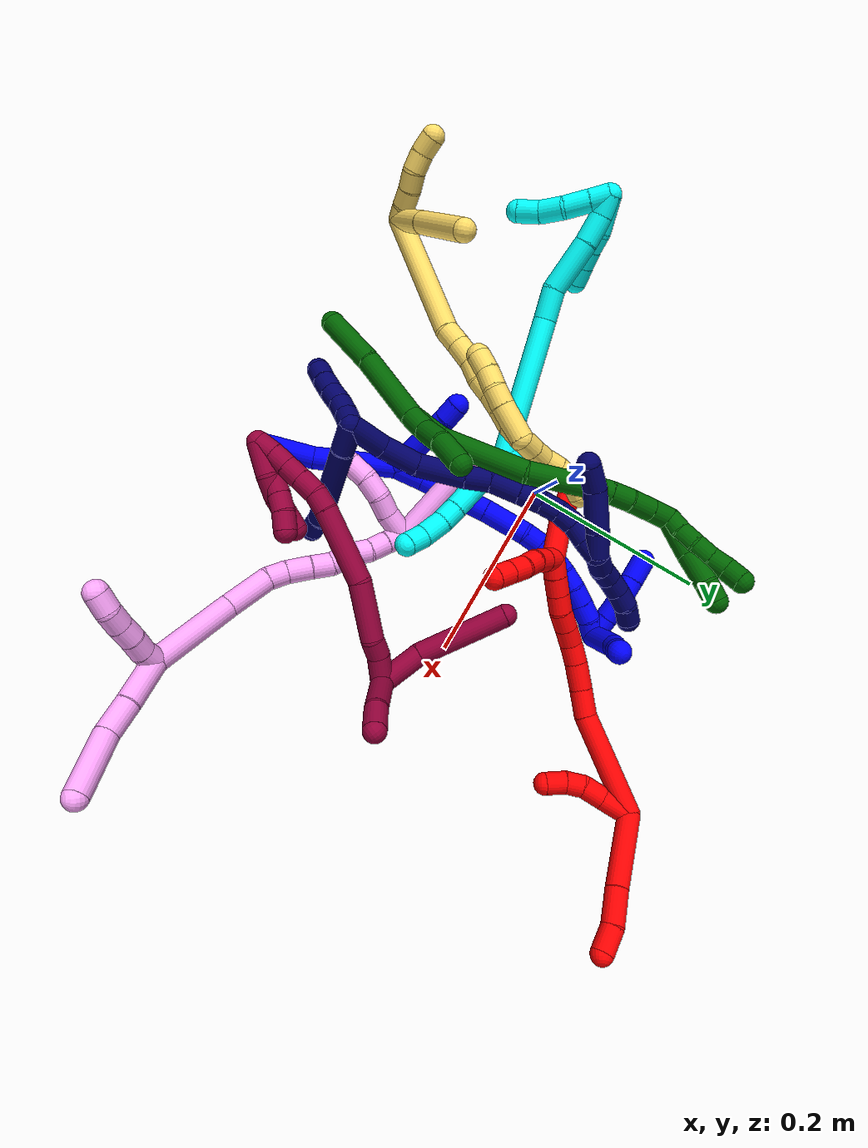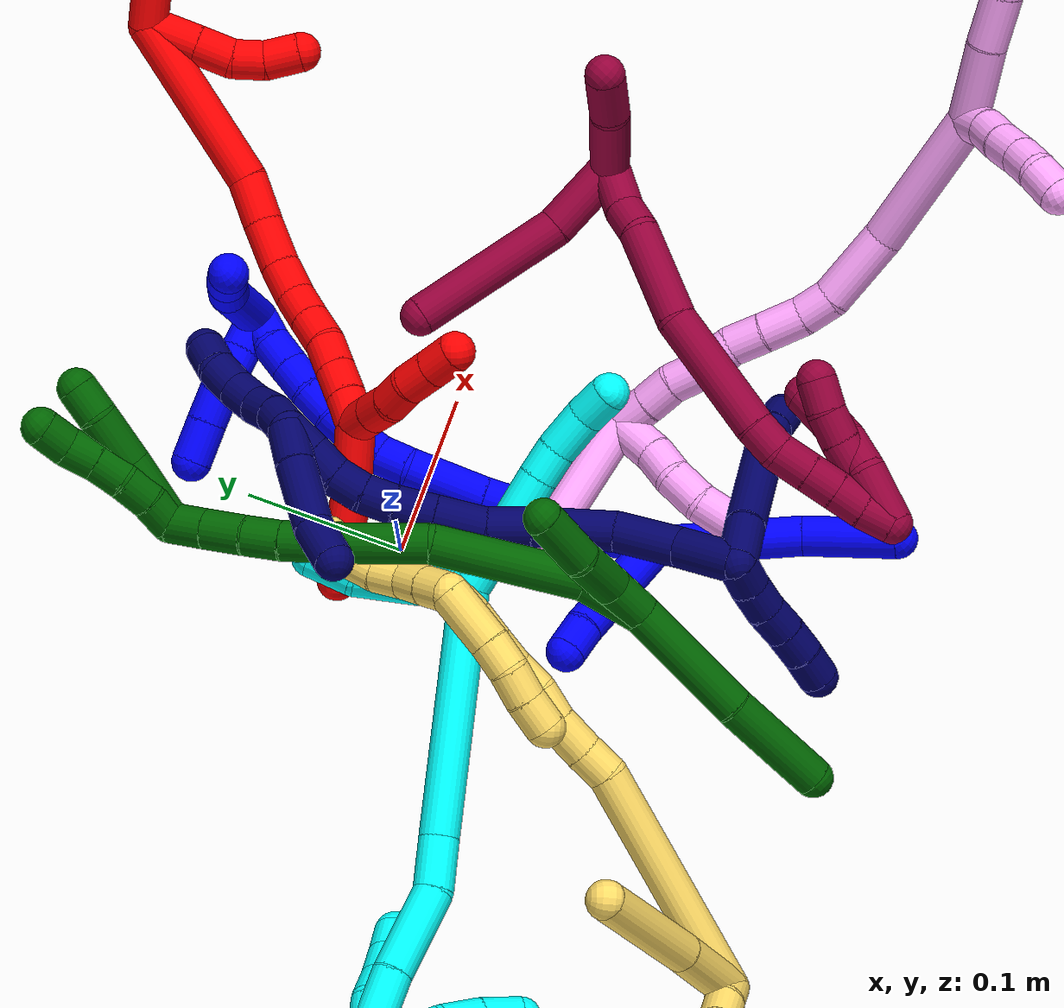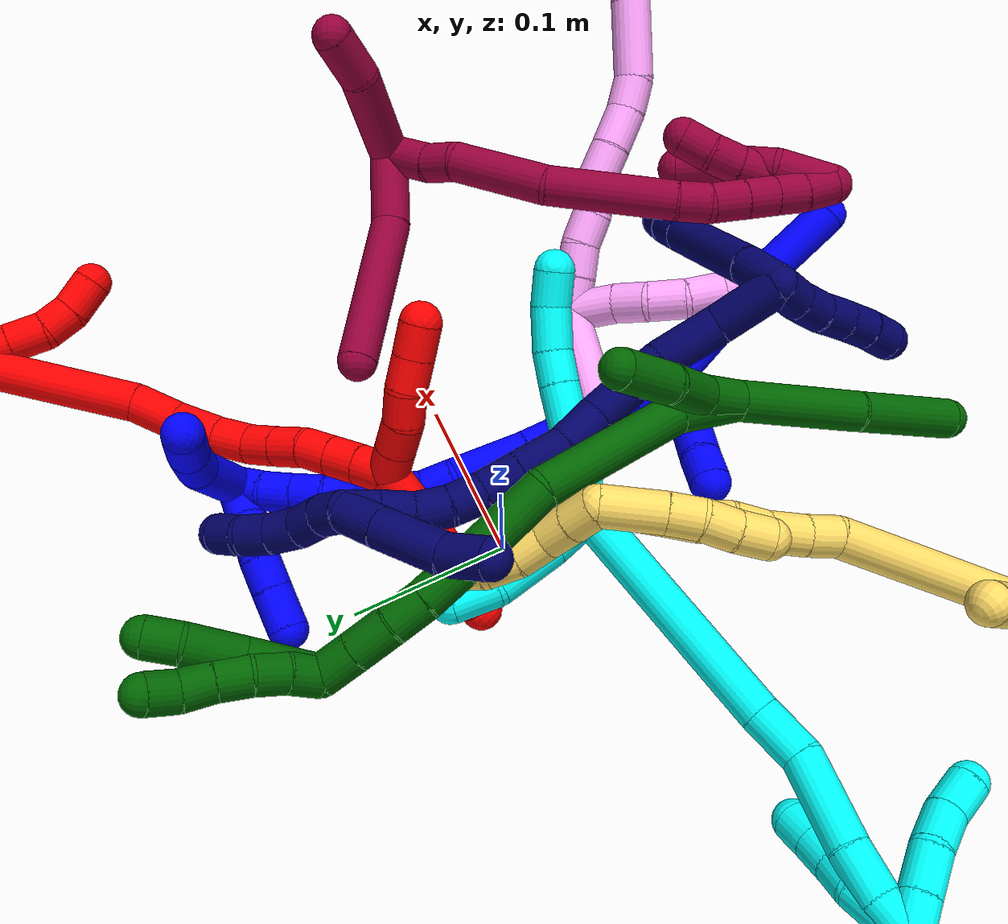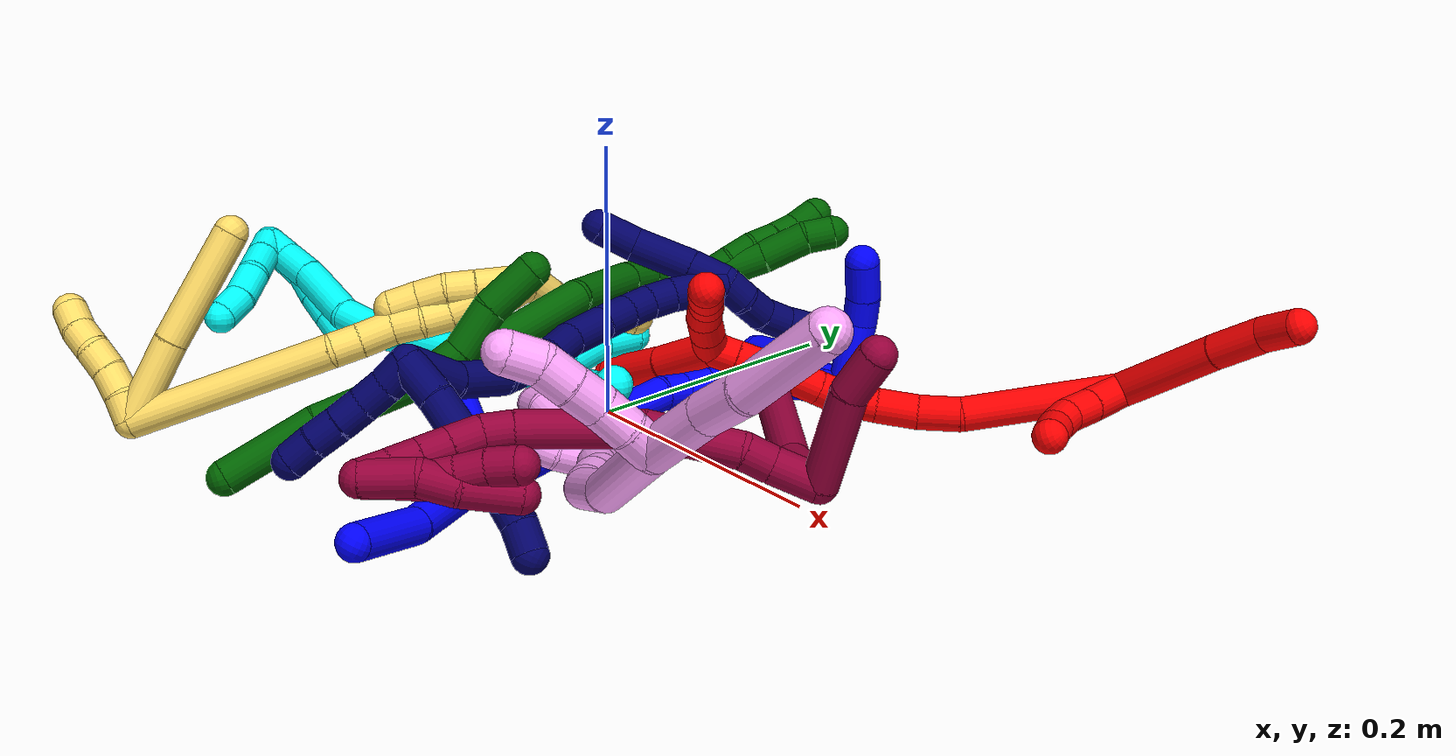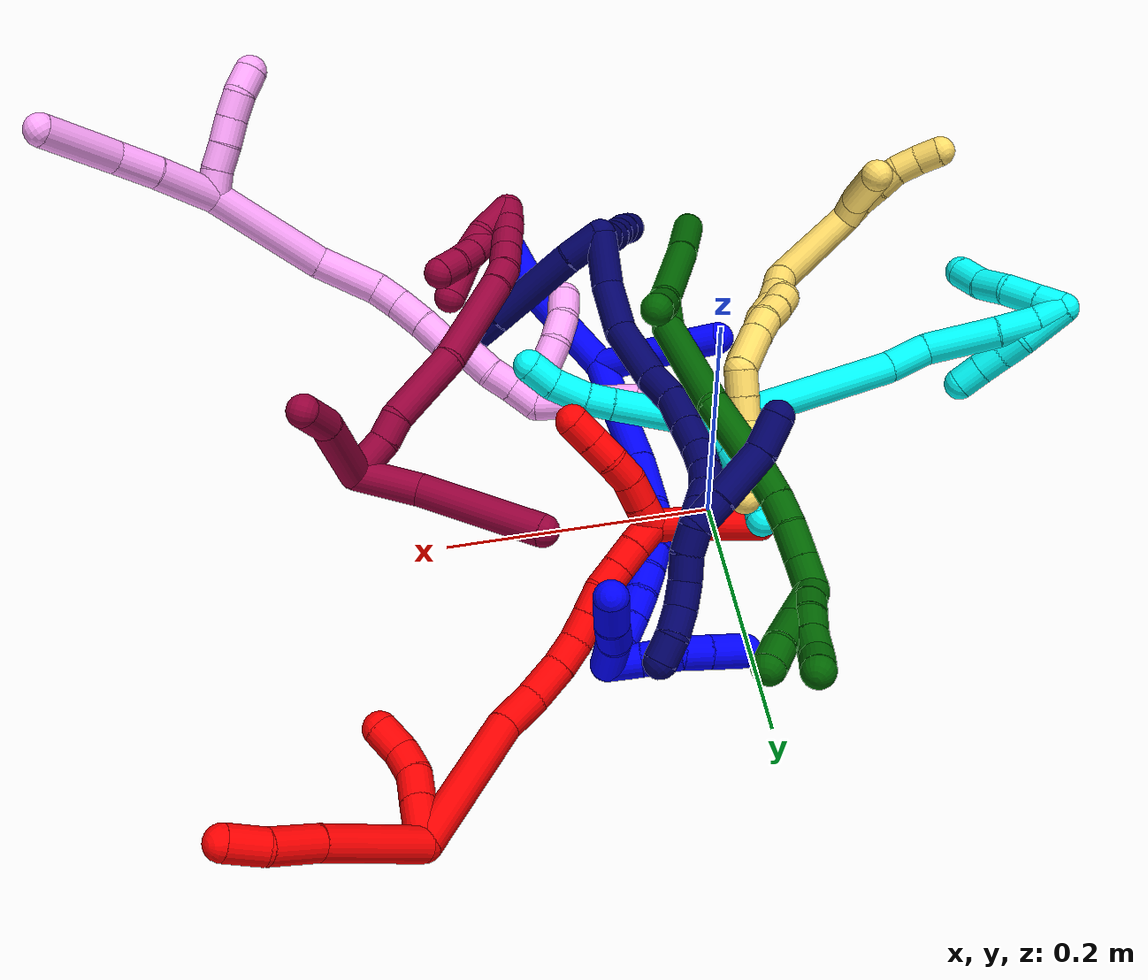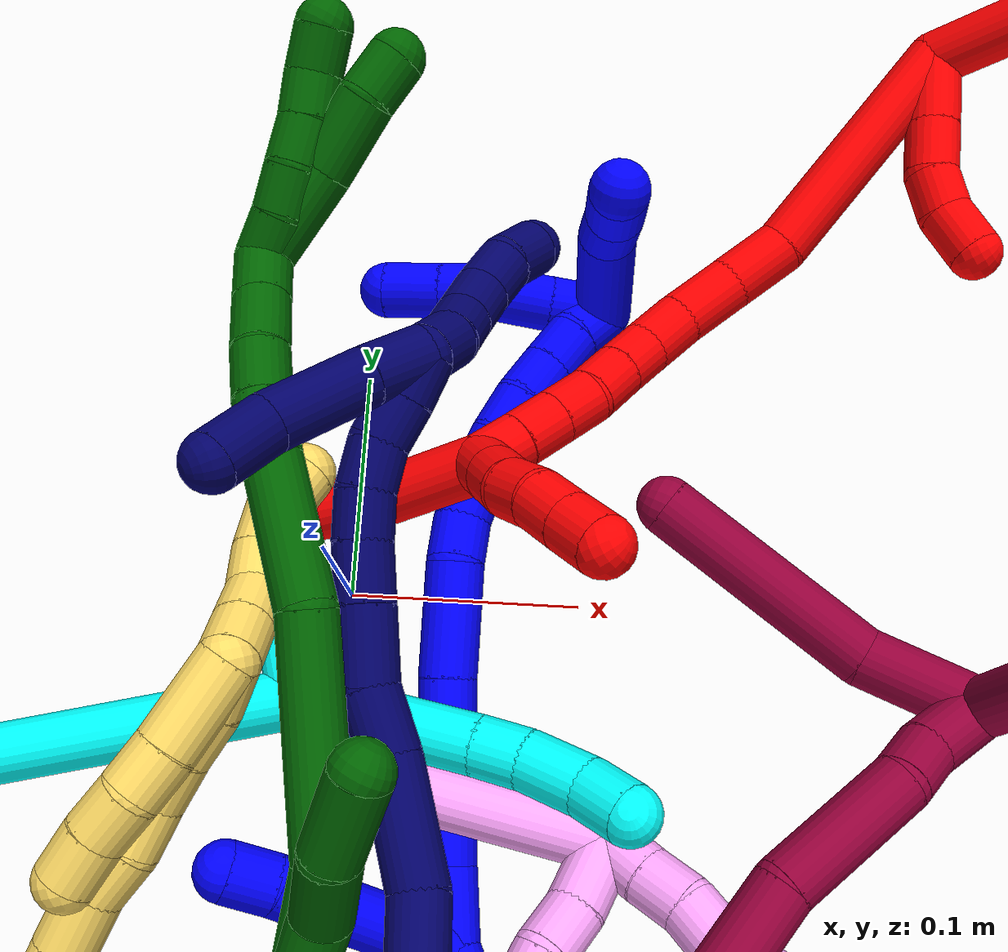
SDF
<sdf version="1.7">
 <world name="default">
  <plugin name="TubeGeneratorPlugin" filename="libtube_generator_plugin.so"/>
  <model name="photoneo_s_sensor">
   <static>1</static>
   <pose>0 0 2 1.57079 1.57079 3.14159</pose>
   <link name="link">
    <inertial><mass>0.1</mass></inertial>
    <sensor name="sensor" type="depth">
     <update_rate>30</update_rate>
     <camera>
      <horizontal_fov>1.22</horizontal_fov>
      <image><width>1920</width><height>1200</height><format>B8G8R8</format></image>
      <clip><near>0.1</near><far>4</far></clip>
      <depth_camera><output>points</output></depth_camera>
     </camera>
     <plugin name="camera_plugin" filename="libgazebo_ros_depth_camera.so">
      <baseline>0.2</baseline>
      <alwaysOn>1</alwaysOn>
      <updateRate>0.0</updateRate>
      <cameraName>camera_ir</cameraName>
      <imageTopicName>/camera/color/image_raw</imageTopicName>
      <cameraInfoTopicName>/camera/color/camera_info</cameraInfoTopicName>
      <depthImageTopicName>/camera/depth/image_raw</depthImageTopicName>
      <depthImageCameraInfoTopicName>/camera/depth/camera_info</depthImageCameraInfoTopicName>
      <pointCloudTopicName>/camera/depth/points</pointCloudTopicName>
      <frameName>fr_optical</frameName>
      <pointCloudCutoff>0.1</pointCloudCutoff>
      <pointCloudCutoffMax>2.0</pointCloudCutoffMax>
      <distortionK1>0</distortionK1>
      <distortionK2>0</distortionK2>
      <distortionK3>0</distortionK3>
      <distortionT1>0</distortionT1>
      <distortionT2>0</distortionT2>
      <CxPrime>0</CxPrime>
      <Cx>0</Cx>
      <Cy>0</Cy>
      <focalLength>0</focalLength>
      <hackBaseline>0</hackBaseline>
     </plugin>
    </sensor>
   </link>
  </model>
  <gravity>0 0 -9.8</gravity>
  <magnetic_field>6e-06 2.3e-05 -4.2e-05</magnetic_field>
  <atmosphere type="adiabatic"/>
  <physics name="default_physics" default="0" type="ode">
   <max_step_size>0.003</max_step_size>
   <real_time_factor>1</real_time_factor>
   <real_time_update_rate>1000</real_time_update_rate>
   <max_contacts>10000</max_contacts>
   <ode>
    <solver>
     <type>quick</type>
     <iters>100</iters>
     <sor>1.3</sor>
     <use_dynamic_moi_rescaling>0</use_dynamic_moi_rescaling>
    </solver>
    <constraints>
     <contact_max_correcting_vel>0</contact_max_correcting_vel>
     <contact_surface_layer>0.001</contact_surface_layer>
     <cfm>0</cfm>
     <erp>0.2</erp>
    </constraints>
   </ode>
  </physics>
  <scene><ambient>0.4 0.4 0.4 1</ambient><background>0.7 0.7 0.7 1</background><shadows>0</shadows></scene>
  <audio><device>default</device></audio>
  <spherical_coordinates>
   <surface_model>EARTH_WGS84</surface_model>
   <latitude_deg>0</latitude_deg>
   <longitude_deg>0</longitude_deg>
   <elevation>0</elevation>
   <heading_deg>0</heading_deg>
  </spherical_coordinates>
  <model name="bin">
   <static>1</static>
   <link name="bottom">
    <collision name="collision-bottom">
     <pose>0 0 -0.01 0 -0 0</pose>
     <geometry><box><size>0.8 0.6 0.02</size></box></geometry>
     <surface>
      <friction><ode><mu>100</mu><mu2>100</mu2></ode></friction>
      <contact><collide_bitmask>65535</collide_bitmask></contact>
     </surface>
    </collision>
   </link>
   <link name="west_wall">
    <collision name="collision-west_wall">
     <pose>-0.41 0 0.1 0 -0 0</pose>
     <geometry><box><size>0.02 0.6 0.2</size></box></geometry>
     <surface>
      <friction><ode><mu>100</mu><mu2>100</mu2></ode></friction>
      <contact><collide_bitmask>65535</collide_bitmask></contact>
     </surface>
    </collision>
   </link>
   <link name="east_wall">
    <collision name="collision-east_wall">
     <pose>0.41 0 0.1 0 -0 0</pose>
     <geometry><box><size>0.02 0.6 0.2</size></box></geometry>
     <surface>
      <friction><ode><mu>100</mu><mu2>100</mu2></ode></friction>
      <contact><collide_bitmask>65535</collide_bitmask></contact>
     </surface>
    </collision>
   </link>
   <link name="south_wall">
    <collision name="collision-south_wall">
     <pose>0 -0.31 0.1 0 -0 0</pose>
     <geometry><box><size>0.8 0.02 0.2</size></box></geometry>
     <surface>
      <friction><ode><mu>100</mu><mu2>100</mu2></ode></friction>
      <contact><collide_bitmask>65535</collide_bitmask></contact>
     </surface>
    </collision>
   </link>
   <link name="north_wall">
    <collision name="collision-north_wall">
     <pose>0 0.31 0.1 0 -0 0</pose>
     <geometry><box><size>0.8 0.02 0.2</size></box></geometry>
     <surface>
      <friction><ode><mu>100</mu><mu2>100</mu2></ode></friction>
      <contact><collide_bitmask>65535</collide_bitmask></contact>
     </surface>
    </collision>
   </link>
  </model>
  <model name="1">
   <static>0</static>
   <link name="1">
    <collision name="collision-cylinder-e_1_2_8">
     <pose>0.02124 -0.035903 -0.018217 2.04034 0.485449 0.766676</pose>
     <geometry><cylinder><radius>0.0125</radius><length>0.091039</length></cylinder></geometry>
     <surface>
      <friction><ode><mu>1.16</mu><mu2>1.16</mu2><slip1>0</slip1><slip2>0</slip2></ode></friction>
      <contact><ode><kp>1e+06</kp><kd>1</kd><max_vel>0</max_vel><min_depth>0.001</min_depth></ode></contact>
     </surface>
    </collision>
    <visual name="visual-cylinder-e_1_2_8">
     <pose>0.02124 -0.035903 -0.018217 2.04034 0.485449 0.766676</pose>
     <geometry><cylinder><radius>0.0125</radius><length>0.091039</length></cylinder></geometry>
     <material><ambient>0 0 1 1</ambient></material>
    </visual>
    <collision name="collision-cylinder-e_2_8_6">
     <pose>0.052009 -0.098543 -0.044397 1.86028 0.329181 0.438393</pose>
     <geometry><cylinder><radius>0.0125</radius><length>0.058961</length></cylinder></geometry>
     <surface>
      <friction><ode><mu>1.16</mu><mu2>1.16</mu2><slip1>0</slip1><slip2>0</slip2></ode></friction>
      <contact><ode><kp>1e+06</kp><kd>1</kd><max_vel>0</max_vel><min_depth>0.001</min_depth></ode></contact>
     </surface>
    </collision>
    <visual name="visual-cylinder-e_2_8_6">
     <pose>0.052009 -0.098543 -0.044397 1.86028 0.329181 0.438393</pose>
     <geometry><cylinder><radius>0.0125</radius><length>0.058961</length></cylinder></geometry>
     <material><ambient>0 0 1 1</ambient></material>
    </visual>
    <collision name="collision-cylinder-e_1_2_9">
     <pose>-0.036033 -0.000661 0.017338 0.038083 -1.12204 -0.023932</pose>
     <geometry><cylinder><radius>0.0125</radius><length>0.079986</length></cylinder></geometry>
     <surface>
      <friction><ode><mu>1.16</mu><mu2>1.16</mu2><slip1>0</slip1><slip2>0</slip2></ode></friction>
      <contact><ode><kp>1e+06</kp><kd>1</kd><max_vel>0</max_vel><min_depth>0.001</min_depth></ode></contact>
     </surface>
    </collision>
    <visual name="visual-cylinder-e_1_2_9">
     <pose>-0.036033 -0.000661 0.017338 0.038083 -1.12204 -0.023932</pose>
     <geometry><cylinder><radius>0.0125</radius><length>0.079986</length></cylinder></geometry>
     <material><ambient>0 0 1 1</ambient></material>
    </visual>
    <collision name="collision-cylinder-e_2_9_5">
     <pose>-0.081603 -0.001489 0.037702 0.055345 -1.2631 -0.040489</pose>
     <geometry><cylinder><radius>0.0125</radius><length>0.020014</length></cylinder></geometry>
     <surface>
      <friction><ode><mu>1.16</mu><mu2>1.16</mu2><slip1>0</slip1><slip2>0</slip2></ode></friction>
      <contact><ode><kp>1e+06</kp><kd>1</kd><max_vel>0</max_vel><min_depth>0.001</min_depth></ode></contact>
     </surface>
    </collision>
    <visual name="visual-cylinder-e_2_9_5">
     <pose>-0.081603 -0.001489 0.037702 0.055345 -1.2631 -0.040489</pose>
     <geometry><cylinder><radius>0.0125</radius><length>0.020014</length></cylinder></geometry>
     <material><ambient>0 0 1 1</ambient></material>
    </visual>
    <collision name="collision-cylinder-e_1_2_10">
     <pose>-0.002741 0.015048 0.006074 -1.18714 -0.167348 0.113059</pose>
     <geometry><cylinder><radius>0.0125</radius><length>0.032914</length></cylinder></geometry>
     <surface>
      <friction><ode><mu>1.16</mu><mu2>1.16</mu2><slip1>0</slip1><slip2>0</slip2></ode></friction>
      <contact><ode><kp>1e+06</kp><kd>1</kd><max_vel>0</max_vel><min_depth>0.001</min_depth></ode></contact>
     </surface>
    </collision>
    <visual name="visual-cylinder-e_1_2_10">
     <pose>-0.002741 0.015048 0.006074 -1.18714 -0.167348 0.113059</pose>
     <geometry><cylinder><radius>0.0125</radius><length>0.032914</length></cylinder></geometry>
     <material><ambient>0 0 1 1</ambient></material>
    </visual>
    <collision name="collision-cylinder-e_2_10_11">
     <pose>-0.010926 0.060593 0.035688 -0.91346 -0.140363 0.069058</pose>
     <geometry><cylinder><radius>0.0125</radius><length>0.077817</length></cylinder></geometry>
     <surface>
      <friction><ode><mu>1.16</mu><mu2>1.16</mu2><slip1>0</slip1><slip2>0</slip2></ode></friction>
      <contact><ode><kp>1e+06</kp><kd>1</kd><max_vel>0</max_vel><min_depth>0.001</min_depth></ode></contact>
     </surface>
    </collision>
    <visual name="visual-cylinder-e_2_10_11">
     <pose>-0.010926 0.060593 0.035688 -0.91346 -0.140363 0.069058</pose>
     <geometry><cylinder><radius>0.0125</radius><length>0.077817</length></cylinder></geometry>
     <material><ambient>0 0 1 1</ambient></material>
    </visual>
    <collision name="collision-cylinder-e_3_11_12">
     <pose>-0.018209 0.110372 0.074335 -0.906186 -0.074978 0.036518</pose>
     <geometry><cylinder><radius>0.0125</radius><length>0.049128</length></cylinder></geometry>
     <surface>
      <friction><ode><mu>1.16</mu><mu2>1.16</mu2><slip1>0</slip1><slip2>0</slip2></ode></friction>
      <contact><ode><kp>1e+06</kp><kd>1</kd><max_vel>0</max_vel><min_depth>0.001</min_depth></ode></contact>
     </surface>
    </collision>
    <visual name="visual-cylinder-e_3_11_12">
     <pose>-0.018209 0.110372 0.074335 -0.906186 -0.074978 0.036518</pose>
     <geometry><cylinder><radius>0.0125</radius><length>0.049128</length></cylinder></geometry>
     <material><ambient>0 0 1 1</ambient></material>
    </visual>
    <collision name="collision-cylinder-e_4_12_13">
     <pose>-0.019828 0.138852 0.093409 -1.16369 0.022047 -0.014503</pose>
     <geometry><cylinder><radius>0.0125</radius><length>0.020039</length></cylinder></geometry>
     <surface>
      <friction><ode><mu>1.16</mu><mu2>1.16</mu2><slip1>0</slip1><slip2>0</slip2></ode></friction>
      <contact><ode><kp>1e+06</kp><kd>1</kd><max_vel>0</max_vel><min_depth>0.001</min_depth></ode></contact>
     </surface>
    </collision>
    <visual name="visual-cylinder-e_4_12_13">
     <pose>-0.019828 0.138852 0.093409 -1.16369 0.022047 -0.014503</pose>
     <geometry><cylinder><radius>0.0125</radius><length>0.020039</length></cylinder></geometry>
     <material><ambient>0 0 1 1</ambient></material>
    </visual>
    <collision name="collision-cylinder-e_5_13_14">
     <pose>-0.017404 0.156035 0.10304 -0.953702 0.221425 -0.114735</pose>
     <geometry><cylinder><radius>0.0125</radius><length>0.020071</length></cylinder></geometry>
     <surface>
      <friction><ode><mu>1.16</mu><mu2>1.16</mu2><slip1>0</slip1><slip2>0</slip2></ode></friction>
      <contact><ode><kp>1e+06</kp><kd>1</kd><max_vel>0</max_vel><min_depth>0.001</min_depth></ode></contact>
     </surface>
    </collision>
    <visual name="visual-cylinder-e_5_13_14">
     <pose>-0.017404 0.156035 0.10304 -0.953702 0.221425 -0.114735</pose>
     <geometry><cylinder><radius>0.0125</radius><length>0.020071</length></cylinder></geometry>
     <material><ambient>0 0 1 1</ambient></material>
    </visual>
    <collision name="collision-cylinder-e_6_14_15">
     <pose>-0.01206 0.171629 0.114405 -0.927901 0.318932 -0.160608</pose>
     <geometry><cylinder><radius>0.0125</radius><length>0.020023</length></cylinder></geometry>
     <surface>
      <friction><ode><mu>1.16</mu><mu2>1.16</mu2><slip1>0</slip1><slip2>0</slip2></ode></friction>
      <contact><ode><kp>1e+06</kp><kd>1</kd><max_vel>0</max_vel><min_depth>0.001</min_depth></ode></contact>
     </surface>
    </collision>
    <visual name="visual-cylinder-e_6_14_15">
     <pose>-0.01206 0.171629 0.114405 -0.927901 0.318932 -0.160608</pose>
     <geometry><cylinder><radius>0.0125</radius><length>0.020023</length></cylinder></geometry>
     <material><ambient>0 0 1 1</ambient></material>
    </visual>
    <collision name="collision-cylinder-e_7_15_16">
     <pose>-0.004998 0.187283 0.124567 -1.06435 0.40309 -0.239474</pose>
     <geometry><cylinder><radius>0.0125</radius><length>0.020004</length></cylinder></geometry>
     <surface>
      <friction><ode><mu>1.16</mu><mu2>1.16</mu2><slip1>0</slip1><slip2>0</slip2></ode></friction>
      <contact><ode><kp>1e+06</kp><kd>1</kd><max_vel>0</max_vel><min_depth>0.001</min_depth></ode></contact>
     </surface>
    </collision>
    <visual name="visual-cylinder-e_7_15_16">
     <pose>-0.004998 0.187283 0.124567 -1.06435 0.40309 -0.239474</pose>
     <geometry><cylinder><radius>0.0125</radius><length>0.020004</length></cylinder></geometry>
     <material><ambient>0 0 1 1</ambient></material>
    </visual>
    <collision name="collision-cylinder-e_8_16_17">
     <pose>0.003654 0.203559 0.132178 -1.20542 0.492524 -0.342548</pose>
     <geometry><cylinder><radius>0.0125</radius><length>0.020001</length></cylinder></geometry>
     <surface>
      <friction><ode><mu>1.16</mu><mu2>1.16</mu2><slip1>0</slip1><slip2>0</slip2></ode></friction>
      <contact><ode><kp>1e+06</kp><kd>1</kd><max_vel>0</max_vel><min_depth>0.001</min_depth></ode></contact>
     </surface>
    </collision>
    <visual name="visual-cylinder-e_8_16_17">
     <pose>0.003654 0.203559 0.132178 -1.20542 0.492524 -0.342548</pose>
     <geometry><cylinder><radius>0.0125</radius><length>0.020001</length></cylinder></geometry>
     <material><ambient>0 0 1 1</ambient></material>
    </visual>
    <collision name="collision-cylinder-e_9_17_18">
     <pose>0.013293 0.2198 0.138755 -1.16643 0.513095 -0.342758</pose>
     <geometry><cylinder><radius>0.0125</radius><length>0.020003</length></cylinder></geometry>
     <surface>
      <friction><ode><mu>1.16</mu><mu2>1.16</mu2><slip1>0</slip1><slip2>0</slip2></ode></friction>
      <contact><ode><kp>1e+06</kp><kd>1</kd><max_vel>0</max_vel><min_depth>0.001</min_depth></ode></contact>
     </surface>
    </collision>
    <visual name="visual-cylinder-e_9_17_18">
     <pose>0.013293 0.2198 0.138755 -1.16643 0.513095 -0.342758</pose>
     <geometry><cylinder><radius>0.0125</radius><length>0.020003</length></cylinder></geometry>
     <material><ambient>0 0 1 1</ambient></material>
    </visual>
    <collision name="collision-cylinder-e_10_18_1">
     <pose>0.024276 0.235589 0.143796 -1.36639 0.652816 -0.537732</pose>
     <geometry><cylinder><radius>0.0125</radius><length>0.02</length></cylinder></geometry>
     <surface>
      <friction><ode><mu>1.16</mu><mu2>1.16</mu2><slip1>0</slip1><slip2>0</slip2></ode></friction>
      <contact><ode><kp>1e+06</kp><kd>1</kd><max_vel>0</max_vel><min_depth>0.001</min_depth></ode></contact>
     </surface>
    </collision>
    <visual name="visual-cylinder-e_10_18_1">
     <pose>0.024276 0.235589 0.143796 -1.36639 0.652816 -0.537732</pose>
     <geometry><cylinder><radius>0.0125</radius><length>0.02</length></cylinder></geometry>
     <material><ambient>0 0 1 1</ambient></material>
    </visual>
    <collision name="collision-cylinder-e_1_1_19">
     <pose>0.027379 0.236905 0.170898 0.248306 -0.112521 -0.014057</pose>
     <geometry><cylinder><radius>0.0125</radius><length>0.052926</length></cylinder></geometry>
     <surface>
      <friction><ode><mu>1.16</mu><mu2>1.16</mu2><slip1>0</slip1><slip2>0</slip2></ode></friction>
      <contact><ode><kp>1e+06</kp><kd>1</kd><max_vel>0</max_vel><min_depth>0.001</min_depth></ode></contact>
     </surface>
    </collision>
    <visual name="visual-cylinder-e_1_1_19">
     <pose>0.027379 0.236905 0.170898 0.248306 -0.112521 -0.014057</pose>
     <geometry><cylinder><radius>0.0125</radius><length>0.052926</length></cylinder></geometry>
     <material><ambient>0 0 1 1</ambient></material>
    </visual>
    <collision name="collision-cylinder-e_2_19_20">
     <pose>0.02469 0.225516 0.205274 0.506142 0.027818 0.007195</pose>
     <geometry><cylinder><radius>0.0125</radius><length>0.02033</length></cylinder></geometry>
     <surface>
      <friction><ode><mu>1.16</mu><mu2>1.16</mu2><slip1>0</slip1><slip2>0</slip2></ode></friction>
      <contact><ode><kp>1e+06</kp><kd>1</kd><max_vel>0</max_vel><min_depth>0.001</min_depth></ode></contact>
     </surface>
    </collision>
    <visual name="visual-cylinder-e_2_19_20">
     <pose>0.02469 0.225516 0.205274 0.506142 0.027818 0.007195</pose>
     <geometry><cylinder><radius>0.0125</radius><length>0.02033</length></cylinder></geometry>
     <material><ambient>0 0 1 1</ambient></material>
    </visual>
    <collision name="collision-cylinder-e_3_20_4">
     <pose>0.024276 0.212592 0.224855 0.642157 -0.052152 -0.017349</pose>
     <geometry><cylinder><radius>0.0125</radius><length>0.026743</length></cylinder></geometry>
     <surface>
      <friction><ode><mu>1.16</mu><mu2>1.16</mu2><slip1>0</slip1><slip2>0</slip2></ode></friction>
      <contact><ode><kp>1e+06</kp><kd>1</kd><max_vel>0</max_vel><min_depth>0.001</min_depth></ode></contact>
     </surface>
    </collision>
    <visual name="visual-cylinder-e_3_20_4">
     <pose>0.024276 0.212592 0.224855 0.642157 -0.052152 -0.017349</pose>
     <geometry><cylinder><radius>0.0125</radius><length>0.026743</length></cylinder></geometry>
     <material><ambient>0 0 1 1</ambient></material>
    </visual>
    <collision name="collision-cylinder-e_1_1_21">
     <pose>0.018091 0.243457 0.145808 -0.221828 -1.53741 0.214601</pose>
     <geometry><cylinder><radius>0.0125</radius><length>0.024533</length></cylinder></geometry>
     <surface>
      <friction><ode><mu>1.16</mu><mu2>1.16</mu2><slip1>0</slip1><slip2>0</slip2></ode></friction>
      <contact><ode><kp>1e+06</kp><kd>1</kd><max_vel>0</max_vel><min_depth>0.001</min_depth></ode></contact>
     </surface>
    </collision>
    <visual name="visual-cylinder-e_1_1_21">
     <pose>0.018091 0.243457 0.145808 -0.221828 -1.53741 0.214601</pose>
     <geometry><cylinder><radius>0.0125</radius><length>0.024533</length></cylinder></geometry>
     <material><ambient>0 0 1 1</ambient></material>
    </visual>
    <collision name="collision-cylinder-e_2_21_22">
     <pose>-0.008522 0.243075 0.14739 0.379943 -1.4823 -0.3484</pose>
     <geometry><cylinder><radius>0.0125</radius><length>0.028819</length></cylinder></geometry>
     <surface>
      <friction><ode><mu>1.16</mu><mu2>1.16</mu2><slip1>0</slip1><slip2>0</slip2></ode></friction>
      <contact><ode><kp>1e+06</kp><kd>1</kd><max_vel>0</max_vel><min_depth>0.001</min_depth></ode></contact>
     </surface>
    </collision>
    <visual name="visual-cylinder-e_2_21_22">
     <pose>-0.008522 0.243075 0.14739 0.379943 -1.4823 -0.3484</pose>
     <geometry><cylinder><radius>0.0125</radius><length>0.028819</length></cylinder></geometry>
     <material><ambient>0 0 1 1</ambient></material>
    </visual>
    <collision name="collision-cylinder-e_3_22_23">
     <pose>-0.032904 0.243584 0.14628 -2.73708 -1.32706 2.62856</pose>
     <geometry><cylinder><radius>0.0125</radius><length>0.02067</length></cylinder></geometry>
     <surface>
      <friction><ode><mu>1.16</mu><mu2>1.16</mu2><slip1>0</slip1><slip2>0</slip2></ode></friction>
      <contact><ode><kp>1e+06</kp><kd>1</kd><max_vel>0</max_vel><min_depth>0.001</min_depth></ode></contact>
     </surface>
    </collision>
    <visual name="visual-cylinder-e_3_22_23">
     <pose>-0.032904 0.243584 0.14628 -2.73708 -1.32706 2.62856</pose>
     <geometry><cylinder><radius>0.0125</radius><length>0.02067</length></cylinder></geometry>
     <material><ambient>0 0 1 1</ambient></material>
    </visual>
    <collision name="collision-cylinder-e_4_23_3">
     <pose>-0.055582 0.245499 0.141181 -2.82055 -1.34111 2.73885</pose>
     <geometry><cylinder><radius>0.0125</radius><length>0.025978</length></cylinder></geometry>
     <surface>
      <friction><ode><mu>1.16</mu><mu2>1.16</mu2><slip1>0</slip1><slip2>0</slip2></ode></friction>
      <contact><ode><kp>1e+06</kp><kd>1</kd><max_vel>0</max_vel><min_depth>0.001</min_depth></ode></contact>
     </surface>
    </collision>
    <visual name="visual-cylinder-e_4_23_3">
     <pose>-0.055582 0.245499 0.141181 -2.82055 -1.34111 2.73885</pose>
     <geometry><cylinder><radius>0.0125</radius><length>0.025978</length></cylinder></geometry>
     <material><ambient>0 0 1 1</ambient></material>
    </visual>
    <collision name="collision-sphere-3">
     <pose>-0.06823 0.246432 0.138375 0 -0 0</pose>
     <geometry><sphere><radius>0.0125</radius></sphere></geometry>
     <surface>
      <friction><ode><mu>1.16</mu><mu2>1.16</mu2><slip1>0</slip1><slip2>0</slip2></ode></friction>
      <contact><ode><kp>1e+06</kp><kd>1</kd><max_vel>0</max_vel><min_depth>0.001</min_depth></ode></contact>
     </surface>
    </collision>
    <visual name="visual-sphere-3">
     <pose>-0.06823 0.246432 0.138375 0 -0 0</pose>
     <geometry><sphere><radius>0.0125</radius></sphere></geometry>
     <material><ambient>0 0 1 1</ambient></material>
    </visual>
    <collision name="collision-sphere-23">
     <pose>-0.042934 0.244566 0.143987 0 -0 0</pose>
     <geometry><sphere><radius>0.0125</radius></sphere></geometry>
     <surface>
      <friction><ode><mu>1.16</mu><mu2>1.16</mu2><slip1>0</slip1><slip2>0</slip2></ode></friction>
      <contact><ode><kp>1e+06</kp><kd>1</kd><max_vel>0</max_vel><min_depth>0.001</min_depth></ode></contact>
     </surface>
    </collision>
    <visual name="visual-sphere-23">
     <pose>-0.042934 0.244566 0.143987 0 -0 0</pose>
     <geometry><sphere><radius>0.0125</radius></sphere></geometry>
     <material><ambient>0 0 1 1</ambient></material>
    </visual>
    <collision name="collision-sphere-22">
     <pose>-0.022875 0.242603 0.148573 0 -0 0</pose>
     <geometry><sphere><radius>0.0125</radius></sphere></geometry>
     <surface>
      <friction><ode><mu>1.16</mu><mu2>1.16</mu2><slip1>0</slip1><slip2>0</slip2></ode></friction>
      <contact><ode><kp>1e+06</kp><kd>1</kd><max_vel>0</max_vel><min_depth>0.001</min_depth></ode></contact>
     </surface>
    </collision>
    <visual name="visual-sphere-22">
     <pose>-0.022875 0.242603 0.148573 0 -0 0</pose>
     <geometry><sphere><radius>0.0125</radius></sphere></geometry>
     <material><ambient>0 0 1 1</ambient></material>
    </visual>
    <collision name="collision-sphere-21">
     <pose>0.005831 0.243547 0.146207 0 -0 0</pose>
     <geometry><sphere><radius>0.0125</radius></sphere></geometry>
     <surface>
      <friction><ode><mu>1.16</mu><mu2>1.16</mu2><slip1>0</slip1><slip2>0</slip2></ode></friction>
      <contact><ode><kp>1e+06</kp><kd>1</kd><max_vel>0</max_vel><min_depth>0.001</min_depth></ode></contact>
     </surface>
    </collision>
    <visual name="visual-sphere-21">
     <pose>0.005831 0.243547 0.146207 0 -0 0</pose>
     <geometry><sphere><radius>0.0125</radius></sphere></geometry>
     <material><ambient>0 0 1 1</ambient></material>
    </visual>
    <collision name="collision-sphere-4">
     <pose>0.023579 0.204594 0.235549 0 -0 0</pose>
     <geometry><sphere><radius>0.0125</radius></sphere></geometry>
     <surface>
      <friction><ode><mu>1.16</mu><mu2>1.16</mu2><slip1>0</slip1><slip2>0</slip2></ode></friction>
      <contact><ode><kp>1e+06</kp><kd>1</kd><max_vel>0</max_vel><min_depth>0.001</min_depth></ode></contact>
     </surface>
    </collision>
    <visual name="visual-sphere-4">
     <pose>0.023579 0.204594 0.235549 0 -0 0</pose>
     <geometry><sphere><radius>0.0125</radius></sphere></geometry>
     <material><ambient>0 0 1 1</ambient></material>
    </visual>
    <collision name="collision-sphere-20">
     <pose>0.024973 0.22059 0.214162 0 -0 0</pose>
     <geometry><sphere><radius>0.0125</radius></sphere></geometry>
     <surface>
      <friction><ode><mu>1.16</mu><mu2>1.16</mu2><slip1>0</slip1><slip2>0</slip2></ode></friction>
      <contact><ode><kp>1e+06</kp><kd>1</kd><max_vel>0</max_vel><min_depth>0.001</min_depth></ode></contact>
     </surface>
    </collision>
    <visual name="visual-sphere-20">
     <pose>0.024973 0.22059 0.214162 0 -0 0</pose>
     <geometry><sphere><radius>0.0125</radius></sphere></geometry>
     <material><ambient>0 0 1 1</ambient></material>
    </visual>
    <collision name="collision-sphere-10">
     <pose>-0.005482 0.030095 0.012148 0 -0 0</pose>
     <geometry><sphere><radius>0.0125</radius></sphere></geometry>
     <surface>
      <friction><ode><mu>1.16</mu><mu2>1.16</mu2><slip1>0</slip1><slip2>0</slip2></ode></friction>
      <contact><ode><kp>1e+06</kp><kd>1</kd><max_vel>0</max_vel><min_depth>0.001</min_depth></ode></contact>
     </surface>
    </collision>
    <visual name="visual-sphere-10">
     <pose>-0.005482 0.030095 0.012148 0 -0 0</pose>
     <geometry><sphere><radius>0.0125</radius></sphere></geometry>
     <material><ambient>0 0 1 1</ambient></material>
    </visual>
    <collision name="collision-sphere-5">
     <pose>-0.09114 -0.001657 0.040729 0 -0 0</pose>
     <geometry><sphere><radius>0.0125</radius></sphere></geometry>
     <surface>
      <friction><ode><mu>1.16</mu><mu2>1.16</mu2><slip1>0</slip1><slip2>0</slip2></ode></friction>
      <contact><ode><kp>1e+06</kp><kd>1</kd><max_vel>0</max_vel><min_depth>0.001</min_depth></ode></contact>
     </surface>
    </collision>
    <visual name="visual-sphere-5">
     <pose>-0.09114 -0.001657 0.040729 0 -0 0</pose>
     <geometry><sphere><radius>0.0125</radius></sphere></geometry>
     <material><ambient>0 0 1 1</ambient></material>
    </visual>
    <collision name="collision-sphere-6">
     <pose>0.061539 -0.12528 -0.052361 0 -0 0</pose>
     <geometry><sphere><radius>0.0125</radius></sphere></geometry>
     <surface>
      <friction><ode><mu>1.16</mu><mu2>1.16</mu2><slip1>0</slip1><slip2>0</slip2></ode></friction>
      <contact><ode><kp>1e+06</kp><kd>1</kd><max_vel>0</max_vel><min_depth>0.001</min_depth></ode></contact>
     </surface>
    </collision>
    <visual name="visual-sphere-6">
     <pose>0.061539 -0.12528 -0.052361 0 -0 0</pose>
     <geometry><sphere><radius>0.0125</radius></sphere></geometry>
     <material><ambient>0 0 1 1</ambient></material>
    </visual>
    <collision name="collision-sphere-9">
     <pose>-0.072066 -0.001321 0.034676 0 -0 0</pose>
     <geometry><sphere><radius>0.0125</radius></sphere></geometry>
     <surface>
      <friction><ode><mu>1.16</mu><mu2>1.16</mu2><slip1>0</slip1><slip2>0</slip2></ode></friction>
      <contact><ode><kp>1e+06</kp><kd>1</kd><max_vel>0</max_vel><min_depth>0.001</min_depth></ode></contact>
     </surface>
    </collision>
    <visual name="visual-sphere-9">
     <pose>-0.072066 -0.001321 0.034676 0 -0 0</pose>
     <geometry><sphere><radius>0.0125</radius></sphere></geometry>
     <material><ambient>0 0 1 1</ambient></material>
    </visual>
    <collision name="collision-sphere-2">
     <geometry><sphere><radius>0.0125</radius></sphere></geometry>
     <surface>
      <friction><ode><mu>1.16</mu><mu2>1.16</mu2><slip1>0</slip1><slip2>0</slip2></ode></friction>
      <contact><ode><kp>1e+06</kp><kd>1</kd><max_vel>0</max_vel><min_depth>0.001</min_depth></ode></contact>
     </surface>
    </collision>
    <visual name="visual-sphere-2">
     <geometry><sphere><radius>0.0125</radius></sphere></geometry>
     <material><ambient>0 0 1 1</ambient></material>
    </visual>
    <collision name="collision-sphere-19">
     <pose>0.024408 0.230442 0.196387 0 -0 0</pose>
     <geometry><sphere><radius>0.0125</radius></sphere></geometry>
     <surface>
      <friction><ode><mu>1.16</mu><mu2>1.16</mu2><slip1>0</slip1><slip2>0</slip2></ode></friction>
      <contact><ode><kp>1e+06</kp><kd>1</kd><max_vel>0</max_vel><min_depth>0.001</min_depth></ode></contact>
     </surface>
    </collision>
    <visual name="visual-sphere-19">
     <pose>0.024408 0.230442 0.196387 0 -0 0</pose>
     <geometry><sphere><radius>0.0125</radius></sphere></geometry>
     <material><ambient>0 0 1 1</ambient></material>
    </visual>
    <collision name="collision-sphere-8">
     <pose>0.042479 -0.071806 -0.036434 0 -0 0</pose>
     <geometry><sphere><radius>0.0125</radius></sphere></geometry>
     <surface>
      <friction><ode><mu>1.16</mu><mu2>1.16</mu2><slip1>0</slip1><slip2>0</slip2></ode></friction>
      <contact><ode><kp>1e+06</kp><kd>1</kd><max_vel>0</max_vel><min_depth>0.001</min_depth></ode></contact>
     </surface>
    </collision>
    <visual name="visual-sphere-8">
     <pose>0.042479 -0.071806 -0.036434 0 -0 0</pose>
     <geometry><sphere><radius>0.0125</radius></sphere></geometry>
     <material><ambient>0 0 1 1</ambient></material>
    </visual>
    <collision name="collision-sphere-11">
     <pose>-0.016369 0.091091 0.059227 0 -0 0</pose>
     <geometry><sphere><radius>0.0125</radius></sphere></geometry>
     <surface>
      <friction><ode><mu>1.16</mu><mu2>1.16</mu2><slip1>0</slip1><slip2>0</slip2></ode></friction>
      <contact><ode><kp>1e+06</kp><kd>1</kd><max_vel>0</max_vel><min_depth>0.001</min_depth></ode></contact>
     </surface>
    </collision>
    <visual name="visual-sphere-11">
     <pose>-0.016369 0.091091 0.059227 0 -0 0</pose>
     <geometry><sphere><radius>0.0125</radius></sphere></geometry>
     <material><ambient>0 0 1 1</ambient></material>
    </visual>
    <collision name="collision-sphere-12">
     <pose>-0.020049 0.129654 0.089442 0 -0 0</pose>
     <geometry><sphere><radius>0.0125</radius></sphere></geometry>
     <surface>
      <friction><ode><mu>1.16</mu><mu2>1.16</mu2><slip1>0</slip1><slip2>0</slip2></ode></friction>
      <contact><ode><kp>1e+06</kp><kd>1</kd><max_vel>0</max_vel><min_depth>0.001</min_depth></ode></contact>
     </surface>
    </collision>
    <visual name="visual-sphere-12">
     <pose>-0.020049 0.129654 0.089442 0 -0 0</pose>
     <geometry><sphere><radius>0.0125</radius></sphere></geometry>
     <material><ambient>0 0 1 1</ambient></material>
    </visual>
    <collision name="collision-sphere-13">
     <pose>-0.019608 0.14805 0.097375 0 -0 0</pose>
     <geometry><sphere><radius>0.0125</radius></sphere></geometry>
     <surface>
      <friction><ode><mu>1.16</mu><mu2>1.16</mu2><slip1>0</slip1><slip2>0</slip2></ode></friction>
      <contact><ode><kp>1e+06</kp><kd>1</kd><max_vel>0</max_vel><min_depth>0.001</min_depth></ode></contact>
     </surface>
    </collision>
    <visual name="visual-sphere-13">
     <pose>-0.019608 0.14805 0.097375 0 -0 0</pose>
     <geometry><sphere><radius>0.0125</radius></sphere></geometry>
     <material><ambient>0 0 1 1</ambient></material>
    </visual>
    <collision name="collision-sphere-14">
     <pose>-0.015199 0.16402 0.108706 0 -0 0</pose>
     <geometry><sphere><radius>0.0125</radius></sphere></geometry>
     <surface>
      <friction><ode><mu>1.16</mu><mu2>1.16</mu2><slip1>0</slip1><slip2>0</slip2></ode></friction>
      <contact><ode><kp>1e+06</kp><kd>1</kd><max_vel>0</max_vel><min_depth>0.001</min_depth></ode></contact>
     </surface>
    </collision>
    <visual name="visual-sphere-14">
     <pose>-0.015199 0.16402 0.108706 0 -0 0</pose>
     <geometry><sphere><radius>0.0125</radius></sphere></geometry>
     <material><ambient>0 0 1 1</ambient></material>
    </visual>
    <collision name="collision-sphere-15">
     <pose>-0.008921 0.179237 0.120104 0 -0 0</pose>
     <geometry><sphere><radius>0.0125</radius></sphere></geometry>
     <surface>
      <friction><ode><mu>1.16</mu><mu2>1.16</mu2><slip1>0</slip1><slip2>0</slip2></ode></friction>
      <contact><ode><kp>1e+06</kp><kd>1</kd><max_vel>0</max_vel><min_depth>0.001</min_depth></ode></contact>
     </surface>
    </collision>
    <visual name="visual-sphere-15">
     <pose>-0.008921 0.179237 0.120104 0 -0 0</pose>
     <geometry><sphere><radius>0.0125</radius></sphere></geometry>
     <material><ambient>0 0 1 1</ambient></material>
    </visual>
    <collision name="collision-sphere-16">
     <pose>-0.001074 0.195328 0.12903 0 -0 0</pose>
     <geometry><sphere><radius>0.0125</radius></sphere></geometry>
     <surface>
      <friction><ode><mu>1.16</mu><mu2>1.16</mu2><slip1>0</slip1><slip2>0</slip2></ode></friction>
      <contact><ode><kp>1e+06</kp><kd>1</kd><max_vel>0</max_vel><min_depth>0.001</min_depth></ode></contact>
     </surface>
    </collision>
    <visual name="visual-sphere-16">
     <pose>-0.001074 0.195328 0.12903 0 -0 0</pose>
     <geometry><sphere><radius>0.0125</radius></sphere></geometry>
     <material><ambient>0 0 1 1</ambient></material>
    </visual>
    <collision name="collision-sphere-17">
     <pose>0.008383 0.211789 0.135327 0 -0 0</pose>
     <geometry><sphere><radius>0.0125</radius></sphere></geometry>
     <surface>
      <friction><ode><mu>1.16</mu><mu2>1.16</mu2><slip1>0</slip1><slip2>0</slip2></ode></friction>
      <contact><ode><kp>1e+06</kp><kd>1</kd><max_vel>0</max_vel><min_depth>0.001</min_depth></ode></contact>
     </surface>
    </collision>
    <visual name="visual-sphere-17">
     <pose>0.008383 0.211789 0.135327 0 -0 0</pose>
     <geometry><sphere><radius>0.0125</radius></sphere></geometry>
     <material><ambient>0 0 1 1</ambient></material>
    </visual>
    <collision name="collision-sphere-18">
     <pose>0.018202 0.22781 0.142183 0 -0 0</pose>
     <geometry><sphere><radius>0.0125</radius></sphere></geometry>
     <surface>
      <friction><ode><mu>1.16</mu><mu2>1.16</mu2><slip1>0</slip1><slip2>0</slip2></ode></friction>
      <contact><ode><kp>1e+06</kp><kd>1</kd><max_vel>0</max_vel><min_depth>0.001</min_depth></ode></contact>
     </surface>
    </collision>
    <visual name="visual-sphere-18">
     <pose>0.018202 0.22781 0.142183 0 -0 0</pose>
     <geometry><sphere><radius>0.0125</radius></sphere></geometry>
     <material><ambient>0 0 1 1</ambient></material>
    </visual>
    <collision name="collision-sphere-1">
     <pose>0.03035 0.243367 0.145408 0 -0 0</pose>
     <geometry><sphere><radius>0.0125</radius></sphere></geometry>
     <surface>
      <friction><ode><mu>1.16</mu><mu2>1.16</mu2><slip1>0</slip1><slip2>0</slip2></ode></friction>
      <contact><ode><kp>1e+06</kp><kd>1</kd><max_vel>0</max_vel><min_depth>0.001</min_depth></ode></contact>
     </surface>
    </collision>
    <visual name="visual-sphere-1">
     <pose>0.03035 0.243367 0.145408 0 -0 0</pose>
     <geometry><sphere><radius>0.0125</radius></sphere></geometry>
     <material><ambient>0 0 1 1</ambient></material>
    </visual>
    <inertial>
     <pose>-0.001253 0.09993 0.073679 0 -0 0</pose>
     <mass>0.75</mass>
     <inertia>
      <ixx>0.000205</ixx>
      <ixy>0</ixy>
      <ixz>0</ixz>
      <iyy>0.000165</iyy>
      <iyz>0</iyz>
      <izz>5.9e-05</izz>
     </inertia>
    </inertial>
   </link>
   <pose>0.054048 -0.146894 0.016261 -0.544409 0.071817 -0.071397</pose>
  </model>
  <model name="2">
   <static>0</static>
   <link name="2">
    <collision name="collision-cylinder-e_1_2_8">
     <pose>-0.001439 -0.006623 0.040849 0.160727 -0.034748 -0.002799</pose>
     <geometry><cylinder><radius>0.0125</radius><length>0.082815</length></cylinder></geometry>
     <surface>
      <friction><ode><mu>1.16</mu><mu2>1.16</mu2><slip1>0</slip1><slip2>0</slip2></ode></friction>
      <contact><ode><kp>1e+06</kp><kd>1</kd><max_vel>0</max_vel><min_depth>0.001</min_depth></ode></contact>
     </surface>
    </collision>
    <visual name="visual-cylinder-e_1_2_8">
     <pose>-0.001439 -0.006623 0.040849 0.160727 -0.034748 -0.002799</pose>
     <geometry><cylinder><radius>0.0125</radius><length>0.082815</length></cylinder></geometry>
     <material><ambient>1 0 0 1</ambient></material>
    </visual>
    <collision name="collision-cylinder-e_2_8_9">
     <pose>-0.002844 -0.015138 0.100876 0.098349 0.001739 8.6e-05</pose>
     <geometry><cylinder><radius>0.0125</radius><length>0.038541</length></cylinder></geometry>
     <surface>
      <friction><ode><mu>1.16</mu><mu2>1.16</mu2><slip1>0</slip1><slip2>0</slip2></ode></friction>
      <contact><ode><kp>1e+06</kp><kd>1</kd><max_vel>0</max_vel><min_depth>0.001</min_depth></ode></contact>
     </surface>
    </collision>
    <visual name="visual-cylinder-e_2_8_9">
     <pose>-0.002844 -0.015138 0.100876 0.098349 0.001739 8.6e-05</pose>
     <geometry><cylinder><radius>0.0125</radius><length>0.038541</length></cylinder></geometry>
     <material><ambient>1 0 0 1</ambient></material>
    </visual>
    <collision name="collision-cylinder-e_3_9_6">
     <pose>-0.001404 -0.021647 0.133538 0.329897 0.098312 0.016378</pose>
     <geometry><cylinder><radius>0.0125</radius><length>0.028643</length></cylinder></geometry>
     <surface>
      <friction><ode><mu>1.16</mu><mu2>1.16</mu2><slip1>0</slip1><slip2>0</slip2></ode></friction>
      <contact><ode><kp>1e+06</kp><kd>1</kd><max_vel>0</max_vel><min_depth>0.001</min_depth></ode></contact>
     </surface>
    </collision>
    <visual name="visual-cylinder-e_3_9_6">
     <pose>-0.001404 -0.021647 0.133538 0.329897 0.098312 0.016378</pose>
     <geometry><cylinder><radius>0.0125</radius><length>0.028643</length></cylinder></geometry>
     <material><ambient>1 0 0 1</ambient></material>
    </visual>
    <collision name="collision-cylinder-e_1_2_10">
     <pose>0.000982 -0.01541 -0.006113 1.94845 0.059185 0.08712</pose>
     <geometry><cylinder><radius>0.0125</radius><length>0.033216</length></cylinder></geometry>
     <surface>
      <friction><ode><mu>1.16</mu><mu2>1.16</mu2><slip1>0</slip1><slip2>0</slip2></ode></friction>
      <contact><ode><kp>1e+06</kp><kd>1</kd><max_vel>0</max_vel><min_depth>0.001</min_depth></ode></contact>
     </surface>
    </collision>
    <visual name="visual-cylinder-e_1_2_10">
     <pose>0.000982 -0.01541 -0.006113 1.94845 0.059185 0.08712</pose>
     <geometry><cylinder><radius>0.0125</radius><length>0.033216</length></cylinder></geometry>
     <material><ambient>1 0 0 1</ambient></material>
    </visual>
    <collision name="collision-cylinder-e_2_10_11">
     <pose>0.00223 -0.041739 -0.01655 1.94787 0.022621 0.033288</pose>
     <geometry><cylinder><radius>0.0125</radius><length>0.023492</length></cylinder></geometry>
     <surface>
      <friction><ode><mu>1.16</mu><mu2>1.16</mu2><slip1>0</slip1><slip2>0</slip2></ode></friction>
      <contact><ode><kp>1e+06</kp><kd>1</kd><max_vel>0</max_vel><min_depth>0.001</min_depth></ode></contact>
     </surface>
    </collision>
    <visual name="visual-cylinder-e_2_10_11">
     <pose>0.00223 -0.041739 -0.01655 1.94787 0.022621 0.033288</pose>
     <geometry><cylinder><radius>0.0125</radius><length>0.023492</length></cylinder></geometry>
     <material><ambient>1 0 0 1</ambient></material>
    </visual>
    <collision name="collision-cylinder-e_3_11_12">
     <pose>0.004446 -0.062513 -0.0217 1.65439 0.194651 0.211521</pose>
     <geometry><cylinder><radius>0.0125</radius><length>0.020161</length></cylinder></geometry>
     <surface>
      <friction><ode><mu>1.16</mu><mu2>1.16</mu2><slip1>0</slip1><slip2>0</slip2></ode></friction>
      <contact><ode><kp>1e+06</kp><kd>1</kd><max_vel>0</max_vel><min_depth>0.001</min_depth></ode></contact>
     </surface>
    </collision>
    <visual name="visual-cylinder-e_3_11_12">
     <pose>0.004446 -0.062513 -0.0217 1.65439 0.194651 0.211521</pose>
     <geometry><cylinder><radius>0.0125</radius><length>0.020161</length></cylinder></geometry>
     <material><ambient>1 0 0 1</ambient></material>
    </visual>
    <collision name="collision-cylinder-e_4_12_5">
     <pose>0.008374 -0.083497 -0.020075 1.35402 0.171909 0.138289</pose>
     <geometry><cylinder><radius>0.0125</radius><length>0.023132</length></cylinder></geometry>
     <surface>
      <friction><ode><mu>1.16</mu><mu2>1.16</mu2><slip1>0</slip1><slip2>0</slip2></ode></friction>
      <contact><ode><kp>1e+06</kp><kd>1</kd><max_vel>0</max_vel><min_depth>0.001</min_depth></ode></contact>
     </surface>
    </collision>
    <visual name="visual-cylinder-e_4_12_5">
     <pose>0.008374 -0.083497 -0.020075 1.35402 0.171909 0.138289</pose>
     <geometry><cylinder><radius>0.0125</radius><length>0.023132</length></cylinder></geometry>
     <material><ambient>1 0 0 1</ambient></material>
    </visual>
    <collision name="collision-cylinder-e_1_2_13">
     <pose>-0.012089 -0.032502 -0.045276 2.51898 -0.213595 -0.643221</pose>
     <geometry><cylinder><radius>0.0125</radius><length>0.11406</length></cylinder></geometry>
     <surface>
      <friction><ode><mu>1.16</mu><mu2>1.16</mu2><slip1>0</slip1><slip2>0</slip2></ode></friction>
      <contact><ode><kp>1e+06</kp><kd>1</kd><max_vel>0</max_vel><min_depth>0.001</min_depth></ode></contact>
     </surface>
    </collision>
    <visual name="visual-cylinder-e_1_2_13">
     <pose>-0.012089 -0.032502 -0.045276 2.51898 -0.213595 -0.643221</pose>
     <geometry><cylinder><radius>0.0125</radius><length>0.11406</length></cylinder></geometry>
     <material><ambient>1 0 0 1</ambient></material>
    </visual>
    <collision name="collision-cylinder-e_2_13_14">
     <pose>-0.03033 -0.070965 -0.103082 2.69753 -0.417302 -1.50671</pose>
     <geometry><cylinder><radius>0.0125</radius><length>0.030356</length></cylinder></geometry>
     <surface>
      <friction><ode><mu>1.16</mu><mu2>1.16</mu2><slip1>0</slip1><slip2>0</slip2></ode></friction>
      <contact><ode><kp>1e+06</kp><kd>1</kd><max_vel>0</max_vel><min_depth>0.001</min_depth></ode></contact>
     </surface>
    </collision>
    <visual name="visual-cylinder-e_2_13_14">
     <pose>-0.03033 -0.070965 -0.103082 2.69753 -0.417302 -1.50671</pose>
     <geometry><cylinder><radius>0.0125</radius><length>0.030356</length></cylinder></geometry>
     <material><ambient>1 0 0 1</ambient></material>
    </visual>
    <collision name="collision-cylinder-e_3_14_15">
     <pose>-0.044132 -0.083661 -0.126866 2.60232 -0.528099 -1.54883</pose>
     <geometry><cylinder><radius>0.0125</radius><length>0.030367</length></cylinder></geometry>
     <surface>
      <friction><ode><mu>1.16</mu><mu2>1.16</mu2><slip1>0</slip1><slip2>0</slip2></ode></friction>
      <contact><ode><kp>1e+06</kp><kd>1</kd><max_vel>0</max_vel><min_depth>0.001</min_depth></ode></contact>
     </surface>
    </collision>
    <visual name="visual-cylinder-e_3_14_15">
     <pose>-0.044132 -0.083661 -0.126866 2.60232 -0.528099 -1.54883</pose>
     <geometry><cylinder><radius>0.0125</radius><length>0.030367</length></cylinder></geometry>
     <material><ambient>1 0 0 1</ambient></material>
    </visual>
    <collision name="collision-cylinder-e_4_15_16">
     <pose>-0.057839 -0.096333 -0.145782 2.48231 -0.558406 -1.39494</pose>
     <geometry><cylinder><radius>0.0125</radius><length>0.022861</length></cylinder></geometry>
     <surface>
      <friction><ode><mu>1.16</mu><mu2>1.16</mu2><slip1>0</slip1><slip2>0</slip2></ode></friction>
      <contact><ode><kp>1e+06</kp><kd>1</kd><max_vel>0</max_vel><min_depth>0.001</min_depth></ode></contact>
     </surface>
    </collision>
    <visual name="visual-cylinder-e_4_15_16">
     <pose>-0.057839 -0.096333 -0.145782 2.48231 -0.558406 -1.39494</pose>
     <geometry><cylinder><radius>0.0125</radius><length>0.022861</length></cylinder></geometry>
     <material><ambient>1 0 0 1</ambient></material>
    </visual>
    <collision name="collision-cylinder-e_5_16_17">
     <pose>-0.070938 -0.108242 -0.158414 2.26493 -0.736485 -1.37739</pose>
     <geometry><cylinder><radius>0.0125</radius><length>0.020971</length></cylinder></geometry>
     <surface>
      <friction><ode><mu>1.16</mu><mu2>1.16</mu2><slip1>0</slip1><slip2>0</slip2></ode></friction>
      <contact><ode><kp>1e+06</kp><kd>1</kd><max_vel>0</max_vel><min_depth>0.001</min_depth></ode></contact>
     </surface>
    </collision>
    <visual name="visual-cylinder-e_5_16_17">
     <pose>-0.070938 -0.108242 -0.158414 2.26493 -0.736485 -1.37739</pose>
     <geometry><cylinder><radius>0.0125</radius><length>0.020971</length></cylinder></geometry>
     <material><ambient>1 0 0 1</ambient></material>
    </visual>
    <collision name="collision-cylinder-e_6_17_18">
     <pose>-0.08497 -0.12037 -0.168169 2.2315 -0.730668 -1.32703</pose>
     <geometry><cylinder><radius>0.0125</radius><length>0.020944</length></cylinder></geometry>
     <surface>
      <friction><ode><mu>1.16</mu><mu2>1.16</mu2><slip1>0</slip1><slip2>0</slip2></ode></friction>
      <contact><ode><kp>1e+06</kp><kd>1</kd><max_vel>0</max_vel><min_depth>0.001</min_depth></ode></contact>
     </surface>
    </collision>
    <visual name="visual-cylinder-e_6_17_18">
     <pose>-0.08497 -0.12037 -0.168169 2.2315 -0.730668 -1.32703</pose>
     <geometry><cylinder><radius>0.0125</radius><length>0.020944</length></cylinder></geometry>
     <material><ambient>1 0 0 1</ambient></material>
    </visual>
    <collision name="collision-cylinder-e_7_18_19">
     <pose>-0.098361 -0.130984 -0.179275 2.52744 -0.69156 -1.69802</pose>
     <geometry><cylinder><radius>0.0125</radius><length>0.020079</length></cylinder></geometry>
     <surface>
      <friction><ode><mu>1.16</mu><mu2>1.16</mu2><slip1>0</slip1><slip2>0</slip2></ode></friction>
      <contact><ode><kp>1e+06</kp><kd>1</kd><max_vel>0</max_vel><min_depth>0.001</min_depth></ode></contact>
     </surface>
    </collision>
    <visual name="visual-cylinder-e_7_18_19">
     <pose>-0.098361 -0.130984 -0.179275 2.52744 -0.69156 -1.69802</pose>
     <geometry><cylinder><radius>0.0125</radius><length>0.020079</length></cylinder></geometry>
     <material><ambient>1 0 0 1</ambient></material>
    </visual>
    <collision name="collision-cylinder-e_8_19_20">
     <pose>-0.111305 -0.139958 -0.191896 2.51954 -0.700814 -1.69881</pose>
     <geometry><cylinder><radius>0.0125</radius><length>0.020289</length></cylinder></geometry>
     <surface>
      <friction><ode><mu>1.16</mu><mu2>1.16</mu2><slip1>0</slip1><slip2>0</slip2></ode></friction>
      <contact><ode><kp>1e+06</kp><kd>1</kd><max_vel>0</max_vel><min_depth>0.001</min_depth></ode></contact>
     </surface>
    </collision>
    <visual name="visual-cylinder-e_8_19_20">
     <pose>-0.111305 -0.139958 -0.191896 2.51954 -0.700814 -1.69881</pose>
     <geometry><cylinder><radius>0.0125</radius><length>0.020289</length></cylinder></geometry>
     <material><ambient>1 0 0 1</ambient></material>
    </visual>
    <collision name="collision-cylinder-e_9_20_1">
     <pose>-0.124278 -0.148686 -0.204651 2.56363 -0.695544 -1.7678</pose>
     <geometry><cylinder><radius>0.0125</radius><length>0.020073</length></cylinder></geometry>
     <surface>
      <friction><ode><mu>1.16</mu><mu2>1.16</mu2><slip1>0</slip1><slip2>0</slip2></ode></friction>
      <contact><ode><kp>1e+06</kp><kd>1</kd><max_vel>0</max_vel><min_depth>0.001</min_depth></ode></contact>
     </surface>
    </collision>
    <visual name="visual-cylinder-e_9_20_1">
     <pose>-0.124278 -0.148686 -0.204651 2.56363 -0.695544 -1.7678</pose>
     <geometry><cylinder><radius>0.0125</radius><length>0.020073</length></cylinder></geometry>
     <material><ambient>1 0 0 1</ambient></material>
    </visual>
    <collision name="collision-cylinder-e_1_1_21">
     <pose>-0.132909 -0.150919 -0.233922 -3.05521 -0.095718 1.67334</pose>
     <geometry><cylinder><radius>0.0125</radius><length>0.046017</length></cylinder></geometry>
     <surface>
      <friction><ode><mu>1.16</mu><mu2>1.16</mu2><slip1>0</slip1><slip2>0</slip2></ode></friction>
      <contact><ode><kp>1e+06</kp><kd>1</kd><max_vel>0</max_vel><min_depth>0.001</min_depth></ode></contact>
     </surface>
    </collision>
    <visual name="visual-cylinder-e_1_1_21">
     <pose>-0.132909 -0.150919 -0.233922 -3.05521 -0.095718 1.67334</pose>
     <geometry><cylinder><radius>0.0125</radius><length>0.046017</length></cylinder></geometry>
     <material><ambient>1 0 0 1</ambient></material>
    </visual>
    <collision name="collision-cylinder-e_2_21_4">
     <pose>-0.139121 -0.144261 -0.283017 -2.96526 -0.149245 1.40404</pose>
     <geometry><cylinder><radius>0.0125</radius><length>0.053983</length></cylinder></geometry>
     <surface>
      <friction><ode><mu>1.16</mu><mu2>1.16</mu2><slip1>0</slip1><slip2>0</slip2></ode></friction>
      <contact><ode><kp>1e+06</kp><kd>1</kd><max_vel>0</max_vel><min_depth>0.001</min_depth></ode></contact>
     </surface>
    </collision>
    <visual name="visual-cylinder-e_2_21_4">
     <pose>-0.139121 -0.144261 -0.283017 -2.96526 -0.149245 1.40404</pose>
     <geometry><cylinder><radius>0.0125</radius><length>0.053983</length></cylinder></geometry>
     <material><ambient>1 0 0 1</ambient></material>
    </visual>
    <collision name="collision-cylinder-e_1_1_22">
     <pose>-0.135625 -0.159658 -0.205617 0.889129 -0.51388 -0.249034</pose>
     <geometry><cylinder><radius>0.0125</radius><length>0.02</length></cylinder></geometry>
     <surface>
      <friction><ode><mu>1.16</mu><mu2>1.16</mu2><slip1>0</slip1><slip2>0</slip2></ode></friction>
      <contact><ode><kp>1e+06</kp><kd>1</kd><max_vel>0</max_vel><min_depth>0.001</min_depth></ode></contact>
     </surface>
    </collision>
    <visual name="visual-cylinder-e_1_1_22">
     <pose>-0.135625 -0.159658 -0.205617 0.889129 -0.51388 -0.249034</pose>
     <geometry><cylinder><radius>0.0125</radius><length>0.02</length></cylinder></geometry>
     <material><ambient>1 0 0 1</ambient></material>
    </visual>
    <collision name="collision-cylinder-e_2_22_23">
     <pose>-0.145548 -0.173187 -0.194733 0.897608 -0.524482 -0.257109</pose>
     <geometry><cylinder><radius>0.0125</radius><length>0.02</length></cylinder></geometry>
     <surface>
      <friction><ode><mu>1.16</mu><mu2>1.16</mu2><slip1>0</slip1><slip2>0</slip2></ode></friction>
      <contact><ode><kp>1e+06</kp><kd>1</kd><max_vel>0</max_vel><min_depth>0.001</min_depth></ode></contact>
     </surface>
    </collision>
    <visual name="visual-cylinder-e_2_22_23">
     <pose>-0.145548 -0.173187 -0.194733 0.897608 -0.524482 -0.257109</pose>
     <geometry><cylinder><radius>0.0125</radius><length>0.02</length></cylinder></geometry>
     <material><ambient>1 0 0 1</ambient></material>
    </visual>
    <collision name="collision-cylinder-e_3_23_24">
     <pose>-0.153628 -0.186406 -0.18234 0.744852 -0.312254 -0.12283</pose>
     <geometry><cylinder><radius>0.0125</radius><length>0.02</length></cylinder></geometry>
     <surface>
      <friction><ode><mu>1.16</mu><mu2>1.16</mu2><slip1>0</slip1><slip2>0</slip2></ode></friction>
      <contact><ode><kp>1e+06</kp><kd>1</kd><max_vel>0</max_vel><min_depth>0.001</min_depth></ode></contact>
     </surface>
    </collision>
    <visual name="visual-cylinder-e_3_23_24">
     <pose>-0.153628 -0.186406 -0.18234 0.744852 -0.312254 -0.12283</pose>
     <geometry><cylinder><radius>0.0125</radius><length>0.02</length></cylinder></geometry>
     <material><ambient>1 0 0 1</ambient></material>
    </visual>
    <collision name="collision-cylinder-e_4_24_25">
     <pose>-0.158239 -0.200709 -0.169346 0.91849 -0.154509 -0.076521</pose>
     <geometry><cylinder><radius>0.0125</radius><length>0.02</length></cylinder></geometry>
     <surface>
      <friction><ode><mu>1.16</mu><mu2>1.16</mu2><slip1>0</slip1><slip2>0</slip2></ode></friction>
      <contact><ode><kp>1e+06</kp><kd>1</kd><max_vel>0</max_vel><min_depth>0.001</min_depth></ode></contact>
     </surface>
    </collision>
    <visual name="visual-cylinder-e_4_24_25">
     <pose>-0.158239 -0.200709 -0.169346 0.91849 -0.154509 -0.076521</pose>
     <geometry><cylinder><radius>0.0125</radius><length>0.02</length></cylinder></geometry>
     <material><ambient>1 0 0 1</ambient></material>
    </visual>
    <collision name="collision-cylinder-e_5_25_3">
     <pose>-0.161402 -0.216291 -0.157215 0.900057 -0.1631 -0.078926</pose>
     <geometry><cylinder><radius>0.0125</radius><length>0.02</length></cylinder></geometry>
     <surface>
      <friction><ode><mu>1.16</mu><mu2>1.16</mu2><slip1>0</slip1><slip2>0</slip2></ode></friction>
      <contact><ode><kp>1e+06</kp><kd>1</kd><max_vel>0</max_vel><min_depth>0.001</min_depth></ode></contact>
     </surface>
    </collision>
    <visual name="visual-cylinder-e_5_25_3">
     <pose>-0.161402 -0.216291 -0.157215 0.900057 -0.1631 -0.078926</pose>
     <geometry><cylinder><radius>0.0125</radius><length>0.02</length></cylinder></geometry>
     <material><ambient>1 0 0 1</ambient></material>
    </visual>
    <collision name="collision-sphere-3">
     <pose>-0.163026 -0.22402 -0.151082 0 -0 0</pose>
     <geometry><sphere><radius>0.0125</radius></sphere></geometry>
     <surface>
      <friction><ode><mu>1.16</mu><mu2>1.16</mu2><slip1>0</slip1><slip2>0</slip2></ode></friction>
      <contact><ode><kp>1e+06</kp><kd>1</kd><max_vel>0</max_vel><min_depth>0.001</min_depth></ode></contact>
     </surface>
    </collision>
    <visual name="visual-sphere-3">
     <pose>-0.163026 -0.22402 -0.151082 0 -0 0</pose>
     <geometry><sphere><radius>0.0125</radius></sphere></geometry>
     <material><ambient>1 0 0 1</ambient></material>
    </visual>
    <collision name="collision-sphere-25">
     <pose>-0.159778 -0.208561 -0.163348 0 -0 0</pose>
     <geometry><sphere><radius>0.0125</radius></sphere></geometry>
     <surface>
      <friction><ode><mu>1.16</mu><mu2>1.16</mu2><slip1>0</slip1><slip2>0</slip2></ode></friction>
      <contact><ode><kp>1e+06</kp><kd>1</kd><max_vel>0</max_vel><min_depth>0.001</min_depth></ode></contact>
     </surface>
    </collision>
    <visual name="visual-sphere-25">
     <pose>-0.159778 -0.208561 -0.163348 0 -0 0</pose>
     <geometry><sphere><radius>0.0125</radius></sphere></geometry>
     <material><ambient>1 0 0 1</ambient></material>
    </visual>
    <collision name="collision-sphere-24">
     <pose>-0.1567 -0.192856 -0.175344 0 -0 0</pose>
     <geometry><sphere><radius>0.0125</radius></sphere></geometry>
     <surface>
      <friction><ode><mu>1.16</mu><mu2>1.16</mu2><slip1>0</slip1><slip2>0</slip2></ode></friction>
      <contact><ode><kp>1e+06</kp><kd>1</kd><max_vel>0</max_vel><min_depth>0.001</min_depth></ode></contact>
     </surface>
    </collision>
    <visual name="visual-sphere-24">
     <pose>-0.1567 -0.192856 -0.175344 0 -0 0</pose>
     <geometry><sphere><radius>0.0125</radius></sphere></geometry>
     <material><ambient>1 0 0 1</ambient></material>
    </visual>
    <collision name="collision-sphere-23">
     <pose>-0.150556 -0.179955 -0.189337 0 -0 0</pose>
     <geometry><sphere><radius>0.0125</radius></sphere></geometry>
     <surface>
      <friction><ode><mu>1.16</mu><mu2>1.16</mu2><slip1>0</slip1><slip2>0</slip2></ode></friction>
      <contact><ode><kp>1e+06</kp><kd>1</kd><max_vel>0</max_vel><min_depth>0.001</min_depth></ode></contact>
     </surface>
    </collision>
    <visual name="visual-sphere-23">
     <pose>-0.150556 -0.179955 -0.189337 0 -0 0</pose>
     <geometry><sphere><radius>0.0125</radius></sphere></geometry>
     <material><ambient>1 0 0 1</ambient></material>
    </visual>
    <collision name="collision-sphere-22">
     <pose>-0.140541 -0.16642 -0.20013 0 -0 0</pose>
     <geometry><sphere><radius>0.0125</radius></sphere></geometry>
     <surface>
      <friction><ode><mu>1.16</mu><mu2>1.16</mu2><slip1>0</slip1><slip2>0</slip2></ode></friction>
      <contact><ode><kp>1e+06</kp><kd>1</kd><max_vel>0</max_vel><min_depth>0.001</min_depth></ode></contact>
     </surface>
    </collision>
    <visual name="visual-sphere-22">
     <pose>-0.140541 -0.16642 -0.20013 0 -0 0</pose>
     <geometry><sphere><radius>0.0125</radius></sphere></geometry>
     <material><ambient>1 0 0 1</ambient></material>
    </visual>
    <collision name="collision-sphere-4">
     <pose>-0.143134 -0.139579 -0.309295 0 -0 0</pose>
     <geometry><sphere><radius>0.0125</radius></sphere></geometry>
     <surface>
      <friction><ode><mu>1.16</mu><mu2>1.16</mu2><slip1>0</slip1><slip2>0</slip2></ode></friction>
      <contact><ode><kp>1e+06</kp><kd>1</kd><max_vel>0</max_vel><min_depth>0.001</min_depth></ode></contact>
     </surface>
    </collision>
    <visual name="visual-sphere-4">
     <pose>-0.143134 -0.139579 -0.309295 0 -0 0</pose>
     <geometry><sphere><radius>0.0125</radius></sphere></geometry>
     <material><ambient>1 0 0 1</ambient></material>
    </visual>
    <collision name="collision-sphere-21">
     <pose>-0.135107 -0.148943 -0.25674 0 -0 0</pose>
     <geometry><sphere><radius>0.0125</radius></sphere></geometry>
     <surface>
      <friction><ode><mu>1.16</mu><mu2>1.16</mu2><slip1>0</slip1><slip2>0</slip2></ode></friction>
      <contact><ode><kp>1e+06</kp><kd>1</kd><max_vel>0</max_vel><min_depth>0.001</min_depth></ode></contact>
     </surface>
    </collision>
    <visual name="visual-sphere-21">
     <pose>-0.135107 -0.148943 -0.25674 0 -0 0</pose>
     <geometry><sphere><radius>0.0125</radius></sphere></geometry>
     <material><ambient>1 0 0 1</ambient></material>
    </visual>
    <collision name="collision-sphere-1">
     <pose>-0.13071 -0.152895 -0.211104 0 -0 0</pose>
     <geometry><sphere><radius>0.0125</radius></sphere></geometry>
     <surface>
      <friction><ode><mu>1.16</mu><mu2>1.16</mu2><slip1>0</slip1><slip2>0</slip2></ode></friction>
      <contact><ode><kp>1e+06</kp><kd>1</kd><max_vel>0</max_vel><min_depth>0.001</min_depth></ode></contact>
     </surface>
    </collision>
    <visual name="visual-sphere-1">
     <pose>-0.13071 -0.152895 -0.211104 0 -0 0</pose>
     <geometry><sphere><radius>0.0125</radius></sphere></geometry>
     <material><ambient>1 0 0 1</ambient></material>
    </visual>
    <collision name="collision-sphere-11">
     <pose>0.002496 -0.052657 -0.020874 0 -0 0</pose>
     <geometry><sphere><radius>0.0125</radius></sphere></geometry>
     <surface>
      <friction><ode><mu>1.16</mu><mu2>1.16</mu2><slip1>0</slip1><slip2>0</slip2></ode></friction>
      <contact><ode><kp>1e+06</kp><kd>1</kd><max_vel>0</max_vel><min_depth>0.001</min_depth></ode></contact>
     </surface>
    </collision>
    <visual name="visual-sphere-11">
     <pose>0.002496 -0.052657 -0.020874 0 -0 0</pose>
     <geometry><sphere><radius>0.0125</radius></sphere></geometry>
     <material><ambient>1 0 0 1</ambient></material>
    </visual>
    <collision name="collision-sphere-10">
     <pose>0.001965 -0.030821 -0.012227 0 -0 0</pose>
     <geometry><sphere><radius>0.0125</radius></sphere></geometry>
     <surface>
      <friction><ode><mu>1.16</mu><mu2>1.16</mu2><slip1>0</slip1><slip2>0</slip2></ode></friction>
      <contact><ode><kp>1e+06</kp><kd>1</kd><max_vel>0</max_vel><min_depth>0.001</min_depth></ode></contact>
     </surface>
    </collision>
    <visual name="visual-sphere-10">
     <pose>0.001965 -0.030821 -0.012227 0 -0 0</pose>
     <geometry><sphere><radius>0.0125</radius></sphere></geometry>
     <material><ambient>1 0 0 1</ambient></material>
    </visual>
    <collision name="collision-sphere-6">
     <pose>1e-06 -0.026264 0.147022 0 -0 0</pose>
     <geometry><sphere><radius>0.0125</radius></sphere></geometry>
     <surface>
      <friction><ode><mu>1.16</mu><mu2>1.16</mu2><slip1>0</slip1><slip2>0</slip2></ode></friction>
      <contact><ode><kp>1e+06</kp><kd>1</kd><max_vel>0</max_vel><min_depth>0.001</min_depth></ode></contact>
     </surface>
    </collision>
    <visual name="visual-sphere-6">
     <pose>1e-06 -0.026264 0.147022 0 -0 0</pose>
     <geometry><sphere><radius>0.0125</radius></sphere></geometry>
     <material><ambient>1 0 0 1</ambient></material>
    </visual>
    <collision name="collision-sphere-9">
     <pose>-0.00281 -0.01703 0.120054 0 -0 0</pose>
     <geometry><sphere><radius>0.0125</radius></sphere></geometry>
     <surface>
      <friction><ode><mu>1.16</mu><mu2>1.16</mu2><slip1>0</slip1><slip2>0</slip2></ode></friction>
      <contact><ode><kp>1e+06</kp><kd>1</kd><max_vel>0</max_vel><min_depth>0.001</min_depth></ode></contact>
     </surface>
    </collision>
    <visual name="visual-sphere-9">
     <pose>-0.00281 -0.01703 0.120054 0 -0 0</pose>
     <geometry><sphere><radius>0.0125</radius></sphere></geometry>
     <material><ambient>1 0 0 1</ambient></material>
    </visual>
    <collision name="collision-sphere-2">
     <geometry><sphere><radius>0.0125</radius></sphere></geometry>
     <surface>
      <friction><ode><mu>1.16</mu><mu2>1.16</mu2><slip1>0</slip1><slip2>0</slip2></ode></friction>
      <contact><ode><kp>1e+06</kp><kd>1</kd><max_vel>0</max_vel><min_depth>0.001</min_depth></ode></contact>
     </surface>
    </collision>
    <visual name="visual-sphere-2">
     <geometry><sphere><radius>0.0125</radius></sphere></geometry>
     <material><ambient>1 0 0 1</ambient></material>
    </visual>
    <collision name="collision-sphere-19">
     <pose>-0.104764 -0.13544 -0.185595 0 -0 0</pose>
     <geometry><sphere><radius>0.0125</radius></sphere></geometry>
     <surface>
      <friction><ode><mu>1.16</mu><mu2>1.16</mu2><slip1>0</slip1><slip2>0</slip2></ode></friction>
      <contact><ode><kp>1e+06</kp><kd>1</kd><max_vel>0</max_vel><min_depth>0.001</min_depth></ode></contact>
     </surface>
    </collision>
    <visual name="visual-sphere-19">
     <pose>-0.104764 -0.13544 -0.185595 0 -0 0</pose>
     <geometry><sphere><radius>0.0125</radius></sphere></geometry>
     <material><ambient>1 0 0 1</ambient></material>
    </visual>
    <collision name="collision-sphere-8">
     <pose>-0.002877 -0.013245 0.081698 0 -0 0</pose>
     <geometry><sphere><radius>0.0125</radius></sphere></geometry>
     <surface>
      <friction><ode><mu>1.16</mu><mu2>1.16</mu2><slip1>0</slip1><slip2>0</slip2></ode></friction>
      <contact><ode><kp>1e+06</kp><kd>1</kd><max_vel>0</max_vel><min_depth>0.001</min_depth></ode></contact>
     </surface>
    </collision>
    <visual name="visual-sphere-8">
     <pose>-0.002877 -0.013245 0.081698 0 -0 0</pose>
     <geometry><sphere><radius>0.0125</radius></sphere></geometry>
     <material><ambient>1 0 0 1</ambient></material>
    </visual>
    <collision name="collision-sphere-12">
     <pose>0.006396 -0.072368 -0.022526 0 -0 0</pose>
     <geometry><sphere><radius>0.0125</radius></sphere></geometry>
     <surface>
      <friction><ode><mu>1.16</mu><mu2>1.16</mu2><slip1>0</slip1><slip2>0</slip2></ode></friction>
      <contact><ode><kp>1e+06</kp><kd>1</kd><max_vel>0</max_vel><min_depth>0.001</min_depth></ode></contact>
     </surface>
    </collision>
    <visual name="visual-sphere-12">
     <pose>0.006396 -0.072368 -0.022526 0 -0 0</pose>
     <geometry><sphere><radius>0.0125</radius></sphere></geometry>
     <material><ambient>1 0 0 1</ambient></material>
    </visual>
    <collision name="collision-sphere-5">
     <pose>0.010353 -0.094625 -0.017624 0 -0 0</pose>
     <geometry><sphere><radius>0.0125</radius></sphere></geometry>
     <surface>
      <friction><ode><mu>1.16</mu><mu2>1.16</mu2><slip1>0</slip1><slip2>0</slip2></ode></friction>
      <contact><ode><kp>1e+06</kp><kd>1</kd><max_vel>0</max_vel><min_depth>0.001</min_depth></ode></contact>
     </surface>
    </collision>
    <visual name="visual-sphere-5">
     <pose>0.010353 -0.094625 -0.017624 0 -0 0</pose>
     <geometry><sphere><radius>0.0125</radius></sphere></geometry>
     <material><ambient>1 0 0 1</ambient></material>
    </visual>
    <collision name="collision-sphere-13">
     <pose>-0.024178 -0.065003 -0.090552 0 -0 0</pose>
     <geometry><sphere><radius>0.0125</radius></sphere></geometry>
     <surface>
      <friction><ode><mu>1.16</mu><mu2>1.16</mu2><slip1>0</slip1><slip2>0</slip2></ode></friction>
      <contact><ode><kp>1e+06</kp><kd>1</kd><max_vel>0</max_vel><min_depth>0.001</min_depth></ode></contact>
     </surface>
    </collision>
    <visual name="visual-sphere-13">
     <pose>-0.024178 -0.065003 -0.090552 0 -0 0</pose>
     <geometry><sphere><radius>0.0125</radius></sphere></geometry>
     <material><ambient>1 0 0 1</ambient></material>
    </visual>
    <collision name="collision-sphere-14">
     <pose>-0.036481 -0.076926 -0.115612 0 -0 0</pose>
     <geometry><sphere><radius>0.0125</radius></sphere></geometry>
     <surface>
      <friction><ode><mu>1.16</mu><mu2>1.16</mu2><slip1>0</slip1><slip2>0</slip2></ode></friction>
      <contact><ode><kp>1e+06</kp><kd>1</kd><max_vel>0</max_vel><min_depth>0.001</min_depth></ode></contact>
     </surface>
    </collision>
    <visual name="visual-sphere-14">
     <pose>-0.036481 -0.076926 -0.115612 0 -0 0</pose>
     <geometry><sphere><radius>0.0125</radius></sphere></geometry>
     <material><ambient>1 0 0 1</ambient></material>
    </visual>
    <collision name="collision-sphere-15">
     <pose>-0.051783 -0.090395 -0.138119 0 -0 0</pose>
     <geometry><sphere><radius>0.0125</radius></sphere></geometry>
     <surface>
      <friction><ode><mu>1.16</mu><mu2>1.16</mu2><slip1>0</slip1><slip2>0</slip2></ode></friction>
      <contact><ode><kp>1e+06</kp><kd>1</kd><max_vel>0</max_vel><min_depth>0.001</min_depth></ode></contact>
     </surface>
    </collision>
    <visual name="visual-sphere-15">
     <pose>-0.051783 -0.090395 -0.138119 0 -0 0</pose>
     <geometry><sphere><radius>0.0125</radius></sphere></geometry>
     <material><ambient>1 0 0 1</ambient></material>
    </visual>
    <collision name="collision-sphere-16">
     <pose>-0.063895 -0.102272 -0.153445 0 -0 0</pose>
     <geometry><sphere><radius>0.0125</radius></sphere></geometry>
     <surface>
      <friction><ode><mu>1.16</mu><mu2>1.16</mu2><slip1>0</slip1><slip2>0</slip2></ode></friction>
      <contact><ode><kp>1e+06</kp><kd>1</kd><max_vel>0</max_vel><min_depth>0.001</min_depth></ode></contact>
     </surface>
    </collision>
    <visual name="visual-sphere-16">
     <pose>-0.063895 -0.102272 -0.153445 0 -0 0</pose>
     <geometry><sphere><radius>0.0125</radius></sphere></geometry>
     <material><ambient>1 0 0 1</ambient></material>
    </visual>
    <collision name="collision-sphere-17">
     <pose>-0.077981 -0.114213 -0.163383 0 -0 0</pose>
     <geometry><sphere><radius>0.0125</radius></sphere></geometry>
     <surface>
      <friction><ode><mu>1.16</mu><mu2>1.16</mu2><slip1>0</slip1><slip2>0</slip2></ode></friction>
      <contact><ode><kp>1e+06</kp><kd>1</kd><max_vel>0</max_vel><min_depth>0.001</min_depth></ode></contact>
     </surface>
    </collision>
    <visual name="visual-sphere-17">
     <pose>-0.077981 -0.114213 -0.163383 0 -0 0</pose>
     <geometry><sphere><radius>0.0125</radius></sphere></geometry>
     <material><ambient>1 0 0 1</ambient></material>
    </visual>
    <collision name="collision-sphere-18">
     <pose>-0.091958 -0.126528 -0.172955 0 -0 0</pose>
     <geometry><sphere><radius>0.0125</radius></sphere></geometry>
     <surface>
      <friction><ode><mu>1.16</mu><mu2>1.16</mu2><slip1>0</slip1><slip2>0</slip2></ode></friction>
      <contact><ode><kp>1e+06</kp><kd>1</kd><max_vel>0</max_vel><min_depth>0.001</min_depth></ode></contact>
     </surface>
    </collision>
    <visual name="visual-sphere-18">
     <pose>-0.091958 -0.126528 -0.172955 0 -0 0</pose>
     <geometry><sphere><radius>0.0125</radius></sphere></geometry>
     <material><ambient>1 0 0 1</ambient></material>
    </visual>
    <collision name="collision-sphere-20">
     <pose>-0.117847 -0.144476 -0.198197 0 -0 0</pose>
     <geometry><sphere><radius>0.0125</radius></sphere></geometry>
     <surface>
      <friction><ode><mu>1.16</mu><mu2>1.16</mu2><slip1>0</slip1><slip2>0</slip2></ode></friction>
      <contact><ode><kp>1e+06</kp><kd>1</kd><max_vel>0</max_vel><min_depth>0.001</min_depth></ode></contact>
     </surface>
    </collision>
    <visual name="visual-sphere-20">
     <pose>-0.117847 -0.144476 -0.198197 0 -0 0</pose>
     <geometry><sphere><radius>0.0125</radius></sphere></geometry>
     <material><ambient>1 0 0 1</ambient></material>
    </visual>
    <inertial>
     <pose>-0.058097 -0.08499 -0.091399 0 -0 0</pose>
     <mass>0.75</mass>
     <inertia>
      <ixx>0.000101</ixx>
      <ixy>0</ixy>
      <ixz>0</ixz>
      <iyy>-9.8e-05</iyy>
      <iyz>0</iyz>
      <izz>0.000134</izz>
     </inertia>
    </inertial>
   </link>
   <pose>0.252113 0.262101 0.027377 -0.324936 0.992847 0.006193</pose>
  </model>
  <model name="3">
   <static>0</static>
   <link name="3">
    <collision name="collision-cylinder-e_1_2_8">
     <pose>0.011787 -0.000809 0.001276 0.565229 1.44335 0.500391</pose>
     <geometry><cylinder><radius>0.0125</radius><length>0.023767</length></cylinder></geometry>
     <surface>
      <friction><ode><mu>1.16</mu><mu2>1.16</mu2><slip1>0</slip1><slip2>0</slip2></ode></friction>
      <contact><ode><kp>1e+06</kp><kd>1</kd><max_vel>0</max_vel><min_depth>0.001</min_depth></ode></contact>
     </surface>
    </collision>
    <visual name="visual-cylinder-e_1_2_8">
     <pose>0.011787 -0.000809 0.001276 0.565229 1.44335 0.500391</pose>
     <geometry><cylinder><radius>0.0125</radius><length>0.023767</length></cylinder></geometry>
     <material><ambient>0.003922 1 0.996078 1</ambient></material>
    </visual>
    <collision name="collision-cylinder-e_2_8_9">
     <pose>0.051253 -0.002834 0.005322 0.413616 1.46188 0.371887</pose>
     <geometry><cylinder><radius>0.0125</radius><length>0.055687</length></cylinder></geometry>
     <surface>
      <friction><ode><mu>1.16</mu><mu2>1.16</mu2><slip1>0</slip1><slip2>0</slip2></ode></friction>
      <contact><ode><kp>1e+06</kp><kd>1</kd><max_vel>0</max_vel><min_depth>0.001</min_depth></ode></contact>
     </surface>
    </collision>
    <visual name="visual-cylinder-e_2_8_9">
     <pose>0.051253 -0.002834 0.005322 0.413616 1.46188 0.371887</pose>
     <geometry><cylinder><radius>0.0125</radius><length>0.055687</length></cylinder></geometry>
     <material><ambient>0.003922 1 0.996078 1</ambient></material>
    </visual>
    <collision name="collision-cylinder-e_3_9_10">
     <pose>0.089166 -0.004881 0.009293 0.605473 1.42927 0.529268</pose>
     <geometry><cylinder><radius>0.0125</radius><length>0.020677</length></cylinder></geometry>
     <surface>
      <friction><ode><mu>1.16</mu><mu2>1.16</mu2><slip1>0</slip1><slip2>0</slip2></ode></friction>
      <contact><ode><kp>1e+06</kp><kd>1</kd><max_vel>0</max_vel><min_depth>0.001</min_depth></ode></contact>
     </surface>
    </collision>
    <visual name="visual-cylinder-e_3_9_10">
     <pose>0.089166 -0.004881 0.009293 0.605473 1.42927 0.529268</pose>
     <geometry><cylinder><radius>0.0125</radius><length>0.020677</length></cylinder></geometry>
     <material><ambient>0.003922 1 0.996078 1</ambient></material>
    </visual>
    <collision name="collision-cylinder-e_4_10_11">
     <pose>0.112468 -0.008737 0.01369 0.757798 1.24574 0.557059</pose>
     <geometry><cylinder><radius>0.0125</radius><length>0.027577</length></cylinder></geometry>
     <surface>
      <friction><ode><mu>1.16</mu><mu2>1.16</mu2><slip1>0</slip1><slip2>0</slip2></ode></friction>
      <contact><ode><kp>1e+06</kp><kd>1</kd><max_vel>0</max_vel><min_depth>0.001</min_depth></ode></contact>
     </surface>
    </collision>
    <visual name="visual-cylinder-e_4_10_11">
     <pose>0.112468 -0.008737 0.01369 0.757798 1.24574 0.557059</pose>
     <geometry><cylinder><radius>0.0125</radius><length>0.027577</length></cylinder></geometry>
     <material><ambient>0.003922 1 0.996078 1</ambient></material>
    </visual>
    <collision name="collision-cylinder-e_5_11_6">
     <pose>0.134857 -0.015525 0.021703 0.663201 0.990729 0.36786</pose>
     <geometry><cylinder><radius>0.0125</radius><length>0.022293</length></cylinder></geometry>
     <surface>
      <friction><ode><mu>1.16</mu><mu2>1.16</mu2><slip1>0</slip1><slip2>0</slip2></ode></friction>
      <contact><ode><kp>1e+06</kp><kd>1</kd><max_vel>0</max_vel><min_depth>0.001</min_depth></ode></contact>
     </surface>
    </collision>
    <visual name="visual-cylinder-e_5_11_6">
     <pose>0.134857 -0.015525 0.021703 0.663201 0.990729 0.36786</pose>
     <geometry><cylinder><radius>0.0125</radius><length>0.022293</length></cylinder></geometry>
     <material><ambient>0.003922 1 0.996078 1</ambient></material>
    </visual>
    <collision name="collision-cylinder-e_1_2_12">
     <pose>-0.006761 0.013358 0.000324 -1.54658 -0.468385 0.457568</pose>
     <geometry><cylinder><radius>0.0125</radius><length>0.029951</length></cylinder></geometry>
     <surface>
      <friction><ode><mu>1.16</mu><mu2>1.16</mu2><slip1>0</slip1><slip2>0</slip2></ode></friction>
      <contact><ode><kp>1e+06</kp><kd>1</kd><max_vel>0</max_vel><min_depth>0.001</min_depth></ode></contact>
     </surface>
    </collision>
    <visual name="visual-cylinder-e_1_2_12">
     <pose>-0.006761 0.013358 0.000324 -1.54658 -0.468385 0.457568</pose>
     <geometry><cylinder><radius>0.0125</radius><length>0.029951</length></cylinder></geometry>
     <material><ambient>0.003922 1 0.996078 1</ambient></material>
    </visual>
    <collision name="collision-cylinder-e_2_12_13">
     <pose>-0.021297 0.045549 0.004355 -1.37641 -0.384926 0.3178</pose>
     <geometry><cylinder><radius>0.0125</radius><length>0.041417</length></cylinder></geometry>
     <surface>
      <friction><ode><mu>1.16</mu><mu2>1.16</mu2><slip1>0</slip1><slip2>0</slip2></ode></friction>
      <contact><ode><kp>1e+06</kp><kd>1</kd><max_vel>0</max_vel><min_depth>0.001</min_depth></ode></contact>
     </surface>
    </collision>
    <visual name="visual-cylinder-e_2_12_13">
     <pose>-0.021297 0.045549 0.004355 -1.37641 -0.384926 0.3178</pose>
     <geometry><cylinder><radius>0.0125</radius><length>0.041417</length></cylinder></geometry>
     <material><ambient>0.003922 1 0.996078 1</ambient></material>
    </visual>
    <collision name="collision-cylinder-e_3_13_5">
     <pose>-0.030433 0.078606 0.008925 -1.51023 -0.095179 0.08959</pose>
     <geometry><cylinder><radius>0.0125</radius><length>0.028633</length></cylinder></geometry>
     <surface>
      <friction><ode><mu>1.16</mu><mu2>1.16</mu2><slip1>0</slip1><slip2>0</slip2></ode></friction>
      <contact><ode><kp>1e+06</kp><kd>1</kd><max_vel>0</max_vel><min_depth>0.001</min_depth></ode></contact>
     </surface>
    </collision>
    <visual name="visual-cylinder-e_3_13_5">
     <pose>-0.030433 0.078606 0.008925 -1.51023 -0.095179 0.08959</pose>
     <geometry><cylinder><radius>0.0125</radius><length>0.028633</length></cylinder></geometry>
     <material><ambient>0.003922 1 0.996078 1</ambient></material>
    </visual>
    <collision name="collision-cylinder-e_1_2_14">
     <pose>-0.070289 -0.031164 0.005158 1.40676 -1.14844 -1.00363</pose>
     <geometry><cylinder><radius>0.0125</radius><length>0.154121</length></cylinder></geometry>
     <surface>
      <friction><ode><mu>1.16</mu><mu2>1.16</mu2><slip1>0</slip1><slip2>0</slip2></ode></friction>
      <contact><ode><kp>1e+06</kp><kd>1</kd><max_vel>0</max_vel><min_depth>0.001</min_depth></ode></contact>
     </surface>
    </collision>
    <visual name="visual-cylinder-e_1_2_14">
     <pose>-0.070289 -0.031164 0.005158 1.40676 -1.14844 -1.00363</pose>
     <geometry><cylinder><radius>0.0125</radius><length>0.154121</length></cylinder></geometry>
     <material><ambient>0.003922 1 0.996078 1</ambient></material>
    </visual>
    <collision name="collision-cylinder-e_2_14_15">
     <pose>-0.155297 -0.069646 0.014777 1.02343 -1.04348 -0.624584</pose>
     <geometry><cylinder><radius>0.0125</radius><length>0.034064</length></cylinder></geometry>
     <surface>
      <friction><ode><mu>1.16</mu><mu2>1.16</mu2><slip1>0</slip1><slip2>0</slip2></ode></friction>
      <contact><ode><kp>1e+06</kp><kd>1</kd><max_vel>0</max_vel><min_depth>0.001</min_depth></ode></contact>
     </surface>
    </collision>
    <visual name="visual-cylinder-e_2_14_15">
     <pose>-0.155297 -0.069646 0.014777 1.02343 -1.04348 -0.624584</pose>
     <geometry><cylinder><radius>0.0125</radius><length>0.034064</length></cylinder></geometry>
     <material><ambient>0.003922 1 0.996078 1</ambient></material>
    </visual>
    <collision name="collision-cylinder-e_3_15_16">
     <pose>-0.196471 -0.080073 0.029767 0.287022 -1.17747 -0.192383</pose>
     <geometry><cylinder><radius>0.0125</radius><length>0.057286</length></cylinder></geometry>
     <surface>
      <friction><ode><mu>1.16</mu><mu2>1.16</mu2><slip1>0</slip1><slip2>0</slip2></ode></friction>
      <contact><ode><kp>1e+06</kp><kd>1</kd><max_vel>0</max_vel><min_depth>0.001</min_depth></ode></contact>
     </surface>
    </collision>
    <visual name="visual-cylinder-e_3_15_16">
     <pose>-0.196471 -0.080073 0.029767 0.287022 -1.17747 -0.192383</pose>
     <geometry><cylinder><radius>0.0125</radius><length>0.057286</length></cylinder></geometry>
     <material><ambient>0.003922 1 0.996078 1</ambient></material>
    </visual>
    <collision name="collision-cylinder-e_4_16_17">
     <pose>-0.237655 -0.08629 0.045109 0.573525 -1.19973 -0.398036</pose>
     <geometry><cylinder><radius>0.0125</radius><length>0.031608</length></cylinder></geometry>
     <surface>
      <friction><ode><mu>1.16</mu><mu2>1.16</mu2><slip1>0</slip1><slip2>0</slip2></ode></friction>
      <contact><ode><kp>1e+06</kp><kd>1</kd><max_vel>0</max_vel><min_depth>0.001</min_depth></ode></contact>
     </surface>
    </collision>
    <visual name="visual-cylinder-e_4_16_17">
     <pose>-0.237655 -0.08629 0.045109 0.573525 -1.19973 -0.398036</pose>
     <geometry><cylinder><radius>0.0125</radius><length>0.031608</length></cylinder></geometry>
     <material><ambient>0.003922 1 0.996078 1</ambient></material>
    </visual>
    <collision name="collision-cylinder-e_5_17_1">
     <pose>-0.262028 -0.0932 0.054809 0.66107 -1.00019 -0.370679</pose>
     <geometry><cylinder><radius>0.0125</radius><length>0.022921</length></cylinder></geometry>
     <surface>
      <friction><ode><mu>1.16</mu><mu2>1.16</mu2><slip1>0</slip1><slip2>0</slip2></ode></friction>
      <contact><ode><kp>1e+06</kp><kd>1</kd><max_vel>0</max_vel><min_depth>0.001</min_depth></ode></contact>
     </surface>
    </collision>
    <visual name="visual-cylinder-e_5_17_1">
     <pose>-0.262028 -0.0932 0.054809 0.66107 -1.00019 -0.370679</pose>
     <geometry><cylinder><radius>0.0125</radius><length>0.022921</length></cylinder></geometry>
     <material><ambient>0.003922 1 0.996078 1</ambient></material>
    </visual>
    <collision name="collision-cylinder-e_1_1_18">
     <pose>-0.263417 -0.103137 0.056209 2.08738 0.86348 1.33917</pose>
     <geometry><cylinder><radius>0.0125</radius><length>0.021723</length></cylinder></geometry>
     <surface>
      <friction><ode><mu>1.16</mu><mu2>1.16</mu2><slip1>0</slip1><slip2>0</slip2></ode></friction>
      <contact><ode><kp>1e+06</kp><kd>1</kd><max_vel>0</max_vel><min_depth>0.001</min_depth></ode></contact>
     </surface>
    </collision>
    <visual name="visual-cylinder-e_1_1_18">
     <pose>-0.263417 -0.103137 0.056209 2.08738 0.86348 1.33917</pose>
     <geometry><cylinder><radius>0.0125</radius><length>0.021723</length></cylinder></geometry>
     <material><ambient>0.003922 1 0.996078 1</ambient></material>
    </visual>
    <collision name="collision-cylinder-e_2_18_19">
     <pose>-0.244761 -0.117253 0.048281 2.07875 0.850245 1.31258</pose>
     <geometry><cylinder><radius>0.0125</radius><length>0.027681</length></cylinder></geometry>
     <surface>
      <friction><ode><mu>1.16</mu><mu2>1.16</mu2><slip1>0</slip1><slip2>0</slip2></ode></friction>
      <contact><ode><kp>1e+06</kp><kd>1</kd><max_vel>0</max_vel><min_depth>0.001</min_depth></ode></contact>
     </surface>
    </collision>
    <visual name="visual-cylinder-e_2_18_19">
     <pose>-0.244761 -0.117253 0.048281 2.07875 0.850245 1.31258</pose>
     <geometry><cylinder><radius>0.0125</radius><length>0.027681</length></cylinder></geometry>
     <material><ambient>0.003922 1 0.996078 1</ambient></material>
    </visual>
    <collision name="collision-cylinder-e_3_19_20">
     <pose>-0.227083 -0.13346 0.03681 2.27778 0.591997 1.16899</pose>
     <geometry><cylinder><radius>0.0125</radius><length>0.026083</length></cylinder></geometry>
     <surface>
      <friction><ode><mu>1.16</mu><mu2>1.16</mu2><slip1>0</slip1><slip2>0</slip2></ode></friction>
      <contact><ode><kp>1e+06</kp><kd>1</kd><max_vel>0</max_vel><min_depth>0.001</min_depth></ode></contact>
     </surface>
    </collision>
    <visual name="visual-cylinder-e_3_19_20">
     <pose>-0.227083 -0.13346 0.03681 2.27778 0.591997 1.16899</pose>
     <geometry><cylinder><radius>0.0125</radius><length>0.026083</length></cylinder></geometry>
     <material><ambient>0.003922 1 0.996078 1</ambient></material>
    </visual>
    <collision name="collision-cylinder-e_4_20_4">
     <pose>-0.213814 -0.151379 0.025262 2.0071 0.51077 0.777867</pose>
     <geometry><cylinder><radius>0.0125</radius><length>0.024514</length></cylinder></geometry>
     <surface>
      <friction><ode><mu>1.16</mu><mu2>1.16</mu2><slip1>0</slip1><slip2>0</slip2></ode></friction>
      <contact><ode><kp>1e+06</kp><kd>1</kd><max_vel>0</max_vel><min_depth>0.001</min_depth></ode></contact>
     </surface>
    </collision>
    <visual name="visual-cylinder-e_4_20_4">
     <pose>-0.213814 -0.151379 0.025262 2.0071 0.51077 0.777867</pose>
     <geometry><cylinder><radius>0.0125</radius><length>0.024514</length></cylinder></geometry>
     <material><ambient>0.003922 1 0.996078 1</ambient></material>
    </visual>
    <collision name="collision-cylinder-e_1_1_21">
     <pose>-0.257712 -0.088571 0.048532 -2.4948 0.784429 -1.77965</pose>
     <geometry><cylinder><radius>0.0125</radius><length>0.039525</length></cylinder></geometry>
     <surface>
      <friction><ode><mu>1.16</mu><mu2>1.16</mu2><slip1>0</slip1><slip2>0</slip2></ode></friction>
      <contact><ode><kp>1e+06</kp><kd>1</kd><max_vel>0</max_vel><min_depth>0.001</min_depth></ode></contact>
     </surface>
    </collision>
    <visual name="visual-cylinder-e_1_1_21">
     <pose>-0.257712 -0.088571 0.048532 -2.4948 0.784429 -1.77965</pose>
     <geometry><cylinder><radius>0.0125</radius><length>0.039525</length></cylinder></geometry>
     <material><ambient>0.003922 1 0.996078 1</ambient></material>
    </visual>
    <collision name="collision-cylinder-e_2_21_22">
     <pose>-0.237276 -0.078169 0.029839 -2.88538 0.69388 -2.45711</pose>
     <geometry><cylinder><radius>0.0125</radius><length>0.020253</length></cylinder></geometry>
     <surface>
      <friction><ode><mu>1.16</mu><mu2>1.16</mu2><slip1>0</slip1><slip2>0</slip2></ode></friction>
      <contact><ode><kp>1e+06</kp><kd>1</kd><max_vel>0</max_vel><min_depth>0.001</min_depth></ode></contact>
     </surface>
    </collision>
    <visual name="visual-cylinder-e_2_21_22">
     <pose>-0.237276 -0.078169 0.029839 -2.88538 0.69388 -2.45711</pose>
     <geometry><cylinder><radius>0.0125</radius><length>0.020253</length></cylinder></geometry>
     <material><ambient>0.003922 1 0.996078 1</ambient></material>
    </visual>
    <collision name="collision-cylinder-e_3_22_23">
     <pose>-0.223941 -0.0735 0.015505 -2.76427 0.752998 -2.24179</pose>
     <geometry><cylinder><radius>0.0125</radius><length>0.020059</length></cylinder></geometry>
     <surface>
      <friction><ode><mu>1.16</mu><mu2>1.16</mu2><slip1>0</slip1><slip2>0</slip2></ode></friction>
      <contact><ode><kp>1e+06</kp><kd>1</kd><max_vel>0</max_vel><min_depth>0.001</min_depth></ode></contact>
     </surface>
    </collision>
    <visual name="visual-cylinder-e_3_22_23">
     <pose>-0.223941 -0.0735 0.015505 -2.76427 0.752998 -2.24179</pose>
     <geometry><cylinder><radius>0.0125</radius><length>0.020059</length></cylinder></geometry>
     <material><ambient>0.003922 1 0.996078 1</ambient></material>
    </visual>
    <collision name="collision-cylinder-e_4_23_3">
     <pose>-0.210307 -0.067848 0.001847 -2.7345 0.73703 -2.15985</pose>
     <geometry><cylinder><radius>0.0125</radius><length>0.020164</length></cylinder></geometry>
     <surface>
      <friction><ode><mu>1.16</mu><mu2>1.16</mu2><slip1>0</slip1><slip2>0</slip2></ode></friction>
      <contact><ode><kp>1e+06</kp><kd>1</kd><max_vel>0</max_vel><min_depth>0.001</min_depth></ode></contact>
     </surface>
    </collision>
    <visual name="visual-cylinder-e_4_23_3">
     <pose>-0.210307 -0.067848 0.001847 -2.7345 0.73703 -2.15985</pose>
     <geometry><cylinder><radius>0.0125</radius><length>0.020164</length></cylinder></geometry>
     <material><ambient>0.003922 1 0.996078 1</ambient></material>
    </visual>
    <collision name="collision-sphere-3">
     <pose>-0.203531 -0.064892 -0.005008 0 -0 0</pose>
     <geometry><sphere><radius>0.0125</radius></sphere></geometry>
     <surface>
      <friction><ode><mu>1.16</mu><mu2>1.16</mu2><slip1>0</slip1><slip2>0</slip2></ode></friction>
      <contact><ode><kp>1e+06</kp><kd>1</kd><max_vel>0</max_vel><min_depth>0.001</min_depth></ode></contact>
     </surface>
    </collision>
    <visual name="visual-sphere-3">
     <pose>-0.203531 -0.064892 -0.005008 0 -0 0</pose>
     <geometry><sphere><radius>0.0125</radius></sphere></geometry>
     <material><ambient>0.003922 1 0.996078 1</ambient></material>
    </visual>
    <collision name="collision-sphere-23">
     <pose>-0.217083 -0.070804 0.008702 0 -0 0</pose>
     <geometry><sphere><radius>0.0125</radius></sphere></geometry>
     <surface>
      <friction><ode><mu>1.16</mu><mu2>1.16</mu2><slip1>0</slip1><slip2>0</slip2></ode></friction>
      <contact><ode><kp>1e+06</kp><kd>1</kd><max_vel>0</max_vel><min_depth>0.001</min_depth></ode></contact>
     </surface>
    </collision>
    <visual name="visual-sphere-23">
     <pose>-0.217083 -0.070804 0.008702 0 -0 0</pose>
     <geometry><sphere><radius>0.0125</radius></sphere></geometry>
     <material><ambient>0.003922 1 0.996078 1</ambient></material>
    </visual>
    <collision name="collision-sphere-22">
     <pose>-0.2308 -0.076196 0.022308 0 -0 0</pose>
     <geometry><sphere><radius>0.0125</radius></sphere></geometry>
     <surface>
      <friction><ode><mu>1.16</mu><mu2>1.16</mu2><slip1>0</slip1><slip2>0</slip2></ode></friction>
      <contact><ode><kp>1e+06</kp><kd>1</kd><max_vel>0</max_vel><min_depth>0.001</min_depth></ode></contact>
     </surface>
    </collision>
    <visual name="visual-sphere-22">
     <pose>-0.2308 -0.076196 0.022308 0 -0 0</pose>
     <geometry><sphere><radius>0.0125</radius></sphere></geometry>
     <material><ambient>0.003922 1 0.996078 1</ambient></material>
    </visual>
    <collision name="collision-sphere-21">
     <pose>-0.243752 -0.080142 0.03737 0 -0 0</pose>
     <geometry><sphere><radius>0.0125</radius></sphere></geometry>
     <surface>
      <friction><ode><mu>1.16</mu><mu2>1.16</mu2><slip1>0</slip1><slip2>0</slip2></ode></friction>
      <contact><ode><kp>1e+06</kp><kd>1</kd><max_vel>0</max_vel><min_depth>0.001</min_depth></ode></contact>
     </surface>
    </collision>
    <visual name="visual-sphere-21">
     <pose>-0.243752 -0.080142 0.03737 0 -0 0</pose>
     <geometry><sphere><radius>0.0125</radius></sphere></geometry>
     <material><ambient>0.003922 1 0.996078 1</ambient></material>
    </visual>
    <collision name="collision-sphere-4">
     <pose>-0.207822 -0.16107 0.020744 0 -0 0</pose>
     <geometry><sphere><radius>0.0125</radius></sphere></geometry>
     <surface>
      <friction><ode><mu>1.16</mu><mu2>1.16</mu2><slip1>0</slip1><slip2>0</slip2></ode></friction>
      <contact><ode><kp>1e+06</kp><kd>1</kd><max_vel>0</max_vel><min_depth>0.001</min_depth></ode></contact>
     </surface>
    </collision>
    <visual name="visual-sphere-4">
     <pose>-0.207822 -0.16107 0.020744 0 -0 0</pose>
     <geometry><sphere><radius>0.0125</radius></sphere></geometry>
     <material><ambient>0.003922 1 0.996078 1</ambient></material>
    </visual>
    <collision name="collision-sphere-20">
     <pose>-0.219806 -0.141688 0.029781 0 -0 0</pose>
     <geometry><sphere><radius>0.0125</radius></sphere></geometry>
     <surface>
      <friction><ode><mu>1.16</mu><mu2>1.16</mu2><slip1>0</slip1><slip2>0</slip2></ode></friction>
      <contact><ode><kp>1e+06</kp><kd>1</kd><max_vel>0</max_vel><min_depth>0.001</min_depth></ode></contact>
     </surface>
    </collision>
    <visual name="visual-sphere-20">
     <pose>-0.219806 -0.141688 0.029781 0 -0 0</pose>
     <geometry><sphere><radius>0.0125</radius></sphere></geometry>
     <material><ambient>0.003922 1 0.996078 1</ambient></material>
    </visual>
    <collision name="collision-sphere-6">
     <pose>0.14418 -0.019286 0.026517 0 -0 0</pose>
     <geometry><sphere><radius>0.0125</radius></sphere></geometry>
     <surface>
      <friction><ode><mu>1.16</mu><mu2>1.16</mu2><slip1>0</slip1><slip2>0</slip2></ode></friction>
      <contact><ode><kp>1e+06</kp><kd>1</kd><max_vel>0</max_vel><min_depth>0.001</min_depth></ode></contact>
     </surface>
    </collision>
    <visual name="visual-sphere-6">
     <pose>0.14418 -0.019286 0.026517 0 -0 0</pose>
     <geometry><sphere><radius>0.0125</radius></sphere></geometry>
     <material><ambient>0.003922 1 0.996078 1</ambient></material>
    </visual>
    <collision name="collision-sphere-11">
     <pose>0.125534 -0.011764 0.016889 0 -0 0</pose>
     <geometry><sphere><radius>0.0125</radius></sphere></geometry>
     <surface>
      <friction><ode><mu>1.16</mu><mu2>1.16</mu2><slip1>0</slip1><slip2>0</slip2></ode></friction>
      <contact><ode><kp>1e+06</kp><kd>1</kd><max_vel>0</max_vel><min_depth>0.001</min_depth></ode></contact>
     </surface>
    </collision>
    <visual name="visual-sphere-11">
     <pose>0.125534 -0.011764 0.016889 0 -0 0</pose>
     <geometry><sphere><radius>0.0125</radius></sphere></geometry>
     <material><ambient>0.003922 1 0.996078 1</ambient></material>
    </visual>
    <collision name="collision-sphere-10">
     <pose>0.099401 -0.005711 0.010492 0 -0 0</pose>
     <geometry><sphere><radius>0.0125</radius></sphere></geometry>
     <surface>
      <friction><ode><mu>1.16</mu><mu2>1.16</mu2><slip1>0</slip1><slip2>0</slip2></ode></friction>
      <contact><ode><kp>1e+06</kp><kd>1</kd><max_vel>0</max_vel><min_depth>0.001</min_depth></ode></contact>
     </surface>
    </collision>
    <visual name="visual-sphere-10">
     <pose>0.099401 -0.005711 0.010492 0 -0 0</pose>
     <geometry><sphere><radius>0.0125</radius></sphere></geometry>
     <material><ambient>0.003922 1 0.996078 1</ambient></material>
    </visual>
    <collision name="collision-sphere-9">
     <pose>0.078931 -0.004051 0.008094 0 -0 0</pose>
     <geometry><sphere><radius>0.0125</radius></sphere></geometry>
     <surface>
      <friction><ode><mu>1.16</mu><mu2>1.16</mu2><slip1>0</slip1><slip2>0</slip2></ode></friction>
      <contact><ode><kp>1e+06</kp><kd>1</kd><max_vel>0</max_vel><min_depth>0.001</min_depth></ode></contact>
     </surface>
    </collision>
    <visual name="visual-sphere-9">
     <pose>0.078931 -0.004051 0.008094 0 -0 0</pose>
     <geometry><sphere><radius>0.0125</radius></sphere></geometry>
     <material><ambient>0.003922 1 0.996078 1</ambient></material>
    </visual>
    <collision name="collision-sphere-2">
     <geometry><sphere><radius>0.0125</radius></sphere></geometry>
     <surface>
      <friction><ode><mu>1.16</mu><mu2>1.16</mu2><slip1>0</slip1><slip2>0</slip2></ode></friction>
      <contact><ode><kp>1e+06</kp><kd>1</kd><max_vel>0</max_vel><min_depth>0.001</min_depth></ode></contact>
     </surface>
    </collision>
    <visual name="visual-sphere-2">
     <geometry><sphere><radius>0.0125</radius></sphere></geometry>
     <material><ambient>0.003922 1 0.996078 1</ambient></material>
    </visual>
    <collision name="collision-sphere-19">
     <pose>-0.234361 -0.125232 0.04384 0 -0 0</pose>
     <geometry><sphere><radius>0.0125</radius></sphere></geometry>
     <surface>
      <friction><ode><mu>1.16</mu><mu2>1.16</mu2><slip1>0</slip1><slip2>0</slip2></ode></friction>
      <contact><ode><kp>1e+06</kp><kd>1</kd><max_vel>0</max_vel><min_depth>0.001</min_depth></ode></contact>
     </surface>
    </collision>
    <visual name="visual-sphere-19">
     <pose>-0.234361 -0.125232 0.04384 0 -0 0</pose>
     <geometry><sphere><radius>0.0125</radius></sphere></geometry>
     <material><ambient>0.003922 1 0.996078 1</ambient></material>
    </visual>
    <collision name="collision-sphere-8">
     <pose>0.023574 -0.001618 0.002551 0 -0 0</pose>
     <geometry><sphere><radius>0.0125</radius></sphere></geometry>
     <surface>
      <friction><ode><mu>1.16</mu><mu2>1.16</mu2><slip1>0</slip1><slip2>0</slip2></ode></friction>
      <contact><ode><kp>1e+06</kp><kd>1</kd><max_vel>0</max_vel><min_depth>0.001</min_depth></ode></contact>
     </surface>
    </collision>
    <visual name="visual-sphere-8">
     <pose>0.023574 -0.001618 0.002551 0 -0 0</pose>
     <geometry><sphere><radius>0.0125</radius></sphere></geometry>
     <material><ambient>0.003922 1 0.996078 1</ambient></material>
    </visual>
    <collision name="collision-sphere-12">
     <pose>-0.013521 0.026717 0.000647 0 -0 0</pose>
     <geometry><sphere><radius>0.0125</radius></sphere></geometry>
     <surface>
      <friction><ode><mu>1.16</mu><mu2>1.16</mu2><slip1>0</slip1><slip2>0</slip2></ode></friction>
      <contact><ode><kp>1e+06</kp><kd>1</kd><max_vel>0</max_vel><min_depth>0.001</min_depth></ode></contact>
     </surface>
    </collision>
    <visual name="visual-sphere-12">
     <pose>-0.013521 0.026717 0.000647 0 -0 0</pose>
     <geometry><sphere><radius>0.0125</radius></sphere></geometry>
     <material><ambient>0.003922 1 0.996078 1</ambient></material>
    </visual>
    <collision name="collision-sphere-13">
     <pose>-0.029073 0.06438 0.008062 0 -0 0</pose>
     <geometry><sphere><radius>0.0125</radius></sphere></geometry>
     <surface>
      <friction><ode><mu>1.16</mu><mu2>1.16</mu2><slip1>0</slip1><slip2>0</slip2></ode></friction>
      <contact><ode><kp>1e+06</kp><kd>1</kd><max_vel>0</max_vel><min_depth>0.001</min_depth></ode></contact>
     </surface>
    </collision>
    <visual name="visual-sphere-13">
     <pose>-0.029073 0.06438 0.008062 0 -0 0</pose>
     <geometry><sphere><radius>0.0125</radius></sphere></geometry>
     <material><ambient>0.003922 1 0.996078 1</ambient></material>
    </visual>
    <collision name="collision-sphere-5">
     <pose>-0.031794 0.092831 0.009787 0 -0 0</pose>
     <geometry><sphere><radius>0.0125</radius></sphere></geometry>
     <surface>
      <friction><ode><mu>1.16</mu><mu2>1.16</mu2><slip1>0</slip1><slip2>0</slip2></ode></friction>
      <contact><ode><kp>1e+06</kp><kd>1</kd><max_vel>0</max_vel><min_depth>0.001</min_depth></ode></contact>
     </surface>
    </collision>
    <visual name="visual-sphere-5">
     <pose>-0.031794 0.092831 0.009787 0 -0 0</pose>
     <geometry><sphere><radius>0.0125</radius></sphere></geometry>
     <material><ambient>0.003922 1 0.996078 1</ambient></material>
    </visual>
    <collision name="collision-sphere-14">
     <pose>-0.140578 -0.062328 0.010317 0 -0 0</pose>
     <geometry><sphere><radius>0.0125</radius></sphere></geometry>
     <surface>
      <friction><ode><mu>1.16</mu><mu2>1.16</mu2><slip1>0</slip1><slip2>0</slip2></ode></friction>
      <contact><ode><kp>1e+06</kp><kd>1</kd><max_vel>0</max_vel><min_depth>0.001</min_depth></ode></contact>
     </surface>
    </collision>
    <visual name="visual-sphere-14">
     <pose>-0.140578 -0.062328 0.010317 0 -0 0</pose>
     <geometry><sphere><radius>0.0125</radius></sphere></geometry>
     <material><ambient>0.003922 1 0.996078 1</ambient></material>
    </visual>
    <collision name="collision-sphere-15">
     <pose>-0.170015 -0.076965 0.019238 0 -0 0</pose>
     <geometry><sphere><radius>0.0125</radius></sphere></geometry>
     <surface>
      <friction><ode><mu>1.16</mu><mu2>1.16</mu2><slip1>0</slip1><slip2>0</slip2></ode></friction>
      <contact><ode><kp>1e+06</kp><kd>1</kd><max_vel>0</max_vel><min_depth>0.001</min_depth></ode></contact>
     </surface>
    </collision>
    <visual name="visual-sphere-15">
     <pose>-0.170015 -0.076965 0.019238 0 -0 0</pose>
     <geometry><sphere><radius>0.0125</radius></sphere></geometry>
     <material><ambient>0.003922 1 0.996078 1</ambient></material>
    </visual>
    <collision name="collision-sphere-16">
     <pose>-0.222927 -0.08318 0.040295 0 -0 0</pose>
     <geometry><sphere><radius>0.0125</radius></sphere></geometry>
     <surface>
      <friction><ode><mu>1.16</mu><mu2>1.16</mu2><slip1>0</slip1><slip2>0</slip2></ode></friction>
      <contact><ode><kp>1e+06</kp><kd>1</kd><max_vel>0</max_vel><min_depth>0.001</min_depth></ode></contact>
     </surface>
    </collision>
    <visual name="visual-sphere-16">
     <pose>-0.222927 -0.08318 0.040295 0 -0 0</pose>
     <geometry><sphere><radius>0.0125</radius></sphere></geometry>
     <material><ambient>0.003922 1 0.996078 1</ambient></material>
    </visual>
    <collision name="collision-sphere-17">
     <pose>-0.252383 -0.089399 0.049922 0 -0 0</pose>
     <geometry><sphere><radius>0.0125</radius></sphere></geometry>
     <surface>
      <friction><ode><mu>1.16</mu><mu2>1.16</mu2><slip1>0</slip1><slip2>0</slip2></ode></friction>
      <contact><ode><kp>1e+06</kp><kd>1</kd><max_vel>0</max_vel><min_depth>0.001</min_depth></ode></contact>
     </surface>
    </collision>
    <visual name="visual-sphere-17">
     <pose>-0.252383 -0.089399 0.049922 0 -0 0</pose>
     <geometry><sphere><radius>0.0125</radius></sphere></geometry>
     <material><ambient>0.003922 1 0.996078 1</ambient></material>
    </visual>
    <collision name="collision-sphere-1">
     <pose>-0.271673 -0.097 0.059695 0 -0 0</pose>
     <geometry><sphere><radius>0.0125</radius></sphere></geometry>
     <surface>
      <friction><ode><mu>1.16</mu><mu2>1.16</mu2><slip1>0</slip1><slip2>0</slip2></ode></friction>
      <contact><ode><kp>1e+06</kp><kd>1</kd><max_vel>0</max_vel><min_depth>0.001</min_depth></ode></contact>
     </surface>
    </collision>
    <visual name="visual-sphere-1">
     <pose>-0.271673 -0.097 0.059695 0 -0 0</pose>
     <geometry><sphere><radius>0.0125</radius></sphere></geometry>
     <material><ambient>0.003922 1 0.996078 1</ambient></material>
    </visual>
    <collision name="collision-sphere-18">
     <pose>-0.255161 -0.109274 0.052723 0 -0 0</pose>
     <geometry><sphere><radius>0.0125</radius></sphere></geometry>
     <surface>
      <friction><ode><mu>1.16</mu><mu2>1.16</mu2><slip1>0</slip1><slip2>0</slip2></ode></friction>
      <contact><ode><kp>1e+06</kp><kd>1</kd><max_vel>0</max_vel><min_depth>0.001</min_depth></ode></contact>
     </surface>
    </collision>
    <visual name="visual-sphere-18">
     <pose>-0.255161 -0.109274 0.052723 0 -0 0</pose>
     <geometry><sphere><radius>0.0125</radius></sphere></geometry>
     <material><ambient>0.003922 1 0.996078 1</ambient></material>
    </visual>
    <inertial>
     <pose>-0.105536 -0.044744 0.019359 0 -0 0</pose>
     <mass>0.75</mass>
     <inertia>
      <ixx>-1.3e-05</ixx>
      <ixy>0</ixy>
      <ixz>0</ixz>
      <iyy>0.000217</iyy>
      <iyz>0</iyz>
      <izz>0.000398</izz>
     </inertia>
    </inertial>
   </link>
   <pose>-0.013441 -0.050894 0.039948 -0.070045 -0.138022 -0.173986</pose>
  </model>
  <model name="4">
   <static>0</static>
   <link name="4">
    <collision name="collision-cylinder-e_1_2_8">
     <pose>0.015173 0.011364 0.017309 -0.580959 0.63237 -0.194979</pose>
     <geometry><cylinder><radius>0.0125</radius><length>0.05134</length></cylinder></geometry>
     <surface>
      <friction><ode><mu>1.16</mu><mu2>1.16</mu2><slip1>0</slip1><slip2>0</slip2></ode></friction>
      <contact><ode><kp>1e+06</kp><kd>1</kd><max_vel>0</max_vel><min_depth>0.001</min_depth></ode></contact>
     </surface>
    </collision>
    <visual name="visual-cylinder-e_1_2_8">
     <pose>0.015173 0.011364 0.017309 -0.580959 0.63237 -0.194979</pose>
     <geometry><cylinder><radius>0.0125</radius><length>0.05134</length></cylinder></geometry>
     <material><ambient>1 0.65098 0.996078 1</ambient></material>
    </visual>
    <collision name="collision-cylinder-e_2_8_9">
     <pose>0.04113 0.028746 0.046496 -0.468918 0.680815 -0.168799</pose>
     <geometry><cylinder><radius>0.0125</radius><length>0.03427</length></cylinder></geometry>
     <surface>
      <friction><ode><mu>1.16</mu><mu2>1.16</mu2><slip1>0</slip1><slip2>0</slip2></ode></friction>
      <contact><ode><kp>1e+06</kp><kd>1</kd><max_vel>0</max_vel><min_depth>0.001</min_depth></ode></contact>
     </surface>
    </collision>
    <visual name="visual-cylinder-e_2_8_9">
     <pose>0.04113 0.028746 0.046496 -0.468918 0.680815 -0.168799</pose>
     <geometry><cylinder><radius>0.0125</radius><length>0.03427</length></cylinder></geometry>
     <material><ambient>1 0.65098 0.996078 1</ambient></material>
    </visual>
    <collision name="collision-cylinder-e_3_9_6">
     <pose>0.0714 0.051984 0.077355 -0.736817 0.650037 -0.258709</pose>
     <geometry><cylinder><radius>0.0125</radius><length>0.06439</length></cylinder></geometry>
     <surface>
      <friction><ode><mu>1.16</mu><mu2>1.16</mu2><slip1>0</slip1><slip2>0</slip2></ode></friction>
      <contact><ode><kp>1e+06</kp><kd>1</kd><max_vel>0</max_vel><min_depth>0.001</min_depth></ode></contact>
     </surface>
    </collision>
    <visual name="visual-cylinder-e_3_9_6">
     <pose>0.0714 0.051984 0.077355 -0.736817 0.650037 -0.258709</pose>
     <geometry><cylinder><radius>0.0125</radius><length>0.06439</length></cylinder></geometry>
     <material><ambient>1 0.65098 0.996078 1</ambient></material>
    </visual>
    <collision name="collision-cylinder-e_1_2_10">
     <pose>-0.006227 0.002222 0.007503 -0.287878 -0.672167 0.10118</pose>
     <geometry><cylinder><radius>0.0125</radius><length>0.02</length></cylinder></geometry>
     <surface>
      <friction><ode><mu>1.16</mu><mu2>1.16</mu2><slip1>0</slip1><slip2>0</slip2></ode></friction>
      <contact><ode><kp>1e+06</kp><kd>1</kd><max_vel>0</max_vel><min_depth>0.001</min_depth></ode></contact>
     </surface>
    </collision>
    <visual name="visual-cylinder-e_1_2_10">
     <pose>-0.006227 0.002222 0.007503 -0.287878 -0.672167 0.10118</pose>
     <geometry><cylinder><radius>0.0125</radius><length>0.02</length></cylinder></geometry>
     <material><ambient>1 0.65098 0.996078 1</ambient></material>
    </visual>
    <collision name="collision-cylinder-e_2_10_11">
     <pose>-0.01987 0.006973 0.021218 -0.386703 -0.835514 0.173388</pose>
     <geometry><cylinder><radius>0.0125</radius><length>0.02</length></cylinder></geometry>
     <surface>
      <friction><ode><mu>1.16</mu><mu2>1.16</mu2><slip1>0</slip1><slip2>0</slip2></ode></friction>
      <contact><ode><kp>1e+06</kp><kd>1</kd><max_vel>0</max_vel><min_depth>0.001</min_depth></ode></contact>
     </surface>
    </collision>
    <visual name="visual-cylinder-e_2_10_11">
     <pose>-0.01987 0.006973 0.021218 -0.386703 -0.835514 0.173388</pose>
     <geometry><cylinder><radius>0.0125</radius><length>0.02</length></cylinder></geometry>
     <material><ambient>1 0.65098 0.996078 1</ambient></material>
    </visual>
    <collision name="collision-cylinder-e_3_11_12">
     <pose>-0.034501 0.011031 0.034184 -0.222538 -0.805966 0.095193</pose>
     <geometry><cylinder><radius>0.0125</radius><length>0.02</length></cylinder></geometry>
     <surface>
      <friction><ode><mu>1.16</mu><mu2>1.16</mu2><slip1>0</slip1><slip2>0</slip2></ode></friction>
      <contact><ode><kp>1e+06</kp><kd>1</kd><max_vel>0</max_vel><min_depth>0.001</min_depth></ode></contact>
     </surface>
    </collision>
    <visual name="visual-cylinder-e_3_11_12">
     <pose>-0.034501 0.011031 0.034184 -0.222538 -0.805966 0.095193</pose>
     <geometry><cylinder><radius>0.0125</radius><length>0.02</length></cylinder></geometry>
     <material><ambient>1 0.65098 0.996078 1</ambient></material>
    </visual>
    <collision name="collision-cylinder-e_4_12_13">
     <pose>-0.049287 0.014502 0.047175 -0.301989 -0.858837 0.139122</pose>
     <geometry><cylinder><radius>0.0125</radius><length>0.02</length></cylinder></geometry>
     <surface>
      <friction><ode><mu>1.16</mu><mu2>1.16</mu2><slip1>0</slip1><slip2>0</slip2></ode></friction>
      <contact><ode><kp>1e+06</kp><kd>1</kd><max_vel>0</max_vel><min_depth>0.001</min_depth></ode></contact>
     </surface>
    </collision>
    <visual name="visual-cylinder-e_4_12_13">
     <pose>-0.049287 0.014502 0.047175 -0.301989 -0.858837 0.139122</pose>
     <geometry><cylinder><radius>0.0125</radius><length>0.02</length></cylinder></geometry>
     <material><ambient>1 0.65098 0.996078 1</ambient></material>
    </visual>
    <collision name="collision-cylinder-e_5_13_5">
     <pose>-0.065359 0.015297 0.058553 0.219844 -1.01608 -0.122748</pose>
     <geometry><cylinder><radius>0.0125</radius><length>0.02</length></cylinder></geometry>
     <surface>
      <friction><ode><mu>1.16</mu><mu2>1.16</mu2><slip1>0</slip1><slip2>0</slip2></ode></friction>
      <contact><ode><kp>1e+06</kp><kd>1</kd><max_vel>0</max_vel><min_depth>0.001</min_depth></ode></contact>
     </surface>
    </collision>
    <visual name="visual-cylinder-e_5_13_5">
     <pose>-0.065359 0.015297 0.058553 0.219844 -1.01608 -0.122748</pose>
     <geometry><cylinder><radius>0.0125</radius><length>0.02</length></cylinder></geometry>
     <material><ambient>1 0.65098 0.996078 1</ambient></material>
    </visual>
    <collision name="collision-cylinder-e_1_2_14">
     <pose>-0.021594 -0.008968 -0.041291 2.92773 -0.472444 -2.30268</pose>
     <geometry><cylinder><radius>0.0125</radius><length>0.094904</length></cylinder></geometry>
     <surface>
      <friction><ode><mu>1.16</mu><mu2>1.16</mu2><slip1>0</slip1><slip2>0</slip2></ode></friction>
      <contact><ode><kp>1e+06</kp><kd>1</kd><max_vel>0</max_vel><min_depth>0.001</min_depth></ode></contact>
     </surface>
    </collision>
    <visual name="visual-cylinder-e_1_2_14">
     <pose>-0.021594 -0.008968 -0.041291 2.92773 -0.472444 -2.30268</pose>
     <geometry><cylinder><radius>0.0125</radius><length>0.094904</length></cylinder></geometry>
     <material><ambient>1 0.65098 0.996078 1</ambient></material>
    </visual>
    <collision name="collision-cylinder-e_2_14_15">
     <pose>-0.056496 -0.016662 -0.103358 -3.08037 -0.568881 2.93289</pose>
     <geometry><cylinder><radius>0.0125</radius><length>0.049412</length></cylinder></geometry>
     <surface>
      <friction><ode><mu>1.16</mu><mu2>1.16</mu2><slip1>0</slip1><slip2>0</slip2></ode></friction>
      <contact><ode><kp>1e+06</kp><kd>1</kd><max_vel>0</max_vel><min_depth>0.001</min_depth></ode></contact>
     </surface>
    </collision>
    <visual name="visual-cylinder-e_2_14_15">
     <pose>-0.056496 -0.016662 -0.103358 -3.08037 -0.568881 2.93289</pose>
     <geometry><cylinder><radius>0.0125</radius><length>0.049412</length></cylinder></geometry>
     <material><ambient>1 0.65098 0.996078 1</ambient></material>
    </visual>
    <collision name="collision-cylinder-e_3_15_16">
     <pose>-0.073211 -0.013036 -0.133829 -2.90349 -0.329025 1.89287</pose>
     <geometry><cylinder><radius>0.0125</radius><length>0.021083</length></cylinder></geometry>
     <surface>
      <friction><ode><mu>1.16</mu><mu2>1.16</mu2><slip1>0</slip1><slip2>0</slip2></ode></friction>
      <contact><ode><kp>1e+06</kp><kd>1</kd><max_vel>0</max_vel><min_depth>0.001</min_depth></ode></contact>
     </surface>
    </collision>
    <visual name="visual-cylinder-e_3_15_16">
     <pose>-0.073211 -0.013036 -0.133829 -2.90349 -0.329025 1.89287</pose>
     <geometry><cylinder><radius>0.0125</radius><length>0.021083</length></cylinder></geometry>
     <material><ambient>1 0.65098 0.996078 1</ambient></material>
    </visual>
    <collision name="collision-cylinder-e_4_16_17">
     <pose>-0.079416 -0.006025 -0.155272 -2.76412 -0.217923 1.04023</pose>
     <geometry><cylinder><radius>0.0125</radius><length>0.025889</length></cylinder></geometry>
     <surface>
      <friction><ode><mu>1.16</mu><mu2>1.16</mu2><slip1>0</slip1><slip2>0</slip2></ode></friction>
      <contact><ode><kp>1e+06</kp><kd>1</kd><max_vel>0</max_vel><min_depth>0.001</min_depth></ode></contact>
     </surface>
    </collision>
    <visual name="visual-cylinder-e_4_16_17">
     <pose>-0.079416 -0.006025 -0.155272 -2.76412 -0.217923 1.04023</pose>
     <geometry><cylinder><radius>0.0125</radius><length>0.025889</length></cylinder></geometry>
     <material><ambient>1 0.65098 0.996078 1</ambient></material>
    </visual>
    <collision name="collision-cylinder-e_5_17_18">
     <pose>-0.084069 0.001902 -0.177571 -2.84122 -0.166344 1.00706</pose>
     <geometry><cylinder><radius>0.0125</radius><length>0.0224</length></cylinder></geometry>
     <surface>
      <friction><ode><mu>1.16</mu><mu2>1.16</mu2><slip1>0</slip1><slip2>0</slip2></ode></friction>
      <contact><ode><kp>1e+06</kp><kd>1</kd><max_vel>0</max_vel><min_depth>0.001</min_depth></ode></contact>
     </surface>
    </collision>
    <visual name="visual-cylinder-e_5_17_18">
     <pose>-0.084069 0.001902 -0.177571 -2.84122 -0.166344 1.00706</pose>
     <geometry><cylinder><radius>0.0125</radius><length>0.0224</length></cylinder></geometry>
     <material><ambient>1 0.65098 0.996078 1</ambient></material>
    </visual>
    <collision name="collision-cylinder-e_6_18_19">
     <pose>-0.091362 0.008513 -0.197656 -2.80427 -0.493833 1.95334</pose>
     <geometry><cylinder><radius>0.0125</radius><length>0.022949</length></cylinder></geometry>
     <surface>
      <friction><ode><mu>1.16</mu><mu2>1.16</mu2><slip1>0</slip1><slip2>0</slip2></ode></friction>
      <contact><ode><kp>1e+06</kp><kd>1</kd><max_vel>0</max_vel><min_depth>0.001</min_depth></ode></contact>
     </surface>
    </collision>
    <visual name="visual-cylinder-e_6_18_19">
     <pose>-0.091362 0.008513 -0.197656 -2.80427 -0.493833 1.95334</pose>
     <geometry><cylinder><radius>0.0125</radius><length>0.022949</length></cylinder></geometry>
     <material><ambient>1 0.65098 0.996078 1</ambient></material>
    </visual>
    <collision name="collision-cylinder-e_7_19_20">
     <pose>-0.098807 0.014491 -0.216779 -2.87352 -0.199042 1.27478</pose>
     <geometry><cylinder><radius>0.0125</radius><length>0.020288</length></cylinder></geometry>
     <surface>
      <friction><ode><mu>1.16</mu><mu2>1.16</mu2><slip1>0</slip1><slip2>0</slip2></ode></friction>
      <contact><ode><kp>1e+06</kp><kd>1</kd><max_vel>0</max_vel><min_depth>0.001</min_depth></ode></contact>
     </surface>
    </collision>
    <visual name="visual-cylinder-e_7_19_20">
     <pose>-0.098807 0.014491 -0.216779 -2.87352 -0.199042 1.27478</pose>
     <geometry><cylinder><radius>0.0125</radius><length>0.020288</length></cylinder></geometry>
     <material><ambient>1 0.65098 0.996078 1</ambient></material>
    </visual>
    <collision name="collision-cylinder-e_8_20_21">
     <pose>-0.104815 0.018162 -0.235812 -3.03226 -0.398658 2.61253</pose>
     <geometry><cylinder><radius>0.0125</radius><length>0.020619</length></cylinder></geometry>
     <surface>
      <friction><ode><mu>1.16</mu><mu2>1.16</mu2><slip1>0</slip1><slip2>0</slip2></ode></friction>
      <contact><ode><kp>1e+06</kp><kd>1</kd><max_vel>0</max_vel><min_depth>0.001</min_depth></ode></contact>
     </surface>
    </collision>
    <visual name="visual-cylinder-e_8_20_21">
     <pose>-0.104815 0.018162 -0.235812 -3.03226 -0.398658 2.61253</pose>
     <geometry><cylinder><radius>0.0125</radius><length>0.020619</length></cylinder></geometry>
     <material><ambient>1 0.65098 0.996078 1</ambient></material>
    </visual>
    <collision name="collision-cylinder-e_9_21_1">
     <pose>-0.112464 0.020382 -0.255809 -3.02986 -0.33085 2.49514</pose>
     <geometry><cylinder><radius>0.0125</radius><length>0.022457</length></cylinder></geometry>
     <surface>
      <friction><ode><mu>1.16</mu><mu2>1.16</mu2><slip1>0</slip1><slip2>0</slip2></ode></friction>
      <contact><ode><kp>1e+06</kp><kd>1</kd><max_vel>0</max_vel><min_depth>0.001</min_depth></ode></contact>
     </surface>
    </collision>
    <visual name="visual-cylinder-e_9_21_1">
     <pose>-0.112464 0.020382 -0.255809 -3.02986 -0.33085 2.49514</pose>
     <geometry><cylinder><radius>0.0125</radius><length>0.022457</length></cylinder></geometry>
     <material><ambient>1 0.65098 0.996078 1</ambient></material>
    </visual>
    <collision name="collision-cylinder-e_1_1_22">
     <pose>-0.128156 0.018706 -0.256591 0.284761 -0.869011 -0.132858</pose>
     <geometry><cylinder><radius>0.0125</radius><length>0.031542</length></cylinder></geometry>
     <surface>
      <friction><ode><mu>1.16</mu><mu2>1.16</mu2><slip1>0</slip1><slip2>0</slip2></ode></friction>
      <contact><ode><kp>1e+06</kp><kd>1</kd><max_vel>0</max_vel><min_depth>0.001</min_depth></ode></contact>
     </surface>
    </collision>
    <visual name="visual-cylinder-e_1_1_22">
     <pose>-0.128156 0.018706 -0.256591 0.284761 -0.869011 -0.132858</pose>
     <geometry><cylinder><radius>0.0125</radius><length>0.031542</length></cylinder></geometry>
     <material><ambient>1 0.65098 0.996078 1</ambient></material>
    </visual>
    <collision name="collision-cylinder-e_2_22_23">
     <pose>-0.14935 0.015268 -0.241276 0.103805 -1.0237 -0.058352</pose>
     <geometry><cylinder><radius>0.0125</radius><length>0.021428</length></cylinder></geometry>
     <surface>
      <friction><ode><mu>1.16</mu><mu2>1.16</mu2><slip1>0</slip1><slip2>0</slip2></ode></friction>
      <contact><ode><kp>1e+06</kp><kd>1</kd><max_vel>0</max_vel><min_depth>0.001</min_depth></ode></contact>
     </surface>
    </collision>
    <visual name="visual-cylinder-e_2_22_23">
     <pose>-0.14935 0.015268 -0.241276 0.103805 -1.0237 -0.058352</pose>
     <geometry><cylinder><radius>0.0125</radius><length>0.021428</length></cylinder></geometry>
     <material><ambient>1 0.65098 0.996078 1</ambient></material>
    </visual>
    <collision name="collision-cylinder-e_3_23_24">
     <pose>-0.16779 0.010481 -0.229682 0.607921 -0.900014 -0.300768</pose>
     <geometry><cylinder><radius>0.0125</radius><length>0.023718</length></cylinder></geometry>
     <surface>
      <friction><ode><mu>1.16</mu><mu2>1.16</mu2><slip1>0</slip1><slip2>0</slip2></ode></friction>
      <contact><ode><kp>1e+06</kp><kd>1</kd><max_vel>0</max_vel><min_depth>0.001</min_depth></ode></contact>
     </surface>
    </collision>
    <visual name="visual-cylinder-e_3_23_24">
     <pose>-0.16779 0.010481 -0.229682 0.607921 -0.900014 -0.300768</pose>
     <geometry><cylinder><radius>0.0125</radius><length>0.023718</length></cylinder></geometry>
     <material><ambient>1 0.65098 0.996078 1</ambient></material>
    </visual>
    <collision name="collision-cylinder-e_4_24_4">
     <pose>-0.184208 -0.000455 -0.217321 0.817285 -0.658075 -0.293581</pose>
     <geometry><cylinder><radius>0.0125</radius><length>0.023312</length></cylinder></geometry>
     <surface>
      <friction><ode><mu>1.16</mu><mu2>1.16</mu2><slip1>0</slip1><slip2>0</slip2></ode></friction>
      <contact><ode><kp>1e+06</kp><kd>1</kd><max_vel>0</max_vel><min_depth>0.001</min_depth></ode></contact>
     </surface>
    </collision>
    <visual name="visual-cylinder-e_4_24_4">
     <pose>-0.184208 -0.000455 -0.217321 0.817285 -0.658075 -0.293581</pose>
     <geometry><cylinder><radius>0.0125</radius><length>0.023312</length></cylinder></geometry>
     <material><ambient>1 0.65098 0.996078 1</ambient></material>
    </visual>
    <collision name="collision-cylinder-e_1_1_25">
     <pose>-0.147687 0.035429 -0.286358 -2.5354 -0.914262 2.00895</pose>
     <geometry><cylinder><radius>0.0125</radius><length>0.079725</length></cylinder></geometry>
     <surface>
      <friction><ode><mu>1.16</mu><mu2>1.16</mu2><slip1>0</slip1><slip2>0</slip2></ode></friction>
      <contact><ode><kp>1e+06</kp><kd>1</kd><max_vel>0</max_vel><min_depth>0.001</min_depth></ode></contact>
     </surface>
    </collision>
    <visual name="visual-cylinder-e_1_1_25">
     <pose>-0.147687 0.035429 -0.286358 -2.5354 -0.914262 2.00895</pose>
     <geometry><cylinder><radius>0.0125</radius><length>0.079725</length></cylinder></geometry>
     <material><ambient>1 0.65098 0.996078 1</ambient></material>
    </visual>
    <collision name="collision-cylinder-e_2_25_3">
     <pose>-0.186105 0.050743 -0.313692 -2.94631 -0.740917 2.64748</pose>
     <geometry><cylinder><radius>0.0125</radius><length>0.020275</length></cylinder></geometry>
     <surface>
      <friction><ode><mu>1.16</mu><mu2>1.16</mu2><slip1>0</slip1><slip2>0</slip2></ode></friction>
      <contact><ode><kp>1e+06</kp><kd>1</kd><max_vel>0</max_vel><min_depth>0.001</min_depth></ode></contact>
     </surface>
    </collision>
    <visual name="visual-cylinder-e_2_25_3">
     <pose>-0.186105 0.050743 -0.313692 -2.94631 -0.740917 2.64748</pose>
     <geometry><cylinder><radius>0.0125</radius><length>0.020275</length></cylinder></geometry>
     <material><ambient>1 0.65098 0.996078 1</ambient></material>
    </visual>
    <collision name="collision-sphere-3">
     <pose>-0.192948 0.052194 -0.32103 0 -0 0</pose>
     <geometry><sphere><radius>0.0125</radius></sphere></geometry>
     <surface>
      <friction><ode><mu>1.16</mu><mu2>1.16</mu2><slip1>0</slip1><slip2>0</slip2></ode></friction>
      <contact><ode><kp>1e+06</kp><kd>1</kd><max_vel>0</max_vel><min_depth>0.001</min_depth></ode></contact>
     </surface>
    </collision>
    <visual name="visual-sphere-3">
     <pose>-0.192948 0.052194 -0.32103 0 -0 0</pose>
     <geometry><sphere><radius>0.0125</radius></sphere></geometry>
     <material><ambient>1 0.65098 0.996078 1</ambient></material>
    </visual>
    <collision name="collision-sphere-25">
     <pose>-0.179263 0.049291 -0.306354 0 -0 0</pose>
     <geometry><sphere><radius>0.0125</radius></sphere></geometry>
     <surface>
      <friction><ode><mu>1.16</mu><mu2>1.16</mu2><slip1>0</slip1><slip2>0</slip2></ode></friction>
      <contact><ode><kp>1e+06</kp><kd>1</kd><max_vel>0</max_vel><min_depth>0.001</min_depth></ode></contact>
     </surface>
    </collision>
    <visual name="visual-sphere-25">
     <pose>-0.179263 0.049291 -0.306354 0 -0 0</pose>
     <geometry><sphere><radius>0.0125</radius></sphere></geometry>
     <material><ambient>1 0.65098 0.996078 1</ambient></material>
    </visual>
    <collision name="collision-sphere-4">
     <pose>-0.191337 -0.007181 -0.211012 0 -0 0</pose>
     <geometry><sphere><radius>0.0125</radius></sphere></geometry>
     <surface>
      <friction><ode><mu>1.16</mu><mu2>1.16</mu2><slip1>0</slip1><slip2>0</slip2></ode></friction>
      <contact><ode><kp>1e+06</kp><kd>1</kd><max_vel>0</max_vel><min_depth>0.001</min_depth></ode></contact>
     </surface>
    </collision>
    <visual name="visual-sphere-4">
     <pose>-0.191337 -0.007181 -0.211012 0 -0 0</pose>
     <geometry><sphere><radius>0.0125</radius></sphere></geometry>
     <material><ambient>1 0.65098 0.996078 1</ambient></material>
    </visual>
    <collision name="collision-sphere-24">
     <pose>-0.177079 0.00627 -0.223631 0 -0 0</pose>
     <geometry><sphere><radius>0.0125</radius></sphere></geometry>
     <surface>
      <friction><ode><mu>1.16</mu><mu2>1.16</mu2><slip1>0</slip1><slip2>0</slip2></ode></friction>
      <contact><ode><kp>1e+06</kp><kd>1</kd><max_vel>0</max_vel><min_depth>0.001</min_depth></ode></contact>
     </surface>
    </collision>
    <visual name="visual-sphere-24">
     <pose>-0.177079 0.00627 -0.223631 0 -0 0</pose>
     <geometry><sphere><radius>0.0125</radius></sphere></geometry>
     <material><ambient>1 0.65098 0.996078 1</ambient></material>
    </visual>
    <collision name="collision-sphere-23">
     <pose>-0.1585 0.014691 -0.235733 0 -0 0</pose>
     <geometry><sphere><radius>0.0125</radius></sphere></geometry>
     <surface>
      <friction><ode><mu>1.16</mu><mu2>1.16</mu2><slip1>0</slip1><slip2>0</slip2></ode></friction>
      <contact><ode><kp>1e+06</kp><kd>1</kd><max_vel>0</max_vel><min_depth>0.001</min_depth></ode></contact>
     </surface>
    </collision>
    <visual name="visual-sphere-23">
     <pose>-0.1585 0.014691 -0.235733 0 -0 0</pose>
     <geometry><sphere><radius>0.0125</radius></sphere></geometry>
     <material><ambient>1 0.65098 0.996078 1</ambient></material>
    </visual>
    <collision name="collision-sphere-22">
     <pose>-0.1402 0.015846 -0.24682 0 -0 0</pose>
     <geometry><sphere><radius>0.0125</radius></sphere></geometry>
     <surface>
      <friction><ode><mu>1.16</mu><mu2>1.16</mu2><slip1>0</slip1><slip2>0</slip2></ode></friction>
      <contact><ode><kp>1e+06</kp><kd>1</kd><max_vel>0</max_vel><min_depth>0.001</min_depth></ode></contact>
     </surface>
    </collision>
    <visual name="visual-sphere-22">
     <pose>-0.1402 0.015846 -0.24682 0 -0 0</pose>
     <geometry><sphere><radius>0.0125</radius></sphere></geometry>
     <material><ambient>1 0.65098 0.996078 1</ambient></material>
    </visual>
    <collision name="collision-sphere-1">
     <pose>-0.116112 0.021567 -0.266363 0 -0 0</pose>
     <geometry><sphere><radius>0.0125</radius></sphere></geometry>
     <surface>
      <friction><ode><mu>1.16</mu><mu2>1.16</mu2><slip1>0</slip1><slip2>0</slip2></ode></friction>
      <contact><ode><kp>1e+06</kp><kd>1</kd><max_vel>0</max_vel><min_depth>0.001</min_depth></ode></contact>
     </surface>
    </collision>
    <visual name="visual-sphere-1">
     <pose>-0.116112 0.021567 -0.266363 0 -0 0</pose>
     <geometry><sphere><radius>0.0125</radius></sphere></geometry>
     <material><ambient>1 0.65098 0.996078 1</ambient></material>
    </visual>
    <collision name="collision-sphere-21">
     <pose>-0.108817 0.019198 -0.245256 0 -0 0</pose>
     <geometry><sphere><radius>0.0125</radius></sphere></geometry>
     <surface>
      <friction><ode><mu>1.16</mu><mu2>1.16</mu2><slip1>0</slip1><slip2>0</slip2></ode></friction>
      <contact><ode><kp>1e+06</kp><kd>1</kd><max_vel>0</max_vel><min_depth>0.001</min_depth></ode></contact>
     </surface>
    </collision>
    <visual name="visual-sphere-21">
     <pose>-0.108817 0.019198 -0.245256 0 -0 0</pose>
     <geometry><sphere><radius>0.0125</radius></sphere></geometry>
     <material><ambient>1 0.65098 0.996078 1</ambient></material>
    </visual>
    <collision name="collision-sphere-11">
     <pose>-0.027286 0.009503 0.027431 0 -0 0</pose>
     <geometry><sphere><radius>0.0125</radius></sphere></geometry>
     <surface>
      <friction><ode><mu>1.16</mu><mu2>1.16</mu2><slip1>0</slip1><slip2>0</slip2></ode></friction>
      <contact><ode><kp>1e+06</kp><kd>1</kd><max_vel>0</max_vel><min_depth>0.001</min_depth></ode></contact>
     </surface>
    </collision>
    <visual name="visual-sphere-11">
     <pose>-0.027286 0.009503 0.027431 0 -0 0</pose>
     <geometry><sphere><radius>0.0125</radius></sphere></geometry>
     <material><ambient>1 0.65098 0.996078 1</ambient></material>
    </visual>
    <collision name="collision-sphere-10">
     <pose>-0.012454 0.004443 0.015005 0 -0 0</pose>
     <geometry><sphere><radius>0.0125</radius></sphere></geometry>
     <surface>
      <friction><ode><mu>1.16</mu><mu2>1.16</mu2><slip1>0</slip1><slip2>0</slip2></ode></friction>
      <contact><ode><kp>1e+06</kp><kd>1</kd><max_vel>0</max_vel><min_depth>0.001</min_depth></ode></contact>
     </surface>
    </collision>
    <visual name="visual-sphere-10">
     <pose>-0.012454 0.004443 0.015005 0 -0 0</pose>
     <geometry><sphere><radius>0.0125</radius></sphere></geometry>
     <material><ambient>1 0.65098 0.996078 1</ambient></material>
    </visual>
    <collision name="collision-sphere-6">
     <pose>0.090885 0.069205 0.096336 0 -0 0</pose>
     <geometry><sphere><radius>0.0125</radius></sphere></geometry>
     <surface>
      <friction><ode><mu>1.16</mu><mu2>1.16</mu2><slip1>0</slip1><slip2>0</slip2></ode></friction>
      <contact><ode><kp>1e+06</kp><kd>1</kd><max_vel>0</max_vel><min_depth>0.001</min_depth></ode></contact>
     </surface>
    </collision>
    <visual name="visual-sphere-6">
     <pose>0.090885 0.069205 0.096336 0 -0 0</pose>
     <geometry><sphere><radius>0.0125</radius></sphere></geometry>
     <material><ambient>1 0.65098 0.996078 1</ambient></material>
    </visual>
    <collision name="collision-sphere-9">
     <pose>0.051915 0.034763 0.058374 0 -0 0</pose>
     <geometry><sphere><radius>0.0125</radius></sphere></geometry>
     <surface>
      <friction><ode><mu>1.16</mu><mu2>1.16</mu2><slip1>0</slip1><slip2>0</slip2></ode></friction>
      <contact><ode><kp>1e+06</kp><kd>1</kd><max_vel>0</max_vel><min_depth>0.001</min_depth></ode></contact>
     </surface>
    </collision>
    <visual name="visual-sphere-9">
     <pose>0.051915 0.034763 0.058374 0 -0 0</pose>
     <geometry><sphere><radius>0.0125</radius></sphere></geometry>
     <material><ambient>1 0.65098 0.996078 1</ambient></material>
    </visual>
    <collision name="collision-sphere-2">
     <geometry><sphere><radius>0.0125</radius></sphere></geometry>
     <surface>
      <friction><ode><mu>1.16</mu><mu2>1.16</mu2><slip1>0</slip1><slip2>0</slip2></ode></friction>
      <contact><ode><kp>1e+06</kp><kd>1</kd><max_vel>0</max_vel><min_depth>0.001</min_depth></ode></contact>
     </surface>
    </collision>
    <visual name="visual-sphere-2">
     <geometry><sphere><radius>0.0125</radius></sphere></geometry>
     <material><ambient>1 0.65098 0.996078 1</ambient></material>
    </visual>
    <collision name="collision-sphere-19">
     <pose>-0.096801 0.011857 -0.20719 0 -0 0</pose>
     <geometry><sphere><radius>0.0125</radius></sphere></geometry>
     <surface>
      <friction><ode><mu>1.16</mu><mu2>1.16</mu2><slip1>0</slip1><slip2>0</slip2></ode></friction>
      <contact><ode><kp>1e+06</kp><kd>1</kd><max_vel>0</max_vel><min_depth>0.001</min_depth></ode></contact>
     </surface>
    </collision>
    <visual name="visual-sphere-19">
     <pose>-0.096801 0.011857 -0.20719 0 -0 0</pose>
     <geometry><sphere><radius>0.0125</radius></sphere></geometry>
     <material><ambient>1 0.65098 0.996078 1</ambient></material>
    </visual>
    <collision name="collision-sphere-8">
     <pose>0.030345 0.022728 0.034618 0 -0 0</pose>
     <geometry><sphere><radius>0.0125</radius></sphere></geometry>
     <surface>
      <friction><ode><mu>1.16</mu><mu2>1.16</mu2><slip1>0</slip1><slip2>0</slip2></ode></friction>
      <contact><ode><kp>1e+06</kp><kd>1</kd><max_vel>0</max_vel><min_depth>0.001</min_depth></ode></contact>
     </surface>
    </collision>
    <visual name="visual-sphere-8">
     <pose>0.030345 0.022728 0.034618 0 -0 0</pose>
     <geometry><sphere><radius>0.0125</radius></sphere></geometry>
     <material><ambient>1 0.65098 0.996078 1</ambient></material>
    </visual>
    <collision name="collision-sphere-12">
     <pose>-0.041716 0.012559 0.040938 0 -0 0</pose>
     <geometry><sphere><radius>0.0125</radius></sphere></geometry>
     <surface>
      <friction><ode><mu>1.16</mu><mu2>1.16</mu2><slip1>0</slip1><slip2>0</slip2></ode></friction>
      <contact><ode><kp>1e+06</kp><kd>1</kd><max_vel>0</max_vel><min_depth>0.001</min_depth></ode></contact>
     </surface>
    </collision>
    <visual name="visual-sphere-12">
     <pose>-0.041716 0.012559 0.040938 0 -0 0</pose>
     <geometry><sphere><radius>0.0125</radius></sphere></geometry>
     <material><ambient>1 0.65098 0.996078 1</ambient></material>
    </visual>
    <collision name="collision-sphere-13">
     <pose>-0.056858 0.016445 0.053413 0 -0 0</pose>
     <geometry><sphere><radius>0.0125</radius></sphere></geometry>
     <surface>
      <friction><ode><mu>1.16</mu><mu2>1.16</mu2><slip1>0</slip1><slip2>0</slip2></ode></friction>
      <contact><ode><kp>1e+06</kp><kd>1</kd><max_vel>0</max_vel><min_depth>0.001</min_depth></ode></contact>
     </surface>
    </collision>
    <visual name="visual-sphere-13">
     <pose>-0.056858 0.016445 0.053413 0 -0 0</pose>
     <geometry><sphere><radius>0.0125</radius></sphere></geometry>
     <material><ambient>1 0.65098 0.996078 1</ambient></material>
    </visual>
    <collision name="collision-sphere-5">
     <pose>-0.073859 0.014148 0.063693 0 -0 0</pose>
     <geometry><sphere><radius>0.0125</radius></sphere></geometry>
     <surface>
      <friction><ode><mu>1.16</mu><mu2>1.16</mu2><slip1>0</slip1><slip2>0</slip2></ode></friction>
      <contact><ode><kp>1e+06</kp><kd>1</kd><max_vel>0</max_vel><min_depth>0.001</min_depth></ode></contact>
     </surface>
    </collision>
    <visual name="visual-sphere-5">
     <pose>-0.073859 0.014148 0.063693 0 -0 0</pose>
     <geometry><sphere><radius>0.0125</radius></sphere></geometry>
     <material><ambient>1 0.65098 0.996078 1</ambient></material>
    </visual>
    <collision name="collision-sphere-14">
     <pose>-0.043187 -0.017936 -0.082583 0 -0 0</pose>
     <geometry><sphere><radius>0.0125</radius></sphere></geometry>
     <surface>
      <friction><ode><mu>1.16</mu><mu2>1.16</mu2><slip1>0</slip1><slip2>0</slip2></ode></friction>
      <contact><ode><kp>1e+06</kp><kd>1</kd><max_vel>0</max_vel><min_depth>0.001</min_depth></ode></contact>
     </surface>
    </collision>
    <visual name="visual-sphere-14">
     <pose>-0.043187 -0.017936 -0.082583 0 -0 0</pose>
     <geometry><sphere><radius>0.0125</radius></sphere></geometry>
     <material><ambient>1 0.65098 0.996078 1</ambient></material>
    </visual>
    <collision name="collision-sphere-15">
     <pose>-0.069805 -0.015389 -0.124134 0 -0 0</pose>
     <geometry><sphere><radius>0.0125</radius></sphere></geometry>
     <surface>
      <friction><ode><mu>1.16</mu><mu2>1.16</mu2><slip1>0</slip1><slip2>0</slip2></ode></friction>
      <contact><ode><kp>1e+06</kp><kd>1</kd><max_vel>0</max_vel><min_depth>0.001</min_depth></ode></contact>
     </surface>
    </collision>
    <visual name="visual-sphere-15">
     <pose>-0.069805 -0.015389 -0.124134 0 -0 0</pose>
     <geometry><sphere><radius>0.0125</radius></sphere></geometry>
     <material><ambient>1 0.65098 0.996078 1</ambient></material>
    </visual>
    <collision name="collision-sphere-16">
     <pose>-0.076617 -0.010683 -0.143523 0 -0 0</pose>
     <geometry><sphere><radius>0.0125</radius></sphere></geometry>
     <surface>
      <friction><ode><mu>1.16</mu><mu2>1.16</mu2><slip1>0</slip1><slip2>0</slip2></ode></friction>
      <contact><ode><kp>1e+06</kp><kd>1</kd><max_vel>0</max_vel><min_depth>0.001</min_depth></ode></contact>
     </surface>
    </collision>
    <visual name="visual-sphere-16">
     <pose>-0.076617 -0.010683 -0.143523 0 -0 0</pose>
     <geometry><sphere><radius>0.0125</radius></sphere></geometry>
     <material><ambient>1 0.65098 0.996078 1</ambient></material>
    </visual>
    <collision name="collision-sphere-17">
     <pose>-0.082214 -0.001367 -0.16702 0 -0 0</pose>
     <geometry><sphere><radius>0.0125</radius></sphere></geometry>
     <surface>
      <friction><ode><mu>1.16</mu><mu2>1.16</mu2><slip1>0</slip1><slip2>0</slip2></ode></friction>
      <contact><ode><kp>1e+06</kp><kd>1</kd><max_vel>0</max_vel><min_depth>0.001</min_depth></ode></contact>
     </surface>
    </collision>
    <visual name="visual-sphere-17">
     <pose>-0.082214 -0.001367 -0.16702 0 -0 0</pose>
     <geometry><sphere><radius>0.0125</radius></sphere></geometry>
     <material><ambient>1 0.65098 0.996078 1</ambient></material>
    </visual>
    <collision name="collision-sphere-18">
     <pose>-0.085923 0.00517 -0.188122 0 -0 0</pose>
     <geometry><sphere><radius>0.0125</radius></sphere></geometry>
     <surface>
      <friction><ode><mu>1.16</mu><mu2>1.16</mu2><slip1>0</slip1><slip2>0</slip2></ode></friction>
      <contact><ode><kp>1e+06</kp><kd>1</kd><max_vel>0</max_vel><min_depth>0.001</min_depth></ode></contact>
     </surface>
    </collision>
    <visual name="visual-sphere-18">
     <pose>-0.085923 0.00517 -0.188122 0 -0 0</pose>
     <geometry><sphere><radius>0.0125</radius></sphere></geometry>
     <material><ambient>1 0.65098 0.996078 1</ambient></material>
    </visual>
    <collision name="collision-sphere-20">
     <pose>-0.100813 0.017125 -0.226368 0 -0 0</pose>
     <geometry><sphere><radius>0.0125</radius></sphere></geometry>
     <surface>
      <friction><ode><mu>1.16</mu><mu2>1.16</mu2><slip1>0</slip1><slip2>0</slip2></ode></friction>
      <contact><ode><kp>1e+06</kp><kd>1</kd><max_vel>0</max_vel><min_depth>0.001</min_depth></ode></contact>
     </surface>
    </collision>
    <visual name="visual-sphere-20">
     <pose>-0.100813 0.017125 -0.226368 0 -0 0</pose>
     <geometry><sphere><radius>0.0125</radius></sphere></geometry>
     <material><ambient>1 0.65098 0.996078 1</ambient></material>
    </visual>
    <inertial>
     <pose>-0.062526 0.013578 -0.10869 0 -0 0</pose>
     <mass>0.75</mass>
     <inertia>
      <ixx>-6.5e-05</ixx>
      <ixy>0</ixy>
      <ixz>0</ixz>
      <iyy>0.000144</iyy>
      <iyz>0</iyz>
      <izz>3.5e-05</izz>
     </inertia>
    </inertial>
   </link>
   <pose>0.3364 -0.240706 0.161356 0.901471 0.157867 0.453331</pose>
  </model>
  <model name="5">
   <static>0</static>
   <link name="5">
    <collision name="collision-cylinder-e_1_2_8">
     <pose>-0.014634 0.019618 -0.019841 -2.36186 -0.483025 1.08006</pose>
     <geometry><cylinder><radius>0.0125</radius><length>0.063014</length></cylinder></geometry>
     <surface>
      <friction><ode><mu>1.16</mu><mu2>1.16</mu2><slip1>0</slip1><slip2>0</slip2></ode></friction>
      <contact><ode><kp>1e+06</kp><kd>1</kd><max_vel>0</max_vel><min_depth>0.001</min_depth></ode></contact>
     </surface>
    </collision>
    <visual name="visual-cylinder-e_1_2_8">
     <pose>-0.014634 0.019618 -0.019841 -2.36186 -0.483025 1.08006</pose>
     <geometry><cylinder><radius>0.0125</radius><length>0.063014</length></cylinder></geometry>
     <material><ambient>1 0.858824 0.4 1</ambient></material>
    </visual>
    <collision name="collision-cylinder-e_2_8_6">
     <pose>-0.047781 0.065397 -0.069085 -2.41445 -0.439696 1.06206</pose>
     <geometry><cylinder><radius>0.0125</radius><length>0.086986</length></cylinder></geometry>
     <surface>
      <friction><ode><mu>1.16</mu><mu2>1.16</mu2><slip1>0</slip1><slip2>0</slip2></ode></friction>
      <contact><ode><kp>1e+06</kp><kd>1</kd><max_vel>0</max_vel><min_depth>0.001</min_depth></ode></contact>
     </surface>
    </collision>
    <visual name="visual-cylinder-e_2_8_6">
     <pose>-0.047781 0.065397 -0.069085 -2.41445 -0.439696 1.06206</pose>
     <geometry><cylinder><radius>0.0125</radius><length>0.086986</length></cylinder></geometry>
     <material><ambient>1 0.858824 0.4 1</ambient></material>
    </visual>
    <collision name="collision-cylinder-e_1_2_9">
     <pose>-0.009566 0.000332 -0.002895 -3.0275 -1.27508 2.98769</pose>
     <geometry><cylinder><radius>0.0125</radius><length>0.02</length></cylinder></geometry>
     <surface>
      <friction><ode><mu>1.16</mu><mu2>1.16</mu2><slip1>0</slip1><slip2>0</slip2></ode></friction>
      <contact><ode><kp>1e+06</kp><kd>1</kd><max_vel>0</max_vel><min_depth>0.001</min_depth></ode></contact>
     </surface>
    </collision>
    <visual name="visual-cylinder-e_1_2_9">
     <pose>-0.009566 0.000332 -0.002895 -3.0275 -1.27508 2.98769</pose>
     <geometry><cylinder><radius>0.0125</radius><length>0.02</length></cylinder></geometry>
     <material><ambient>1 0.858824 0.4 1</ambient></material>
    </visual>
    <collision name="collision-cylinder-e_2_9_10">
     <pose>-0.028502 -0.001118 -0.008796 2.60651 -1.2139 -2.38963</pose>
     <geometry><cylinder><radius>0.0125</radius><length>0.02</length></cylinder></geometry>
     <surface>
      <friction><ode><mu>1.16</mu><mu2>1.16</mu2><slip1>0</slip1><slip2>0</slip2></ode></friction>
      <contact><ode><kp>1e+06</kp><kd>1</kd><max_vel>0</max_vel><min_depth>0.001</min_depth></ode></contact>
     </surface>
    </collision>
    <visual name="visual-cylinder-e_2_9_10">
     <pose>-0.028502 -0.001118 -0.008796 2.60651 -1.2139 -2.38963</pose>
     <geometry><cylinder><radius>0.0125</radius><length>0.02</length></cylinder></geometry>
     <material><ambient>1 0.858824 0.4 1</ambient></material>
    </visual>
    <collision name="collision-cylinder-e_3_10_11">
     <pose>-0.047338 -0.005549 -0.013634 2.17604 -1.24281 -1.87781</pose>
     <geometry><cylinder><radius>0.0125</radius><length>0.02</length></cylinder></geometry>
     <surface>
      <friction><ode><mu>1.16</mu><mu2>1.16</mu2><slip1>0</slip1><slip2>0</slip2></ode></friction>
      <contact><ode><kp>1e+06</kp><kd>1</kd><max_vel>0</max_vel><min_depth>0.001</min_depth></ode></contact>
     </surface>
    </collision>
    <visual name="visual-cylinder-e_3_10_11">
     <pose>-0.047338 -0.005549 -0.013634 2.17604 -1.24281 -1.87781</pose>
     <geometry><cylinder><radius>0.0125</radius><length>0.02</length></cylinder></geometry>
     <material><ambient>1 0.858824 0.4 1</ambient></material>
    </visual>
    <collision name="collision-cylinder-e_4_11_12">
     <pose>-0.064964 -0.013058 -0.018601 2.14353 -0.954196 -1.51786</pose>
     <geometry><cylinder><radius>0.0125</radius><length>0.02</length></cylinder></geometry>
     <surface>
      <friction><ode><mu>1.16</mu><mu2>1.16</mu2><slip1>0</slip1><slip2>0</slip2></ode></friction>
      <contact><ode><kp>1e+06</kp><kd>1</kd><max_vel>0</max_vel><min_depth>0.001</min_depth></ode></contact>
     </surface>
    </collision>
    <visual name="visual-cylinder-e_4_11_12">
     <pose>-0.064964 -0.013058 -0.018601 2.14353 -0.954196 -1.51786</pose>
     <geometry><cylinder><radius>0.0125</radius><length>0.02</length></cylinder></geometry>
     <material><ambient>1 0.858824 0.4 1</ambient></material>
    </visual>
    <collision name="collision-cylinder-e_5_12_5">
     <pose>-0.080955 -0.021846 -0.026553 2.45761 -0.899873 -1.87126</pose>
     <geometry><cylinder><radius>0.0125</radius><length>0.02</length></cylinder></geometry>
     <surface>
      <friction><ode><mu>1.16</mu><mu2>1.16</mu2><slip1>0</slip1><slip2>0</slip2></ode></friction>
      <contact><ode><kp>1e+06</kp><kd>1</kd><max_vel>0</max_vel><min_depth>0.001</min_depth></ode></contact>
     </surface>
    </collision>
    <visual name="visual-cylinder-e_5_12_5">
     <pose>-0.080955 -0.021846 -0.026553 2.45761 -0.899873 -1.87126</pose>
     <geometry><cylinder><radius>0.0125</radius><length>0.02</length></cylinder></geometry>
     <material><ambient>1 0.858824 0.4 1</ambient></material>
    </visual>
    <collision name="collision-cylinder-e_1_2_13">
     <pose>0.020545 0.05869 -0.044205 -2.21634 0.27265 -0.536833</pose>
     <geometry><cylinder><radius>0.0125</radius><length>0.152588</length></cylinder></geometry>
     <surface>
      <friction><ode><mu>1.16</mu><mu2>1.16</mu2><slip1>0</slip1><slip2>0</slip2></ode></friction>
      <contact><ode><kp>1e+06</kp><kd>1</kd><max_vel>0</max_vel><min_depth>0.001</min_depth></ode></contact>
     </surface>
    </collision>
    <visual name="visual-cylinder-e_1_2_13">
     <pose>0.020545 0.05869 -0.044205 -2.21634 0.27265 -0.536833</pose>
     <geometry><cylinder><radius>0.0125</radius><length>0.152588</length></cylinder></geometry>
     <material><ambient>1 0.858824 0.4 1</ambient></material>
    </visual>
    <collision name="collision-cylinder-e_2_13_14">
     <pose>0.04403 0.1231 -0.096445 -2.52298 0.289781 -0.856667</pose>
     <geometry><cylinder><radius>0.0125</radius><length>0.020582</length></cylinder></geometry>
     <surface>
      <friction><ode><mu>1.16</mu><mu2>1.16</mu2><slip1>0</slip1><slip2>0</slip2></ode></friction>
      <contact><ode><kp>1e+06</kp><kd>1</kd><max_vel>0</max_vel><min_depth>0.001</min_depth></ode></contact>
     </surface>
    </collision>
    <visual name="visual-cylinder-e_2_13_14">
     <pose>0.04403 0.1231 -0.096445 -2.52298 0.289781 -0.856667</pose>
     <geometry><cylinder><radius>0.0125</radius><length>0.020582</length></cylinder></geometry>
     <material><ambient>1 0.858824 0.4 1</ambient></material>
    </visual>
    <collision name="collision-cylinder-e_3_14_15">
     <pose>0.050081 0.136515 -0.113806 -2.45161 0.251776 -0.677217</pose>
     <geometry><cylinder><radius>0.0125</radius><length>0.024971</length></cylinder></geometry>
     <surface>
      <friction><ode><mu>1.16</mu><mu2>1.16</mu2><slip1>0</slip1><slip2>0</slip2></ode></friction>
      <contact><ode><kp>1e+06</kp><kd>1</kd><max_vel>0</max_vel><min_depth>0.001</min_depth></ode></contact>
     </surface>
    </collision>
    <visual name="visual-cylinder-e_3_14_15">
     <pose>0.050081 0.136515 -0.113806 -2.45161 0.251776 -0.677217</pose>
     <geometry><cylinder><radius>0.0125</radius><length>0.024971</length></cylinder></geometry>
     <material><ambient>1 0.858824 0.4 1</ambient></material>
    </visual>
    <collision name="collision-cylinder-e_4_15_16">
     <pose>0.057174 0.151487 -0.129343 -2.27749 0.394466 -0.817881</pose>
     <geometry><cylinder><radius>0.0125</radius><length>0.020722</length></cylinder></geometry>
     <surface>
      <friction><ode><mu>1.16</mu><mu2>1.16</mu2><slip1>0</slip1><slip2>0</slip2></ode></friction>
      <contact><ode><kp>1e+06</kp><kd>1</kd><max_vel>0</max_vel><min_depth>0.001</min_depth></ode></contact>
     </surface>
    </collision>
    <visual name="visual-cylinder-e_4_15_16">
     <pose>0.057174 0.151487 -0.129343 -2.27749 0.394466 -0.817881</pose>
     <geometry><cylinder><radius>0.0125</radius><length>0.020722</length></cylinder></geometry>
     <material><ambient>1 0.858824 0.4 1</ambient></material>
    </visual>
    <collision name="collision-cylinder-e_5_16_17">
     <pose>0.064828 0.164261 -0.143319 -2.52536 0.368356 -1.05915</pose>
     <geometry><cylinder><radius>0.0125</radius><length>0.020399</length></cylinder></geometry>
     <surface>
      <friction><ode><mu>1.16</mu><mu2>1.16</mu2><slip1>0</slip1><slip2>0</slip2></ode></friction>
      <contact><ode><kp>1e+06</kp><kd>1</kd><max_vel>0</max_vel><min_depth>0.001</min_depth></ode></contact>
     </surface>
    </collision>
    <visual name="visual-cylinder-e_5_16_17">
     <pose>0.064828 0.164261 -0.143319 -2.52536 0.368356 -1.05915</pose>
     <geometry><cylinder><radius>0.0125</radius><length>0.020399</length></cylinder></geometry>
     <material><ambient>1 0.858824 0.4 1</ambient></material>
    </visual>
    <collision name="collision-cylinder-e_6_17_18">
     <pose>0.070818 0.176729 -0.158243 -2.3697 0.227922 -0.549147</pose>
     <geometry><cylinder><radius>0.0125</radius><length>0.020511</length></cylinder></geometry>
     <surface>
      <friction><ode><mu>1.16</mu><mu2>1.16</mu2><slip1>0</slip1><slip2>0</slip2></ode></friction>
      <contact><ode><kp>1e+06</kp><kd>1</kd><max_vel>0</max_vel><min_depth>0.001</min_depth></ode></contact>
     </surface>
    </collision>
    <visual name="visual-cylinder-e_6_17_18">
     <pose>0.070818 0.176729 -0.158243 -2.3697 0.227922 -0.549147</pose>
     <geometry><cylinder><radius>0.0125</radius><length>0.020511</length></cylinder></geometry>
     <material><ambient>1 0.858824 0.4 1</ambient></material>
    </visual>
    <collision name="collision-cylinder-e_7_18_19">
     <pose>0.077093 0.190045 -0.172177 -2.38877 0.402956 -0.953916</pose>
     <geometry><cylinder><radius>0.0125</radius><length>0.020185</length></cylinder></geometry>
     <surface>
      <friction><ode><mu>1.16</mu><mu2>1.16</mu2><slip1>0</slip1><slip2>0</slip2></ode></friction>
      <contact><ode><kp>1e+06</kp><kd>1</kd><max_vel>0</max_vel><min_depth>0.001</min_depth></ode></contact>
     </surface>
    </collision>
    <visual name="visual-cylinder-e_7_18_19">
     <pose>0.077093 0.190045 -0.172177 -2.38877 0.402956 -0.953916</pose>
     <geometry><cylinder><radius>0.0125</radius><length>0.020185</length></cylinder></geometry>
     <material><ambient>1 0.858824 0.4 1</ambient></material>
    </visual>
    <collision name="collision-cylinder-e_8_19_1">
     <pose>0.082156 0.202708 -0.186653 -2.45469 0.110487 -0.306829</pose>
     <geometry><cylinder><radius>0.0125</radius><length>0.020041</length></cylinder></geometry>
     <surface>
      <friction><ode><mu>1.16</mu><mu2>1.16</mu2><slip1>0</slip1><slip2>0</slip2></ode></friction>
      <contact><ode><kp>1e+06</kp><kd>1</kd><max_vel>0</max_vel><min_depth>0.001</min_depth></ode></contact>
     </surface>
    </collision>
    <visual name="visual-cylinder-e_8_19_1">
     <pose>0.082156 0.202708 -0.186653 -2.45469 0.110487 -0.306829</pose>
     <geometry><cylinder><radius>0.0125</radius><length>0.020041</length></cylinder></geometry>
     <material><ambient>1 0.858824 0.4 1</ambient></material>
    </visual>
    <collision name="collision-cylinder-e_1_1_20">
     <pose>0.091212 0.206632 -0.199928 2.73627 0.919168 2.35456</pose>
     <geometry><cylinder><radius>0.0125</radius><length>0.02</length></cylinder></geometry>
     <surface>
      <friction><ode><mu>1.16</mu><mu2>1.16</mu2><slip1>0</slip1><slip2>0</slip2></ode></friction>
      <contact><ode><kp>1e+06</kp><kd>1</kd><max_vel>0</max_vel><min_depth>0.001</min_depth></ode></contact>
     </surface>
    </collision>
    <visual name="visual-cylinder-e_1_1_20">
     <pose>0.091212 0.206632 -0.199928 2.73627 0.919168 2.35456</pose>
     <geometry><cylinder><radius>0.0125</radius><length>0.02</length></cylinder></geometry>
     <material><ambient>1 0.858824 0.4 1</ambient></material>
    </visual>
    <collision name="collision-cylinder-e_2_20_21">
     <pose>0.107115 0.201963 -0.211121 2.75652 0.919305 2.39124</pose>
     <geometry><cylinder><radius>0.0125</radius><length>0.02</length></cylinder></geometry>
     <surface>
      <friction><ode><mu>1.16</mu><mu2>1.16</mu2><slip1>0</slip1><slip2>0</slip2></ode></friction>
      <contact><ode><kp>1e+06</kp><kd>1</kd><max_vel>0</max_vel><min_depth>0.001</min_depth></ode></contact>
     </surface>
    </collision>
    <visual name="visual-cylinder-e_2_20_21">
     <pose>0.107115 0.201963 -0.211121 2.75652 0.919305 2.39124</pose>
     <geometry><cylinder><radius>0.0125</radius><length>0.02</length></cylinder></geometry>
     <material><ambient>1 0.858824 0.4 1</ambient></material>
    </visual>
    <collision name="collision-cylinder-e_3_21_22">
     <pose>0.120949 0.198302 -0.224707 2.96963 0.628976 2.62353</pose>
     <geometry><cylinder><radius>0.0125</radius><length>0.02</length></cylinder></geometry>
     <surface>
      <friction><ode><mu>1.16</mu><mu2>1.16</mu2><slip1>0</slip1><slip2>0</slip2></ode></friction>
      <contact><ode><kp>1e+06</kp><kd>1</kd><max_vel>0</max_vel><min_depth>0.001</min_depth></ode></contact>
     </surface>
    </collision>
    <visual name="visual-cylinder-e_3_21_22">
     <pose>0.120949 0.198302 -0.224707 2.96963 0.628976 2.62353</pose>
     <geometry><cylinder><radius>0.0125</radius><length>0.02</length></cylinder></geometry>
     <material><ambient>1 0.858824 0.4 1</ambient></material>
    </visual>
    <collision name="collision-cylinder-e_4_22_23">
     <pose>0.13249 0.198092 -0.240836 -2.9988 0.601326 -2.6882</pose>
     <geometry><cylinder><radius>0.0125</radius><length>0.02</length></cylinder></geometry>
     <surface>
      <friction><ode><mu>1.16</mu><mu2>1.16</mu2><slip1>0</slip1><slip2>0</slip2></ode></friction>
      <contact><ode><kp>1e+06</kp><kd>1</kd><max_vel>0</max_vel><min_depth>0.001</min_depth></ode></contact>
     </surface>
    </collision>
    <visual name="visual-cylinder-e_4_22_23">
     <pose>0.13249 0.198092 -0.240836 -2.9988 0.601326 -2.6882</pose>
     <geometry><cylinder><radius>0.0125</radius><length>0.02</length></cylinder></geometry>
     <material><ambient>1 0.858824 0.4 1</ambient></material>
    </visual>
    <collision name="collision-cylinder-e_5_23_4">
     <pose>0.145399 0.202575 -0.255036 -2.64015 0.811279 -2.06612</pose>
     <geometry><cylinder><radius>0.0125</radius><length>0.02</length></cylinder></geometry>
     <surface>
      <friction><ode><mu>1.16</mu><mu2>1.16</mu2><slip1>0</slip1><slip2>0</slip2></ode></friction>
      <contact><ode><kp>1e+06</kp><kd>1</kd><max_vel>0</max_vel><min_depth>0.001</min_depth></ode></contact>
     </surface>
    </collision>
    <visual name="visual-cylinder-e_5_23_4">
     <pose>0.145399 0.202575 -0.255036 -2.64015 0.811279 -2.06612</pose>
     <geometry><cylinder><radius>0.0125</radius><length>0.02</length></cylinder></geometry>
     <material><ambient>1 0.858824 0.4 1</ambient></material>
    </visual>
    <collision name="collision-cylinder-e_1_1_24">
     <pose>0.073583 0.198358 -0.18151 0.693015 -0.525347 -0.19357</pose>
     <geometry><cylinder><radius>0.0125</radius><length>0.038595</length></cylinder></geometry>
     <surface>
      <friction><ode><mu>1.16</mu><mu2>1.16</mu2><slip1>0</slip1><slip2>0</slip2></ode></friction>
      <contact><ode><kp>1e+06</kp><kd>1</kd><max_vel>0</max_vel><min_depth>0.001</min_depth></ode></contact>
     </surface>
    </collision>
    <visual name="visual-cylinder-e_1_1_24">
     <pose>0.073583 0.198358 -0.18151 0.693015 -0.525347 -0.19357</pose>
     <geometry><cylinder><radius>0.0125</radius><length>0.038595</length></cylinder></geometry>
     <material><ambient>1 0.858824 0.4 1</ambient></material>
    </visual>
    <collision name="collision-cylinder-e_2_24_25">
     <pose>0.058885 0.181553 -0.162415 0.776344 -0.520302 -0.216842</pose>
     <geometry><cylinder><radius>0.0125</radius><length>0.020196</length></cylinder></geometry>
     <surface>
      <friction><ode><mu>1.16</mu><mu2>1.16</mu2><slip1>0</slip1><slip2>0</slip2></ode></friction>
      <contact><ode><kp>1e+06</kp><kd>1</kd><max_vel>0</max_vel><min_depth>0.001</min_depth></ode></contact>
     </surface>
    </collision>
    <visual name="visual-cylinder-e_2_24_25">
     <pose>0.058885 0.181553 -0.162415 0.776344 -0.520302 -0.216842</pose>
     <geometry><cylinder><radius>0.0125</radius><length>0.020196</length></cylinder></geometry>
     <material><ambient>1 0.858824 0.4 1</ambient></material>
    </visual>
    <collision name="collision-cylinder-e_3_25_26">
     <pose>0.050601 0.16768 -0.150296 0.921805 -0.324322 -0.162121</pose>
     <geometry><cylinder><radius>0.0125</radius><length>0.020483</length></cylinder></geometry>
     <surface>
      <friction><ode><mu>1.16</mu><mu2>1.16</mu2><slip1>0</slip1><slip2>0</slip2></ode></friction>
      <contact><ode><kp>1e+06</kp><kd>1</kd><max_vel>0</max_vel><min_depth>0.001</min_depth></ode></contact>
     </surface>
    </collision>
    <visual name="visual-cylinder-e_3_25_26">
     <pose>0.050601 0.16768 -0.150296 0.921805 -0.324322 -0.162121</pose>
     <geometry><cylinder><radius>0.0125</radius><length>0.020483</length></cylinder></geometry>
     <material><ambient>1 0.858824 0.4 1</ambient></material>
    </visual>
    <collision name="collision-cylinder-e_4_26_3">
     <pose>0.044351 0.152738 -0.137609 0.813037 -0.292357 -0.126594</pose>
     <geometry><cylinder><radius>0.0125</radius><length>0.020726</length></cylinder></geometry>
     <surface>
      <friction><ode><mu>1.16</mu><mu2>1.16</mu2><slip1>0</slip1><slip2>0</slip2></ode></friction>
      <contact><ode><kp>1e+06</kp><kd>1</kd><max_vel>0</max_vel><min_depth>0.001</min_depth></ode></contact>
     </surface>
    </collision>
    <visual name="visual-cylinder-e_4_26_3">
     <pose>0.044351 0.152738 -0.137609 0.813037 -0.292357 -0.126594</pose>
     <geometry><cylinder><radius>0.0125</radius><length>0.020726</length></cylinder></geometry>
     <material><ambient>1 0.858824 0.4 1</ambient></material>
    </visual>
    <collision name="collision-sphere-3">
     <pose>0.041364 0.14553 -0.130789 0 -0 0</pose>
     <geometry><sphere><radius>0.0125</radius></sphere></geometry>
     <surface>
      <friction><ode><mu>1.16</mu><mu2>1.16</mu2><slip1>0</slip1><slip2>0</slip2></ode></friction>
      <contact><ode><kp>1e+06</kp><kd>1</kd><max_vel>0</max_vel><min_depth>0.001</min_depth></ode></contact>
     </surface>
    </collision>
    <visual name="visual-sphere-3">
     <pose>0.041364 0.14553 -0.130789 0 -0 0</pose>
     <geometry><sphere><radius>0.0125</radius></sphere></geometry>
     <material><ambient>1 0.858824 0.4 1</ambient></material>
    </visual>
    <collision name="collision-sphere-26">
     <pose>0.047337 0.159946 -0.144429 0 -0 0</pose>
     <geometry><sphere><radius>0.0125</radius></sphere></geometry>
     <surface>
      <friction><ode><mu>1.16</mu><mu2>1.16</mu2><slip1>0</slip1><slip2>0</slip2></ode></friction>
      <contact><ode><kp>1e+06</kp><kd>1</kd><max_vel>0</max_vel><min_depth>0.001</min_depth></ode></contact>
     </surface>
    </collision>
    <visual name="visual-sphere-26">
     <pose>0.047337 0.159946 -0.144429 0 -0 0</pose>
     <geometry><sphere><radius>0.0125</radius></sphere></geometry>
     <material><ambient>1 0.858824 0.4 1</ambient></material>
    </visual>
    <collision name="collision-sphere-25">
     <pose>0.053864 0.175414 -0.156163 0 -0 0</pose>
     <geometry><sphere><radius>0.0125</radius></sphere></geometry>
     <surface>
      <friction><ode><mu>1.16</mu><mu2>1.16</mu2><slip1>0</slip1><slip2>0</slip2></ode></friction>
      <contact><ode><kp>1e+06</kp><kd>1</kd><max_vel>0</max_vel><min_depth>0.001</min_depth></ode></contact>
     </surface>
    </collision>
    <visual name="visual-sphere-25">
     <pose>0.053864 0.175414 -0.156163 0 -0 0</pose>
     <geometry><sphere><radius>0.0125</radius></sphere></geometry>
     <material><ambient>1 0.858824 0.4 1</ambient></material>
    </visual>
    <collision name="collision-sphere-24">
     <pose>0.063905 0.187692 -0.168666 0 -0 0</pose>
     <geometry><sphere><radius>0.0125</radius></sphere></geometry>
     <surface>
      <friction><ode><mu>1.16</mu><mu2>1.16</mu2><slip1>0</slip1><slip2>0</slip2></ode></friction>
      <contact><ode><kp>1e+06</kp><kd>1</kd><max_vel>0</max_vel><min_depth>0.001</min_depth></ode></contact>
     </surface>
    </collision>
    <visual name="visual-sphere-24">
     <pose>0.063905 0.187692 -0.168666 0 -0 0</pose>
     <geometry><sphere><radius>0.0125</radius></sphere></geometry>
     <material><ambient>1 0.858824 0.4 1</ambient></material>
    </visual>
    <collision name="collision-sphere-4">
     <pose>0.152651 0.205885 -0.261074 0 -0 0</pose>
     <geometry><sphere><radius>0.0125</radius></sphere></geometry>
     <surface>
      <friction><ode><mu>1.16</mu><mu2>1.16</mu2><slip1>0</slip1><slip2>0</slip2></ode></friction>
      <contact><ode><kp>1e+06</kp><kd>1</kd><max_vel>0</max_vel><min_depth>0.001</min_depth></ode></contact>
     </surface>
    </collision>
    <visual name="visual-sphere-4">
     <pose>0.152651 0.205885 -0.261074 0 -0 0</pose>
     <geometry><sphere><radius>0.0125</radius></sphere></geometry>
     <material><ambient>1 0.858824 0.4 1</ambient></material>
    </visual>
    <collision name="collision-sphere-23">
     <pose>0.138147 0.199265 -0.248998 0 -0 0</pose>
     <geometry><sphere><radius>0.0125</radius></sphere></geometry>
     <surface>
      <friction><ode><mu>1.16</mu><mu2>1.16</mu2><slip1>0</slip1><slip2>0</slip2></ode></friction>
      <contact><ode><kp>1e+06</kp><kd>1</kd><max_vel>0</max_vel><min_depth>0.001</min_depth></ode></contact>
     </surface>
    </collision>
    <visual name="visual-sphere-23">
     <pose>0.138147 0.199265 -0.248998 0 -0 0</pose>
     <geometry><sphere><radius>0.0125</radius></sphere></geometry>
     <material><ambient>1 0.858824 0.4 1</ambient></material>
    </visual>
    <collision name="collision-sphere-22">
     <pose>0.126833 0.196918 -0.232674 0 -0 0</pose>
     <geometry><sphere><radius>0.0125</radius></sphere></geometry>
     <surface>
      <friction><ode><mu>1.16</mu><mu2>1.16</mu2><slip1>0</slip1><slip2>0</slip2></ode></friction>
      <contact><ode><kp>1e+06</kp><kd>1</kd><max_vel>0</max_vel><min_depth>0.001</min_depth></ode></contact>
     </surface>
    </collision>
    <visual name="visual-sphere-22">
     <pose>0.126833 0.196918 -0.232674 0 -0 0</pose>
     <geometry><sphere><radius>0.0125</radius></sphere></geometry>
     <material><ambient>1 0.858824 0.4 1</ambient></material>
    </visual>
    <collision name="collision-sphere-21">
     <pose>0.115066 0.199686 -0.21674 0 -0 0</pose>
     <geometry><sphere><radius>0.0125</radius></sphere></geometry>
     <surface>
      <friction><ode><mu>1.16</mu><mu2>1.16</mu2><slip1>0</slip1><slip2>0</slip2></ode></friction>
      <contact><ode><kp>1e+06</kp><kd>1</kd><max_vel>0</max_vel><min_depth>0.001</min_depth></ode></contact>
     </surface>
    </collision>
    <visual name="visual-sphere-21">
     <pose>0.115066 0.199686 -0.21674 0 -0 0</pose>
     <geometry><sphere><radius>0.0125</radius></sphere></geometry>
     <material><ambient>1 0.858824 0.4 1</ambient></material>
    </visual>
    <collision name="collision-sphere-20">
     <pose>0.099163 0.204241 -0.205501 0 -0 0</pose>
     <geometry><sphere><radius>0.0125</radius></sphere></geometry>
     <surface>
      <friction><ode><mu>1.16</mu><mu2>1.16</mu2><slip1>0</slip1><slip2>0</slip2></ode></friction>
      <contact><ode><kp>1e+06</kp><kd>1</kd><max_vel>0</max_vel><min_depth>0.001</min_depth></ode></contact>
     </surface>
    </collision>
    <visual name="visual-sphere-20">
     <pose>0.099163 0.204241 -0.205501 0 -0 0</pose>
     <geometry><sphere><radius>0.0125</radius></sphere></geometry>
     <material><ambient>1 0.858824 0.4 1</ambient></material>
    </visual>
    <collision name="collision-sphere-11">
     <pose>-0.056805 -0.008198 -0.015467 0 -0 0</pose>
     <geometry><sphere><radius>0.0125</radius></sphere></geometry>
     <surface>
      <friction><ode><mu>1.16</mu><mu2>1.16</mu2><slip1>0</slip1><slip2>0</slip2></ode></friction>
      <contact><ode><kp>1e+06</kp><kd>1</kd><max_vel>0</max_vel><min_depth>0.001</min_depth></ode></contact>
     </surface>
    </collision>
    <visual name="visual-sphere-11">
     <pose>-0.056805 -0.008198 -0.015467 0 -0 0</pose>
     <geometry><sphere><radius>0.0125</radius></sphere></geometry>
     <material><ambient>1 0.858824 0.4 1</ambient></material>
    </visual>
    <collision name="collision-sphere-10">
     <pose>-0.037872 -0.002899 -0.011801 0 -0 0</pose>
     <geometry><sphere><radius>0.0125</radius></sphere></geometry>
     <surface>
      <friction><ode><mu>1.16</mu><mu2>1.16</mu2><slip1>0</slip1><slip2>0</slip2></ode></friction>
      <contact><ode><kp>1e+06</kp><kd>1</kd><max_vel>0</max_vel><min_depth>0.001</min_depth></ode></contact>
     </surface>
    </collision>
    <visual name="visual-sphere-10">
     <pose>-0.037872 -0.002899 -0.011801 0 -0 0</pose>
     <geometry><sphere><radius>0.0125</radius></sphere></geometry>
     <material><ambient>1 0.858824 0.4 1</ambient></material>
    </visual>
    <collision name="collision-sphere-6">
     <pose>-0.066294 0.091559 -0.098487 0 -0 0</pose>
     <geometry><sphere><radius>0.0125</radius></sphere></geometry>
     <surface>
      <friction><ode><mu>1.16</mu><mu2>1.16</mu2><slip1>0</slip1><slip2>0</slip2></ode></friction>
      <contact><ode><kp>1e+06</kp><kd>1</kd><max_vel>0</max_vel><min_depth>0.001</min_depth></ode></contact>
     </surface>
    </collision>
    <visual name="visual-sphere-6">
     <pose>-0.066294 0.091559 -0.098487 0 -0 0</pose>
     <geometry><sphere><radius>0.0125</radius></sphere></geometry>
     <material><ambient>1 0.858824 0.4 1</ambient></material>
    </visual>
    <collision name="collision-sphere-9">
     <pose>-0.019132 0.000664 -0.005791 0 -0 0</pose>
     <geometry><sphere><radius>0.0125</radius></sphere></geometry>
     <surface>
      <friction><ode><mu>1.16</mu><mu2>1.16</mu2><slip1>0</slip1><slip2>0</slip2></ode></friction>
      <contact><ode><kp>1e+06</kp><kd>1</kd><max_vel>0</max_vel><min_depth>0.001</min_depth></ode></contact>
     </surface>
    </collision>
    <visual name="visual-sphere-9">
     <pose>-0.019132 0.000664 -0.005791 0 -0 0</pose>
     <geometry><sphere><radius>0.0125</radius></sphere></geometry>
     <material><ambient>1 0.858824 0.4 1</ambient></material>
    </visual>
    <collision name="collision-sphere-2">
     <geometry><sphere><radius>0.0125</radius></sphere></geometry>
     <surface>
      <friction><ode><mu>1.16</mu><mu2>1.16</mu2><slip1>0</slip1><slip2>0</slip2></ode></friction>
      <contact><ode><kp>1e+06</kp><kd>1</kd><max_vel>0</max_vel><min_depth>0.001</min_depth></ode></contact>
     </surface>
    </collision>
    <visual name="visual-sphere-2">
     <geometry><sphere><radius>0.0125</radius></sphere></geometry>
     <material><ambient>1 0.858824 0.4 1</ambient></material>
    </visual>
    <collision name="collision-sphere-19">
     <pose>0.081051 0.196392 -0.178953 0 -0 0</pose>
     <geometry><sphere><radius>0.0125</radius></sphere></geometry>
     <surface>
      <friction><ode><mu>1.16</mu><mu2>1.16</mu2><slip1>0</slip1><slip2>0</slip2></ode></friction>
      <contact><ode><kp>1e+06</kp><kd>1</kd><max_vel>0</max_vel><min_depth>0.001</min_depth></ode></contact>
     </surface>
    </collision>
    <visual name="visual-sphere-19">
     <pose>0.081051 0.196392 -0.178953 0 -0 0</pose>
     <geometry><sphere><radius>0.0125</radius></sphere></geometry>
     <material><ambient>1 0.858824 0.4 1</ambient></material>
    </visual>
    <collision name="collision-sphere-8">
     <pose>-0.029267 0.039235 -0.039683 0 -0 0</pose>
     <geometry><sphere><radius>0.0125</radius></sphere></geometry>
     <surface>
      <friction><ode><mu>1.16</mu><mu2>1.16</mu2><slip1>0</slip1><slip2>0</slip2></ode></friction>
      <contact><ode><kp>1e+06</kp><kd>1</kd><max_vel>0</max_vel><min_depth>0.001</min_depth></ode></contact>
     </surface>
    </collision>
    <visual name="visual-sphere-8">
     <pose>-0.029267 0.039235 -0.039683 0 -0 0</pose>
     <geometry><sphere><radius>0.0125</radius></sphere></geometry>
     <material><ambient>1 0.858824 0.4 1</ambient></material>
    </visual>
    <collision name="collision-sphere-12">
     <pose>-0.073122 -0.017917 -0.021735 0 -0 0</pose>
     <geometry><sphere><radius>0.0125</radius></sphere></geometry>
     <surface>
      <friction><ode><mu>1.16</mu><mu2>1.16</mu2><slip1>0</slip1><slip2>0</slip2></ode></friction>
      <contact><ode><kp>1e+06</kp><kd>1</kd><max_vel>0</max_vel><min_depth>0.001</min_depth></ode></contact>
     </surface>
    </collision>
    <visual name="visual-sphere-12">
     <pose>-0.073122 -0.017917 -0.021735 0 -0 0</pose>
     <geometry><sphere><radius>0.0125</radius></sphere></geometry>
     <material><ambient>1 0.858824 0.4 1</ambient></material>
    </visual>
    <collision name="collision-sphere-5">
     <pose>-0.088787 -0.025774 -0.031372 0 -0 0</pose>
     <geometry><sphere><radius>0.0125</radius></sphere></geometry>
     <surface>
      <friction><ode><mu>1.16</mu><mu2>1.16</mu2><slip1>0</slip1><slip2>0</slip2></ode></friction>
      <contact><ode><kp>1e+06</kp><kd>1</kd><max_vel>0</max_vel><min_depth>0.001</min_depth></ode></contact>
     </surface>
    </collision>
    <visual name="visual-sphere-5">
     <pose>-0.088787 -0.025774 -0.031372 0 -0 0</pose>
     <geometry><sphere><radius>0.0125</radius></sphere></geometry>
     <material><ambient>1 0.858824 0.4 1</ambient></material>
    </visual>
    <collision name="collision-sphere-13">
     <pose>0.04109 0.117381 -0.088411 0 -0 0</pose>
     <geometry><sphere><radius>0.0125</radius></sphere></geometry>
     <surface>
      <friction><ode><mu>1.16</mu><mu2>1.16</mu2><slip1>0</slip1><slip2>0</slip2></ode></friction>
      <contact><ode><kp>1e+06</kp><kd>1</kd><max_vel>0</max_vel><min_depth>0.001</min_depth></ode></contact>
     </surface>
    </collision>
    <visual name="visual-sphere-13">
     <pose>0.04109 0.117381 -0.088411 0 -0 0</pose>
     <geometry><sphere><radius>0.0125</radius></sphere></geometry>
     <material><ambient>1 0.858824 0.4 1</ambient></material>
    </visual>
    <collision name="collision-sphere-14">
     <pose>0.046971 0.128819 -0.10448 0 -0 0</pose>
     <geometry><sphere><radius>0.0125</radius></sphere></geometry>
     <surface>
      <friction><ode><mu>1.16</mu><mu2>1.16</mu2><slip1>0</slip1><slip2>0</slip2></ode></friction>
      <contact><ode><kp>1e+06</kp><kd>1</kd><max_vel>0</max_vel><min_depth>0.001</min_depth></ode></contact>
     </surface>
    </collision>
    <visual name="visual-sphere-14">
     <pose>0.046971 0.128819 -0.10448 0 -0 0</pose>
     <geometry><sphere><radius>0.0125</radius></sphere></geometry>
     <material><ambient>1 0.858824 0.4 1</ambient></material>
    </visual>
    <collision name="collision-sphere-15">
     <pose>0.053192 0.144212 -0.123132 0 -0 0</pose>
     <geometry><sphere><radius>0.0125</radius></sphere></geometry>
     <surface>
      <friction><ode><mu>1.16</mu><mu2>1.16</mu2><slip1>0</slip1><slip2>0</slip2></ode></friction>
      <contact><ode><kp>1e+06</kp><kd>1</kd><max_vel>0</max_vel><min_depth>0.001</min_depth></ode></contact>
     </surface>
    </collision>
    <visual name="visual-sphere-15">
     <pose>0.053192 0.144212 -0.123132 0 -0 0</pose>
     <geometry><sphere><radius>0.0125</radius></sphere></geometry>
     <material><ambient>1 0.858824 0.4 1</ambient></material>
    </visual>
    <collision name="collision-sphere-16">
     <pose>0.061156 0.158762 -0.135554 0 -0 0</pose>
     <geometry><sphere><radius>0.0125</radius></sphere></geometry>
     <surface>
      <friction><ode><mu>1.16</mu><mu2>1.16</mu2><slip1>0</slip1><slip2>0</slip2></ode></friction>
      <contact><ode><kp>1e+06</kp><kd>1</kd><max_vel>0</max_vel><min_depth>0.001</min_depth></ode></contact>
     </surface>
    </collision>
    <visual name="visual-sphere-16">
     <pose>0.061156 0.158762 -0.135554 0 -0 0</pose>
     <geometry><sphere><radius>0.0125</radius></sphere></geometry>
     <material><ambient>1 0.858824 0.4 1</ambient></material>
    </visual>
    <collision name="collision-sphere-17">
     <pose>0.068501 0.169761 -0.151084 0 -0 0</pose>
     <geometry><sphere><radius>0.0125</radius></sphere></geometry>
     <surface>
      <friction><ode><mu>1.16</mu><mu2>1.16</mu2><slip1>0</slip1><slip2>0</slip2></ode></friction>
      <contact><ode><kp>1e+06</kp><kd>1</kd><max_vel>0</max_vel><min_depth>0.001</min_depth></ode></contact>
     </surface>
    </collision>
    <visual name="visual-sphere-17">
     <pose>0.068501 0.169761 -0.151084 0 -0 0</pose>
     <geometry><sphere><radius>0.0125</radius></sphere></geometry>
     <material><ambient>1 0.858824 0.4 1</ambient></material>
    </visual>
    <collision name="collision-sphere-18">
     <pose>0.073136 0.183697 -0.165402 0 -0 0</pose>
     <geometry><sphere><radius>0.0125</radius></sphere></geometry>
     <surface>
      <friction><ode><mu>1.16</mu><mu2>1.16</mu2><slip1>0</slip1><slip2>0</slip2></ode></friction>
      <contact><ode><kp>1e+06</kp><kd>1</kd><max_vel>0</max_vel><min_depth>0.001</min_depth></ode></contact>
     </surface>
    </collision>
    <visual name="visual-sphere-18">
     <pose>0.073136 0.183697 -0.165402 0 -0 0</pose>
     <geometry><sphere><radius>0.0125</radius></sphere></geometry>
     <material><ambient>1 0.858824 0.4 1</ambient></material>
    </visual>
    <collision name="collision-sphere-1">
     <pose>0.083261 0.209024 -0.194354 0 -0 0</pose>
     <geometry><sphere><radius>0.0125</radius></sphere></geometry>
     <surface>
      <friction><ode><mu>1.16</mu><mu2>1.16</mu2><slip1>0</slip1><slip2>0</slip2></ode></friction>
      <contact><ode><kp>1e+06</kp><kd>1</kd><max_vel>0</max_vel><min_depth>0.001</min_depth></ode></contact>
     </surface>
    </collision>
    <visual name="visual-sphere-1">
     <pose>0.083261 0.209024 -0.194354 0 -0 0</pose>
     <geometry><sphere><radius>0.0125</radius></sphere></geometry>
     <material><ambient>1 0.858824 0.4 1</ambient></material>
    </visual>
    <inertial>
     <pose>0.02757 0.10278 -0.100208 0 -0 0</pose>
     <mass>0.75</mass>
     <inertia>
      <ixx>0.000199</ixx>
      <ixy>0</ixy>
      <ixz>0</ixz>
      <iyy>-0.000194</iyy>
      <iyz>0</iyz>
      <izz>-0.000348</izz>
     </inertia>
    </inertial>
   </link>
   <pose>-0.184866 -0.282106 0.011495 1.8784 0.913443 0.54639</pose>
  </model>
  <model name="6">
   <static>0</static>
   <link name="6">
    <collision name="collision-cylinder-e_1_2_8">
     <pose>0.002175 0.000346 -0.040347 -3.13301 0.053845 -2.82548</pose>
     <geometry><cylinder><radius>0.0125</radius><length>0.080815</length></cylinder></geometry>
     <surface>
      <friction><ode><mu>1.16</mu><mu2>1.16</mu2><slip1>0</slip1><slip2>0</slip2></ode></friction>
      <contact><ode><kp>1e+06</kp><kd>1</kd><max_vel>0</max_vel><min_depth>0.001</min_depth></ode></contact>
     </surface>
    </collision>
    <visual name="visual-cylinder-e_1_2_8">
     <pose>0.002175 0.000346 -0.040347 -3.13301 0.053845 -2.82548</pose>
     <geometry><cylinder><radius>0.0125</radius><length>0.080815</length></cylinder></geometry>
     <material><ambient>0 0.392157 0.003922 1</ambient></material>
    </visual>
    <collision name="collision-cylinder-e_2_8_6">
     <pose>0.009644 0.004811 -0.114631 -3.02082 0.153674 -1.8102</pose>
     <geometry><cylinder><radius>0.0125</radius><length>0.069185</length></cylinder></geometry>
     <surface>
      <friction><ode><mu>1.16</mu><mu2>1.16</mu2><slip1>0</slip1><slip2>0</slip2></ode></friction>
      <contact><ode><kp>1e+06</kp><kd>1</kd><max_vel>0</max_vel><min_depth>0.001</min_depth></ode></contact>
     </surface>
    </collision>
    <visual name="visual-cylinder-e_2_8_6">
     <pose>0.009644 0.004811 -0.114631 -3.02082 0.153674 -1.8102</pose>
     <geometry><cylinder><radius>0.0125</radius><length>0.069185</length></cylinder></geometry>
     <material><ambient>0 0.392157 0.003922 1</ambient></material>
    </visual>
    <collision name="collision-cylinder-e_1_2_9">
     <pose>-0.002316 -0.003118 0.012617 0.242301 -0.176376 -0.021528</pose>
     <geometry><cylinder><radius>0.0125</radius><length>0.026403</length></cylinder></geometry>
     <surface>
      <friction><ode><mu>1.16</mu><mu2>1.16</mu2><slip1>0</slip1><slip2>0</slip2></ode></friction>
      <contact><ode><kp>1e+06</kp><kd>1</kd><max_vel>0</max_vel><min_depth>0.001</min_depth></ode></contact>
     </surface>
    </collision>
    <visual name="visual-cylinder-e_1_2_9">
     <pose>-0.002316 -0.003118 0.012617 0.242301 -0.176376 -0.021528</pose>
     <geometry><cylinder><radius>0.0125</radius><length>0.026403</length></cylinder></geometry>
     <material><ambient>0 0.392157 0.003922 1</ambient></material>
    </visual>
    <collision name="collision-cylinder-e_2_9_10">
     <pose>-0.009784 -0.015502 0.039486 0.576452 -0.294215 -0.087808</pose>
     <geometry><cylinder><radius>0.0125</radius><length>0.035524</length></cylinder></geometry>
     <surface>
      <friction><ode><mu>1.16</mu><mu2>1.16</mu2><slip1>0</slip1><slip2>0</slip2></ode></friction>
      <contact><ode><kp>1e+06</kp><kd>1</kd><max_vel>0</max_vel><min_depth>0.001</min_depth></ode></contact>
     </surface>
    </collision>
    <visual name="visual-cylinder-e_2_9_10">
     <pose>-0.009784 -0.015502 0.039486 0.576452 -0.294215 -0.087808</pose>
     <geometry><cylinder><radius>0.0125</radius><length>0.035524</length></cylinder></geometry>
     <material><ambient>0 0.392157 0.003922 1</ambient></material>
    </visual>
    <collision name="collision-cylinder-e_3_10_5">
     <pose>-0.017806 -0.031543 0.071295 0.368311 -0.15141 -0.028255</pose>
     <geometry><cylinder><radius>0.0125</radius><length>0.038072</length></cylinder></geometry>
     <surface>
      <friction><ode><mu>1.16</mu><mu2>1.16</mu2><slip1>0</slip1><slip2>0</slip2></ode></friction>
      <contact><ode><kp>1e+06</kp><kd>1</kd><max_vel>0</max_vel><min_depth>0.001</min_depth></ode></contact>
     </surface>
    </collision>
    <visual name="visual-cylinder-e_3_10_5">
     <pose>-0.017806 -0.031543 0.071295 0.368311 -0.15141 -0.028255</pose>
     <geometry><cylinder><radius>0.0125</radius><length>0.038072</length></cylinder></geometry>
     <material><ambient>0 0.392157 0.003922 1</ambient></material>
    </visual>
    <collision name="collision-cylinder-e_1_2_11">
     <pose>-0.005524 0.00263 0.019118 -0.136707 -0.278782 0.01921</pose>
     <geometry><cylinder><radius>0.0125</radius><length>0.040146</length></cylinder></geometry>
     <surface>
      <friction><ode><mu>1.16</mu><mu2>1.16</mu2><slip1>0</slip1><slip2>0</slip2></ode></friction>
      <contact><ode><kp>1e+06</kp><kd>1</kd><max_vel>0</max_vel><min_depth>0.001</min_depth></ode></contact>
     </surface>
    </collision>
    <visual name="visual-cylinder-e_1_2_11">
     <pose>-0.005524 0.00263 0.019118 -0.136707 -0.278782 0.01921</pose>
     <geometry><cylinder><radius>0.0125</radius><length>0.040146</length></cylinder></geometry>
     <material><ambient>0 0.392157 0.003922 1</ambient></material>
    </visual>
    <collision name="collision-cylinder-e_2_11_12">
     <pose>-0.035375 0.01606 0.077716 -0.267028 -0.536257 0.07377</pose>
     <geometry><cylinder><radius>0.0125</radius><length>0.095229</length></cylinder></geometry>
     <surface>
      <friction><ode><mu>1.16</mu><mu2>1.16</mu2><slip1>0</slip1><slip2>0</slip2></ode></friction>
      <contact><ode><kp>1e+06</kp><kd>1</kd><max_vel>0</max_vel><min_depth>0.001</min_depth></ode></contact>
     </surface>
    </collision>
    <visual name="visual-cylinder-e_2_11_12">
     <pose>-0.035375 0.01606 0.077716 -0.267028 -0.536257 0.07377</pose>
     <geometry><cylinder><radius>0.0125</radius><length>0.095229</length></cylinder></geometry>
     <material><ambient>0 0.392157 0.003922 1</ambient></material>
    </visual>
    <collision name="collision-cylinder-e_3_12_13">
     <pose>-0.078757 0.042089 0.137957 -0.632883 -0.637117 0.215142</pose>
     <geometry><cylinder><radius>0.0125</radius><length>0.064063</length></cylinder></geometry>
     <surface>
      <friction><ode><mu>1.16</mu><mu2>1.16</mu2><slip1>0</slip1><slip2>0</slip2></ode></friction>
      <contact><ode><kp>1e+06</kp><kd>1</kd><max_vel>0</max_vel><min_depth>0.001</min_depth></ode></contact>
     </surface>
    </collision>
    <visual name="visual-cylinder-e_3_12_13">
     <pose>-0.078757 0.042089 0.137957 -0.632883 -0.637117 0.215142</pose>
     <geometry><cylinder><radius>0.0125</radius><length>0.064063</length></cylinder></geometry>
     <material><ambient>0 0.392157 0.003922 1</ambient></material>
    </visual>
    <collision name="collision-cylinder-e_4_13_14">
     <pose>-0.105112 0.064464 0.167601 -0.677432 -0.569512 0.205513</pose>
     <geometry><cylinder><radius>0.0125</radius><length>0.027077</length></cylinder></geometry>
     <surface>
      <friction><ode><mu>1.16</mu><mu2>1.16</mu2><slip1>0</slip1><slip2>0</slip2></ode></friction>
      <contact><ode><kp>1e+06</kp><kd>1</kd><max_vel>0</max_vel><min_depth>0.001</min_depth></ode></contact>
     </surface>
    </collision>
    <visual name="visual-cylinder-e_4_13_14">
     <pose>-0.105112 0.064464 0.167601 -0.677432 -0.569512 0.205513</pose>
     <geometry><cylinder><radius>0.0125</radius><length>0.027077</length></cylinder></geometry>
     <material><ambient>0 0.392157 0.003922 1</ambient></material>
    </visual>
    <collision name="collision-cylinder-e_5_14_15">
     <pose>-0.11764 0.077806 0.184688 -0.646839 -0.470533 0.160349</pose>
     <geometry><cylinder><radius>0.0125</radius><length>0.023065</length></cylinder></geometry>
     <surface>
      <friction><ode><mu>1.16</mu><mu2>1.16</mu2><slip1>0</slip1><slip2>0</slip2></ode></friction>
      <contact><ode><kp>1e+06</kp><kd>1</kd><max_vel>0</max_vel><min_depth>0.001</min_depth></ode></contact>
     </surface>
    </collision>
    <visual name="visual-cylinder-e_5_14_15">
     <pose>-0.11764 0.077806 0.184688 -0.646839 -0.470533 0.160349</pose>
     <geometry><cylinder><radius>0.0125</radius><length>0.023065</length></cylinder></geometry>
     <material><ambient>0 0.392157 0.003922 1</ambient></material>
    </visual>
    <collision name="collision-cylinder-e_6_15_16">
     <pose>-0.127705 0.092254 0.201602 -0.758366 -0.383093 0.154238</pose>
     <geometry><cylinder><radius>0.0125</radius><length>0.025877</length></cylinder></geometry>
     <surface>
      <friction><ode><mu>1.16</mu><mu2>1.16</mu2><slip1>0</slip1><slip2>0</slip2></ode></friction>
      <contact><ode><kp>1e+06</kp><kd>1</kd><max_vel>0</max_vel><min_depth>0.001</min_depth></ode></contact>
     </surface>
    </collision>
    <visual name="visual-cylinder-e_6_15_16">
     <pose>-0.127705 0.092254 0.201602 -0.758366 -0.383093 0.154238</pose>
     <geometry><cylinder><radius>0.0125</radius><length>0.025877</length></cylinder></geometry>
     <material><ambient>0 0.392157 0.003922 1</ambient></material>
    </visual>
    <collision name="collision-cylinder-e_7_16_1">
     <pose>-0.136995 0.108348 0.218637 -0.755622 -0.37144 0.148859</pose>
     <geometry><cylinder><radius>0.0125</radius><length>0.024544</length></cylinder></geometry>
     <surface>
      <friction><ode><mu>1.16</mu><mu2>1.16</mu2><slip1>0</slip1><slip2>0</slip2></ode></friction>
      <contact><ode><kp>1e+06</kp><kd>1</kd><max_vel>0</max_vel><min_depth>0.001</min_depth></ode></contact>
     </surface>
    </collision>
    <visual name="visual-cylinder-e_7_16_1">
     <pose>-0.136995 0.108348 0.218637 -0.755622 -0.37144 0.148859</pose>
     <geometry><cylinder><radius>0.0125</radius><length>0.024544</length></cylinder></geometry>
     <material><ambient>0 0.392157 0.003922 1</ambient></material>
    </visual>
    <collision name="collision-cylinder-e_1_1_17">
     <pose>-0.1422 0.11394 0.236675 0.227645 -0.075088 -0.008588</pose>
     <geometry><cylinder><radius>0.0125</radius><length>0.02</length></cylinder></geometry>
     <surface>
      <friction><ode><mu>1.16</mu><mu2>1.16</mu2><slip1>0</slip1><slip2>0</slip2></ode></friction>
      <contact><ode><kp>1e+06</kp><kd>1</kd><max_vel>0</max_vel><min_depth>0.001</min_depth></ode></contact>
     </surface>
    </collision>
    <visual name="visual-cylinder-e_1_1_17">
     <pose>-0.1422 0.11394 0.236675 0.227645 -0.075088 -0.008588</pose>
     <geometry><cylinder><radius>0.0125</radius><length>0.02</length></cylinder></geometry>
     <material><ambient>0 0.392157 0.003922 1</ambient></material>
    </visual>
    <collision name="collision-cylinder-e_2_17_18">
     <pose>-0.144908 0.110764 0.256152 0.094519 -0.197089 -0.009352</pose>
     <geometry><cylinder><radius>0.0125</radius><length>0.02</length></cylinder></geometry>
     <surface>
      <friction><ode><mu>1.16</mu><mu2>1.16</mu2><slip1>0</slip1><slip2>0</slip2></ode></friction>
      <contact><ode><kp>1e+06</kp><kd>1</kd><max_vel>0</max_vel><min_depth>0.001</min_depth></ode></contact>
     </surface>
    </collision>
    <visual name="visual-cylinder-e_2_17_18">
     <pose>-0.144908 0.110764 0.256152 0.094519 -0.197089 -0.009352</pose>
     <geometry><cylinder><radius>0.0125</radius><length>0.02</length></cylinder></geometry>
     <material><ambient>0 0.392157 0.003922 1</ambient></material>
    </visual>
    <collision name="collision-cylinder-e_3_18_19">
     <pose>-0.148884 0.111019 0.275638 -0.120903 -0.203173 0.012339</pose>
     <geometry><cylinder><radius>0.0125</radius><length>0.02</length></cylinder></geometry>
     <surface>
      <friction><ode><mu>1.16</mu><mu2>1.16</mu2><slip1>0</slip1><slip2>0</slip2></ode></friction>
      <contact><ode><kp>1e+06</kp><kd>1</kd><max_vel>0</max_vel><min_depth>0.001</min_depth></ode></contact>
     </surface>
    </collision>
    <visual name="visual-cylinder-e_3_18_19">
     <pose>-0.148884 0.111019 0.275638 -0.120903 -0.203173 0.012339</pose>
     <geometry><cylinder><radius>0.0125</radius><length>0.02</length></cylinder></geometry>
     <material><ambient>0 0.392157 0.003922 1</ambient></material>
    </visual>
    <collision name="collision-cylinder-e_4_19_20">
     <pose>-0.154155 0.113593 0.294713 -0.147814 -0.331343 0.024759</pose>
     <geometry><cylinder><radius>0.0125</radius><length>0.02</length></cylinder></geometry>
     <surface>
      <friction><ode><mu>1.16</mu><mu2>1.16</mu2><slip1>0</slip1><slip2>0</slip2></ode></friction>
      <contact><ode><kp>1e+06</kp><kd>1</kd><max_vel>0</max_vel><min_depth>0.001</min_depth></ode></contact>
     </surface>
    </collision>
    <visual name="visual-cylinder-e_4_19_20">
     <pose>-0.154155 0.113593 0.294713 -0.147814 -0.331343 0.024759</pose>
     <geometry><cylinder><radius>0.0125</radius><length>0.02</length></cylinder></geometry>
     <material><ambient>0 0.392157 0.003922 1</ambient></material>
    </visual>
    <collision name="collision-cylinder-e_5_20_4">
     <pose>-0.159817 0.113473 0.313653 0.156468 -0.24326 -0.019164</pose>
     <geometry><cylinder><radius>0.0125</radius><length>0.02</length></cylinder></geometry>
     <surface>
      <friction><ode><mu>1.16</mu><mu2>1.16</mu2><slip1>0</slip1><slip2>0</slip2></ode></friction>
      <contact><ode><kp>1e+06</kp><kd>1</kd><max_vel>0</max_vel><min_depth>0.001</min_depth></ode></contact>
     </surface>
    </collision>
    <visual name="visual-cylinder-e_5_20_4">
     <pose>-0.159817 0.113473 0.313653 0.156468 -0.24326 -0.019164</pose>
     <geometry><cylinder><radius>0.0125</radius><length>0.02</length></cylinder></geometry>
     <material><ambient>0 0.392157 0.003922 1</ambient></material>
    </visual>
    <collision name="collision-cylinder-e_1_1_21">
     <pose>-0.138482 0.114323 0.248797 0.085274 0.134582 0.00575</pose>
     <geometry><cylinder><radius>0.0125</radius><length>0.044232</length></cylinder></geometry>
     <surface>
      <friction><ode><mu>1.16</mu><mu2>1.16</mu2><slip1>0</slip1><slip2>0</slip2></ode></friction>
      <contact><ode><kp>1e+06</kp><kd>1</kd><max_vel>0</max_vel><min_depth>0.001</min_depth></ode></contact>
     </surface>
    </collision>
    <visual name="visual-cylinder-e_1_1_21">
     <pose>-0.138482 0.114323 0.248797 0.085274 0.134582 0.00575</pose>
     <geometry><cylinder><radius>0.0125</radius><length>0.044232</length></cylinder></geometry>
     <material><ambient>0 0.392157 0.003922 1</ambient></material>
    </visual>
    <collision name="collision-cylinder-e_2_21_22">
     <pose>-0.134174 0.109543 0.28773 0.168791 0.077143 0.006529</pose>
     <geometry><cylinder><radius>0.0125</radius><length>0.034789</length></cylinder></geometry>
     <surface>
      <friction><ode><mu>1.16</mu><mu2>1.16</mu2><slip1>0</slip1><slip2>0</slip2></ode></friction>
      <contact><ode><kp>1e+06</kp><kd>1</kd><max_vel>0</max_vel><min_depth>0.001</min_depth></ode></contact>
     </surface>
    </collision>
    <visual name="visual-cylinder-e_2_21_22">
     <pose>-0.134174 0.109543 0.28773 0.168791 0.077143 0.006529</pose>
     <geometry><cylinder><radius>0.0125</radius><length>0.034789</length></cylinder></geometry>
     <material><ambient>0 0.392157 0.003922 1</ambient></material>
    </visual>
    <collision name="collision-cylinder-e_3_22_3">
     <pose>-0.131278 0.107423 0.315169 -0.076543 0.148845 -0.00571</pose>
     <geometry><cylinder><radius>0.0125</radius><length>0.020979</length></cylinder></geometry>
     <surface>
      <friction><ode><mu>1.16</mu><mu2>1.16</mu2><slip1>0</slip1><slip2>0</slip2></ode></friction>
      <contact><ode><kp>1e+06</kp><kd>1</kd><max_vel>0</max_vel><min_depth>0.001</min_depth></ode></contact>
     </surface>
    </collision>
    <visual name="visual-cylinder-e_3_22_3">
     <pose>-0.131278 0.107423 0.315169 -0.076543 0.148845 -0.00571</pose>
     <geometry><cylinder><radius>0.0125</radius><length>0.020979</length></cylinder></geometry>
     <material><ambient>0 0.392157 0.003922 1</ambient></material>
    </visual>
    <collision name="collision-sphere-3">
     <pose>-0.129723 0.108216 0.325512 0 -0 0</pose>
     <geometry><sphere><radius>0.0125</radius></sphere></geometry>
     <surface>
      <friction><ode><mu>1.16</mu><mu2>1.16</mu2><slip1>0</slip1><slip2>0</slip2></ode></friction>
      <contact><ode><kp>1e+06</kp><kd>1</kd><max_vel>0</max_vel><min_depth>0.001</min_depth></ode></contact>
     </surface>
    </collision>
    <visual name="visual-sphere-3">
     <pose>-0.129723 0.108216 0.325512 0 -0 0</pose>
     <geometry><sphere><radius>0.0125</radius></sphere></geometry>
     <material><ambient>0 0.392157 0.003922 1</ambient></material>
    </visual>
    <collision name="collision-sphere-22">
     <pose>-0.132834 0.10663 0.304826 0 -0 0</pose>
     <geometry><sphere><radius>0.0125</radius></sphere></geometry>
     <surface>
      <friction><ode><mu>1.16</mu><mu2>1.16</mu2><slip1>0</slip1><slip2>0</slip2></ode></friction>
      <contact><ode><kp>1e+06</kp><kd>1</kd><max_vel>0</max_vel><min_depth>0.001</min_depth></ode></contact>
     </surface>
    </collision>
    <visual name="visual-sphere-22">
     <pose>-0.132834 0.10663 0.304826 0 -0 0</pose>
     <geometry><sphere><radius>0.0125</radius></sphere></geometry>
     <material><ambient>0 0.392157 0.003922 1</ambient></material>
    </visual>
    <collision name="collision-sphere-21">
     <pose>-0.135515 0.112457 0.270634 0 -0 0</pose>
     <geometry><sphere><radius>0.0125</radius></sphere></geometry>
     <surface>
      <friction><ode><mu>1.16</mu><mu2>1.16</mu2><slip1>0</slip1><slip2>0</slip2></ode></friction>
      <contact><ode><kp>1e+06</kp><kd>1</kd><max_vel>0</max_vel><min_depth>0.001</min_depth></ode></contact>
     </surface>
    </collision>
    <visual name="visual-sphere-21">
     <pose>-0.135515 0.112457 0.270634 0 -0 0</pose>
     <geometry><sphere><radius>0.0125</radius></sphere></geometry>
     <material><ambient>0 0.392157 0.003922 1</ambient></material>
    </visual>
    <collision name="collision-sphere-4">
     <pose>-0.162226 0.111961 0.32324 0 -0 0</pose>
     <geometry><sphere><radius>0.0125</radius></sphere></geometry>
     <surface>
      <friction><ode><mu>1.16</mu><mu2>1.16</mu2><slip1>0</slip1><slip2>0</slip2></ode></friction>
      <contact><ode><kp>1e+06</kp><kd>1</kd><max_vel>0</max_vel><min_depth>0.001</min_depth></ode></contact>
     </surface>
    </collision>
    <visual name="visual-sphere-4">
     <pose>-0.162226 0.111961 0.32324 0 -0 0</pose>
     <geometry><sphere><radius>0.0125</radius></sphere></geometry>
     <material><ambient>0 0.392157 0.003922 1</ambient></material>
    </visual>
    <collision name="collision-sphere-20">
     <pose>-0.157408 0.114986 0.304066 0 -0 0</pose>
     <geometry><sphere><radius>0.0125</radius></sphere></geometry>
     <surface>
      <friction><ode><mu>1.16</mu><mu2>1.16</mu2><slip1>0</slip1><slip2>0</slip2></ode></friction>
      <contact><ode><kp>1e+06</kp><kd>1</kd><max_vel>0</max_vel><min_depth>0.001</min_depth></ode></contact>
     </surface>
    </collision>
    <visual name="visual-sphere-20">
     <pose>-0.157408 0.114986 0.304066 0 -0 0</pose>
     <geometry><sphere><radius>0.0125</radius></sphere></geometry>
     <material><ambient>0 0.392157 0.003922 1</ambient></material>
    </visual>
    <collision name="collision-sphere-5">
     <pose>-0.020677 -0.038318 0.088851 0 -0 0</pose>
     <geometry><sphere><radius>0.0125</radius></sphere></geometry>
     <surface>
      <friction><ode><mu>1.16</mu><mu2>1.16</mu2><slip1>0</slip1><slip2>0</slip2></ode></friction>
      <contact><ode><kp>1e+06</kp><kd>1</kd><max_vel>0</max_vel><min_depth>0.001</min_depth></ode></contact>
     </surface>
    </collision>
    <visual name="visual-sphere-5">
     <pose>-0.020677 -0.038318 0.088851 0 -0 0</pose>
     <geometry><sphere><radius>0.0125</radius></sphere></geometry>
     <material><ambient>0 0.392157 0.003922 1</ambient></material>
    </visual>
    <collision name="collision-sphere-10">
     <pose>-0.014934 -0.024767 0.053738 0 -0 0</pose>
     <geometry><sphere><radius>0.0125</radius></sphere></geometry>
     <surface>
      <friction><ode><mu>1.16</mu><mu2>1.16</mu2><slip1>0</slip1><slip2>0</slip2></ode></friction>
      <contact><ode><kp>1e+06</kp><kd>1</kd><max_vel>0</max_vel><min_depth>0.001</min_depth></ode></contact>
     </surface>
    </collision>
    <visual name="visual-sphere-10">
     <pose>-0.014934 -0.024767 0.053738 0 -0 0</pose>
     <geometry><sphere><radius>0.0125</radius></sphere></geometry>
     <material><ambient>0 0.392157 0.003922 1</ambient></material>
    </visual>
    <collision name="collision-sphere-6">
     <pose>0.01494 0.00893 -0.148567 0 -0 0</pose>
     <geometry><sphere><radius>0.0125</radius></sphere></geometry>
     <surface>
      <friction><ode><mu>1.16</mu><mu2>1.16</mu2><slip1>0</slip1><slip2>0</slip2></ode></friction>
      <contact><ode><kp>1e+06</kp><kd>1</kd><max_vel>0</max_vel><min_depth>0.001</min_depth></ode></contact>
     </surface>
    </collision>
    <visual name="visual-sphere-6">
     <pose>0.01494 0.00893 -0.148567 0 -0 0</pose>
     <geometry><sphere><radius>0.0125</radius></sphere></geometry>
     <material><ambient>0 0.392157 0.003922 1</ambient></material>
    </visual>
    <collision name="collision-sphere-9">
     <pose>-0.004633 -0.006237 0.025234 0 -0 0</pose>
     <geometry><sphere><radius>0.0125</radius></sphere></geometry>
     <surface>
      <friction><ode><mu>1.16</mu><mu2>1.16</mu2><slip1>0</slip1><slip2>0</slip2></ode></friction>
      <contact><ode><kp>1e+06</kp><kd>1</kd><max_vel>0</max_vel><min_depth>0.001</min_depth></ode></contact>
     </surface>
    </collision>
    <visual name="visual-sphere-9">
     <pose>-0.004633 -0.006237 0.025234 0 -0 0</pose>
     <geometry><sphere><radius>0.0125</radius></sphere></geometry>
     <material><ambient>0 0.392157 0.003922 1</ambient></material>
    </visual>
    <collision name="collision-sphere-2">
     <geometry><sphere><radius>0.0125</radius></sphere></geometry>
     <surface>
      <friction><ode><mu>1.16</mu><mu2>1.16</mu2><slip1>0</slip1><slip2>0</slip2></ode></friction>
      <contact><ode><kp>1e+06</kp><kd>1</kd><max_vel>0</max_vel><min_depth>0.001</min_depth></ode></contact>
     </surface>
    </collision>
    <visual name="visual-sphere-2">
     <geometry><sphere><radius>0.0125</radius></sphere></geometry>
     <material><ambient>0 0.392157 0.003922 1</ambient></material>
    </visual>
    <collision name="collision-sphere-19">
     <pose>-0.150902 0.112201 0.28536 0 -0 0</pose>
     <geometry><sphere><radius>0.0125</radius></sphere></geometry>
     <surface>
      <friction><ode><mu>1.16</mu><mu2>1.16</mu2><slip1>0</slip1><slip2>0</slip2></ode></friction>
      <contact><ode><kp>1e+06</kp><kd>1</kd><max_vel>0</max_vel><min_depth>0.001</min_depth></ode></contact>
     </surface>
    </collision>
    <visual name="visual-sphere-19">
     <pose>-0.150902 0.112201 0.28536 0 -0 0</pose>
     <geometry><sphere><radius>0.0125</radius></sphere></geometry>
     <material><ambient>0 0.392157 0.003922 1</ambient></material>
    </visual>
    <collision name="collision-sphere-8">
     <pose>0.004349 0.000693 -0.080695 0 -0 0</pose>
     <geometry><sphere><radius>0.0125</radius></sphere></geometry>
     <surface>
      <friction><ode><mu>1.16</mu><mu2>1.16</mu2><slip1>0</slip1><slip2>0</slip2></ode></friction>
      <contact><ode><kp>1e+06</kp><kd>1</kd><max_vel>0</max_vel><min_depth>0.001</min_depth></ode></contact>
     </surface>
    </collision>
    <visual name="visual-sphere-8">
     <pose>0.004349 0.000693 -0.080695 0 -0 0</pose>
     <geometry><sphere><radius>0.0125</radius></sphere></geometry>
     <material><ambient>0 0.392157 0.003922 1</ambient></material>
    </visual>
    <collision name="collision-sphere-11">
     <pose>-0.011048 0.00526 0.038236 0 -0 0</pose>
     <geometry><sphere><radius>0.0125</radius></sphere></geometry>
     <surface>
      <friction><ode><mu>1.16</mu><mu2>1.16</mu2><slip1>0</slip1><slip2>0</slip2></ode></friction>
      <contact><ode><kp>1e+06</kp><kd>1</kd><max_vel>0</max_vel><min_depth>0.001</min_depth></ode></contact>
     </surface>
    </collision>
    <visual name="visual-sphere-11">
     <pose>-0.011048 0.00526 0.038236 0 -0 0</pose>
     <geometry><sphere><radius>0.0125</radius></sphere></geometry>
     <material><ambient>0 0.392157 0.003922 1</ambient></material>
    </visual>
    <collision name="collision-sphere-12">
     <pose>-0.059702 0.02686 0.117196 0 -0 0</pose>
     <geometry><sphere><radius>0.0125</radius></sphere></geometry>
     <surface>
      <friction><ode><mu>1.16</mu><mu2>1.16</mu2><slip1>0</slip1><slip2>0</slip2></ode></friction>
      <contact><ode><kp>1e+06</kp><kd>1</kd><max_vel>0</max_vel><min_depth>0.001</min_depth></ode></contact>
     </surface>
    </collision>
    <visual name="visual-sphere-12">
     <pose>-0.059702 0.02686 0.117196 0 -0 0</pose>
     <geometry><sphere><radius>0.0125</radius></sphere></geometry>
     <material><ambient>0 0.392157 0.003922 1</ambient></material>
    </visual>
    <collision name="collision-sphere-13">
     <pose>-0.097812 0.057318 0.158717 0 -0 0</pose>
     <geometry><sphere><radius>0.0125</radius></sphere></geometry>
     <surface>
      <friction><ode><mu>1.16</mu><mu2>1.16</mu2><slip1>0</slip1><slip2>0</slip2></ode></friction>
      <contact><ode><kp>1e+06</kp><kd>1</kd><max_vel>0</max_vel><min_depth>0.001</min_depth></ode></contact>
     </surface>
    </collision>
    <visual name="visual-sphere-13">
     <pose>-0.097812 0.057318 0.158717 0 -0 0</pose>
     <geometry><sphere><radius>0.0125</radius></sphere></geometry>
     <material><ambient>0 0.392157 0.003922 1</ambient></material>
    </visual>
    <collision name="collision-sphere-14">
     <pose>-0.112412 0.071611 0.176485 0 -0 0</pose>
     <geometry><sphere><radius>0.0125</radius></sphere></geometry>
     <surface>
      <friction><ode><mu>1.16</mu><mu2>1.16</mu2><slip1>0</slip1><slip2>0</slip2></ode></friction>
      <contact><ode><kp>1e+06</kp><kd>1</kd><max_vel>0</max_vel><min_depth>0.001</min_depth></ode></contact>
     </surface>
    </collision>
    <visual name="visual-sphere-14">
     <pose>-0.112412 0.071611 0.176485 0 -0 0</pose>
     <geometry><sphere><radius>0.0125</radius></sphere></geometry>
     <material><ambient>0 0.392157 0.003922 1</ambient></material>
    </visual>
    <collision name="collision-sphere-15">
     <pose>-0.122869 0.084 0.19289 0 -0 0</pose>
     <geometry><sphere><radius>0.0125</radius></sphere></geometry>
     <surface>
      <friction><ode><mu>1.16</mu><mu2>1.16</mu2><slip1>0</slip1><slip2>0</slip2></ode></friction>
      <contact><ode><kp>1e+06</kp><kd>1</kd><max_vel>0</max_vel><min_depth>0.001</min_depth></ode></contact>
     </surface>
    </collision>
    <visual name="visual-sphere-15">
     <pose>-0.122869 0.084 0.19289 0 -0 0</pose>
     <geometry><sphere><radius>0.0125</radius></sphere></geometry>
     <material><ambient>0 0.392157 0.003922 1</ambient></material>
    </visual>
    <collision name="collision-sphere-16">
     <pose>-0.132541 0.100507 0.210314 0 -0 0</pose>
     <geometry><sphere><radius>0.0125</radius></sphere></geometry>
     <surface>
      <friction><ode><mu>1.16</mu><mu2>1.16</mu2><slip1>0</slip1><slip2>0</slip2></ode></friction>
      <contact><ode><kp>1e+06</kp><kd>1</kd><max_vel>0</max_vel><min_depth>0.001</min_depth></ode></contact>
     </surface>
    </collision>
    <visual name="visual-sphere-16">
     <pose>-0.132541 0.100507 0.210314 0 -0 0</pose>
     <geometry><sphere><radius>0.0125</radius></sphere></geometry>
     <material><ambient>0 0.392157 0.003922 1</ambient></material>
    </visual>
    <collision name="collision-sphere-1">
     <pose>-0.14145 0.11619 0.22696 0 -0 0</pose>
     <geometry><sphere><radius>0.0125</radius></sphere></geometry>
     <surface>
      <friction><ode><mu>1.16</mu><mu2>1.16</mu2><slip1>0</slip1><slip2>0</slip2></ode></friction>
      <contact><ode><kp>1e+06</kp><kd>1</kd><max_vel>0</max_vel><min_depth>0.001</min_depth></ode></contact>
     </surface>
    </collision>
    <visual name="visual-sphere-1">
     <pose>-0.14145 0.11619 0.22696 0 -0 0</pose>
     <geometry><sphere><radius>0.0125</radius></sphere></geometry>
     <material><ambient>0 0.392157 0.003922 1</ambient></material>
    </visual>
    <collision name="collision-sphere-18">
     <pose>-0.146866 0.109838 0.265915 0 -0 0</pose>
     <geometry><sphere><radius>0.0125</radius></sphere></geometry>
     <surface>
      <friction><ode><mu>1.16</mu><mu2>1.16</mu2><slip1>0</slip1><slip2>0</slip2></ode></friction>
      <contact><ode><kp>1e+06</kp><kd>1</kd><max_vel>0</max_vel><min_depth>0.001</min_depth></ode></contact>
     </surface>
    </collision>
    <visual name="visual-sphere-18">
     <pose>-0.146866 0.109838 0.265915 0 -0 0</pose>
     <geometry><sphere><radius>0.0125</radius></sphere></geometry>
     <material><ambient>0 0.392157 0.003922 1</ambient></material>
    </visual>
    <collision name="collision-sphere-17">
     <pose>-0.14295 0.111689 0.24639 0 -0 0</pose>
     <geometry><sphere><radius>0.0125</radius></sphere></geometry>
     <surface>
      <friction><ode><mu>1.16</mu><mu2>1.16</mu2><slip1>0</slip1><slip2>0</slip2></ode></friction>
      <contact><ode><kp>1e+06</kp><kd>1</kd><max_vel>0</max_vel><min_depth>0.001</min_depth></ode></contact>
     </surface>
    </collision>
    <visual name="visual-sphere-17">
     <pose>-0.14295 0.111689 0.24639 0 -0 0</pose>
     <geometry><sphere><radius>0.0125</radius></sphere></geometry>
     <material><ambient>0 0.392157 0.003922 1</ambient></material>
    </visual>
    <inertial>
     <pose>-0.066203 0.045096 0.113079 0 -0 0</pose>
     <mass>0.75</mass>
     <inertia><ixx>3.7e-05</ixx><ixy>0</ixy><ixz>0</ixz><iyy>0.000168</iyy><iyz>0</iyz><izz>5.1e-05</izz></inertia>
    </inertial>
   </link>
   <pose>0.002585 -0.155996 0.072183 -1.28275 0.244576 -0.38202</pose>
  </model>
  <model name="7">
   <static>0</static>
   <link name="7">
    <collision name="collision-cylinder-e_1_2_8">
     <pose>0.000372 -0.006271 -0.014303 2.7284 0.023795 0.113415</pose>
     <geometry><cylinder><radius>0.0125</radius><length>0.031244</length></cylinder></geometry>
     <surface>
      <friction><ode><mu>1.16</mu><mu2>1.16</mu2><slip1>0</slip1><slip2>0</slip2></ode></friction>
      <contact><ode><kp>1e+06</kp><kd>1</kd><max_vel>0</max_vel><min_depth>0.001</min_depth></ode></contact>
     </surface>
    </collision>
    <visual name="visual-cylinder-e_1_2_8">
     <pose>0.000372 -0.006271 -0.014303 2.7284 0.023795 0.113415</pose>
     <geometry><cylinder><radius>0.0125</radius><length>0.031244</length></cylinder></geometry>
     <material><ambient>0.003922 0 0.403922 1</ambient></material>
    </visual>
    <collision name="collision-cylinder-e_2_8_9">
     <pose>-0.002157 -0.030456 -0.062523 2.65566 -0.075473 -0.302315</pose>
     <geometry><cylinder><radius>0.0125</radius><length>0.076933</length></cylinder></geometry>
     <surface>
      <friction><ode><mu>1.16</mu><mu2>1.16</mu2><slip1>0</slip1><slip2>0</slip2></ode></friction>
      <contact><ode><kp>1e+06</kp><kd>1</kd><max_vel>0</max_vel><min_depth>0.001</min_depth></ode></contact>
     </surface>
    </collision>
    <visual name="visual-cylinder-e_2_8_9">
     <pose>-0.002157 -0.030456 -0.062523 2.65566 -0.075473 -0.302315</pose>
     <geometry><cylinder><radius>0.0125</radius><length>0.076933</length></cylinder></geometry>
     <material><ambient>0.003922 0 0.403922 1</ambient></material>
    </visual>
    <collision name="collision-cylinder-e_3_9_10">
     <pose>-0.005985 -0.053812 -0.105252 2.58838 -0.089312 -0.312255</pose>
     <geometry><cylinder><radius>0.0125</radius><length>0.020798</length></cylinder></geometry>
     <surface>
      <friction><ode><mu>1.16</mu><mu2>1.16</mu2><slip1>0</slip1><slip2>0</slip2></ode></friction>
      <contact><ode><kp>1e+06</kp><kd>1</kd><max_vel>0</max_vel><min_depth>0.001</min_depth></ode></contact>
     </surface>
    </collision>
    <visual name="visual-cylinder-e_3_9_10">
     <pose>-0.005985 -0.053812 -0.105252 2.58838 -0.089312 -0.312255</pose>
     <geometry><cylinder><radius>0.0125</radius><length>0.020798</length></cylinder></geometry>
     <material><ambient>0.003922 0 0.403922 1</ambient></material>
    </visual>
    <collision name="collision-cylinder-e_4_10_6">
     <pose>-0.008133 -0.066234 -0.121831 2.40944 -0.116329 -0.301487</pose>
     <geometry><cylinder><radius>0.0125</radius><length>0.021025</length></cylinder></geometry>
     <surface>
      <friction><ode><mu>1.16</mu><mu2>1.16</mu2><slip1>0</slip1><slip2>0</slip2></ode></friction>
      <contact><ode><kp>1e+06</kp><kd>1</kd><max_vel>0</max_vel><min_depth>0.001</min_depth></ode></contact>
     </surface>
    </collision>
    <visual name="visual-cylinder-e_4_10_6">
     <pose>-0.008133 -0.066234 -0.121831 2.40944 -0.116329 -0.301487</pose>
     <geometry><cylinder><radius>0.0125</radius><length>0.021025</length></cylinder></geometry>
     <material><ambient>0.003922 0 0.403922 1</ambient></material>
    </visual>
    <collision name="collision-cylinder-e_1_2_11">
     <pose>-0.005584 -0.007668 0.003166 1.17918 -0.592457 -0.402808</pose>
     <geometry><cylinder><radius>0.0125</radius><length>0.02</length></cylinder></geometry>
     <surface>
      <friction><ode><mu>1.16</mu><mu2>1.16</mu2><slip1>0</slip1><slip2>0</slip2></ode></friction>
      <contact><ode><kp>1e+06</kp><kd>1</kd><max_vel>0</max_vel><min_depth>0.001</min_depth></ode></contact>
     </surface>
    </collision>
    <visual name="visual-cylinder-e_1_2_11">
     <pose>-0.005584 -0.007668 0.003166 1.17918 -0.592457 -0.402808</pose>
     <geometry><cylinder><radius>0.0125</radius><length>0.02</length></cylinder></geometry>
     <material><ambient>0.003922 0 0.403922 1</ambient></material>
    </visual>
    <collision name="collision-cylinder-e_2_11_12">
     <pose>-0.015569 -0.023269 0.010538 1.08343 -0.455757 -0.277314</pose>
     <geometry><cylinder><radius>0.0125</radius><length>0.02</length></cylinder></geometry>
     <surface>
      <friction><ode><mu>1.16</mu><mu2>1.16</mu2><slip1>0</slip1><slip2>0</slip2></ode></friction>
      <contact><ode><kp>1e+06</kp><kd>1</kd><max_vel>0</max_vel><min_depth>0.001</min_depth></ode></contact>
     </surface>
    </collision>
    <visual name="visual-cylinder-e_2_11_12">
     <pose>-0.015569 -0.023269 0.010538 1.08343 -0.455757 -0.277314</pose>
     <geometry><cylinder><radius>0.0125</radius><length>0.02</length></cylinder></geometry>
     <material><ambient>0.003922 0 0.403922 1</ambient></material>
    </visual>
    <collision name="collision-cylinder-e_3_12_13">
     <pose>-0.023209 -0.039675 0.018954 1.10951 -0.329806 -0.205516</pose>
     <geometry><cylinder><radius>0.0125</radius><length>0.02</length></cylinder></geometry>
     <surface>
      <friction><ode><mu>1.16</mu><mu2>1.16</mu2><slip1>0</slip1><slip2>0</slip2></ode></friction>
      <contact><ode><kp>1e+06</kp><kd>1</kd><max_vel>0</max_vel><min_depth>0.001</min_depth></ode></contact>
     </surface>
    </collision>
    <visual name="visual-cylinder-e_3_12_13">
     <pose>-0.023209 -0.039675 0.018954 1.10951 -0.329806 -0.205516</pose>
     <geometry><cylinder><radius>0.0125</radius><length>0.02</length></cylinder></geometry>
     <material><ambient>0.003922 0 0.403922 1</ambient></material>
    </visual>
    <collision name="collision-cylinder-e_4_13_14">
     <pose>-0.029998 -0.056259 0.027813 1.05045 -0.362897 -0.211849</pose>
     <geometry><cylinder><radius>0.0125</radius><length>0.02</length></cylinder></geometry>
     <surface>
      <friction><ode><mu>1.16</mu><mu2>1.16</mu2><slip1>0</slip1><slip2>0</slip2></ode></friction>
      <contact><ode><kp>1e+06</kp><kd>1</kd><max_vel>0</max_vel><min_depth>0.001</min_depth></ode></contact>
     </surface>
    </collision>
    <visual name="visual-cylinder-e_4_13_14">
     <pose>-0.029998 -0.056259 0.027813 1.05045 -0.362897 -0.211849</pose>
     <geometry><cylinder><radius>0.0125</radius><length>0.02</length></cylinder></geometry>
     <material><ambient>0.003922 0 0.403922 1</ambient></material>
    </visual>
    <collision name="collision-cylinder-e_5_14_5">
     <pose>-0.037934 -0.072318 0.036655 1.08532 -0.454046 -0.276835</pose>
     <geometry><cylinder><radius>0.0125</radius><length>0.02</length></cylinder></geometry>
     <surface>
      <friction><ode><mu>1.16</mu><mu2>1.16</mu2><slip1>0</slip1><slip2>0</slip2></ode></friction>
      <contact><ode><kp>1e+06</kp><kd>1</kd><max_vel>0</max_vel><min_depth>0.001</min_depth></ode></contact>
     </surface>
    </collision>
    <visual name="visual-cylinder-e_5_14_5">
     <pose>-0.037934 -0.072318 0.036655 1.08532 -0.454046 -0.276835</pose>
     <geometry><cylinder><radius>0.0125</radius><length>0.02</length></cylinder></geometry>
     <material><ambient>0.003922 0 0.403922 1</ambient></material>
    </visual>
    <collision name="collision-cylinder-e_1_2_15">
     <pose>-0.014411 0.007955 -0.013148 -2.59746 -0.753267 1.91295</pose>
     <geometry><cylinder><radius>0.0125</radius><length>0.042134</length></cylinder></geometry>
     <surface>
      <friction><ode><mu>1.16</mu><mu2>1.16</mu2><slip1>0</slip1><slip2>0</slip2></ode></friction>
      <contact><ode><kp>1e+06</kp><kd>1</kd><max_vel>0</max_vel><min_depth>0.001</min_depth></ode></contact>
     </surface>
    </collision>
    <visual name="visual-cylinder-e_1_2_15">
     <pose>-0.014411 0.007955 -0.013148 -2.59746 -0.753267 1.91295</pose>
     <geometry><cylinder><radius>0.0125</radius><length>0.042134</length></cylinder></geometry>
     <material><ambient>0.003922 0 0.403922 1</ambient></material>
    </visual>
    <collision name="collision-cylinder-e_2_15_16">
     <pose>-0.040434 0.029324 -0.036821 -2.23613 -0.59796 1.12957</pose>
     <geometry><cylinder><radius>0.0125</radius><length>0.041257</length></cylinder></geometry>
     <surface>
      <friction><ode><mu>1.16</mu><mu2>1.16</mu2><slip1>0</slip1><slip2>0</slip2></ode></friction>
      <contact><ode><kp>1e+06</kp><kd>1</kd><max_vel>0</max_vel><min_depth>0.001</min_depth></ode></contact>
     </surface>
    </collision>
    <visual name="visual-cylinder-e_2_15_16">
     <pose>-0.040434 0.029324 -0.036821 -2.23613 -0.59796 1.12957</pose>
     <geometry><cylinder><radius>0.0125</radius><length>0.041257</length></cylinder></geometry>
     <material><ambient>0.003922 0 0.403922 1</ambient></material>
    </visual>
    <collision name="collision-cylinder-e_3_16_17">
     <pose>-0.066387 0.063122 -0.054211 -1.89561 -0.587982 0.797673</pose>
     <geometry><cylinder><radius>0.0125</radius><length>0.051705</length></cylinder></geometry>
     <surface>
      <friction><ode><mu>1.16</mu><mu2>1.16</mu2><slip1>0</slip1><slip2>0</slip2></ode></friction>
      <contact><ode><kp>1e+06</kp><kd>1</kd><max_vel>0</max_vel><min_depth>0.001</min_depth></ode></contact>
     </surface>
    </collision>
    <visual name="visual-cylinder-e_3_16_17">
     <pose>-0.066387 0.063122 -0.054211 -1.89561 -0.587982 0.797673</pose>
     <geometry><cylinder><radius>0.0125</radius><length>0.051705</length></cylinder></geometry>
     <material><ambient>0.003922 0 0.403922 1</ambient></material>
    </visual>
    <collision name="collision-cylinder-e_4_17_18">
     <pose>-0.087535 0.095444 -0.06283 -1.71674 -0.513819 0.590528</pose>
     <geometry><cylinder><radius>0.0125</radius><length>0.027705</length></cylinder></geometry>
     <surface>
      <friction><ode><mu>1.16</mu><mu2>1.16</mu2><slip1>0</slip1><slip2>0</slip2></ode></friction>
      <contact><ode><kp>1e+06</kp><kd>1</kd><max_vel>0</max_vel><min_depth>0.001</min_depth></ode></contact>
     </surface>
    </collision>
    <visual name="visual-cylinder-e_4_17_18">
     <pose>-0.087535 0.095444 -0.06283 -1.71674 -0.513819 0.590528</pose>
     <geometry><cylinder><radius>0.0125</radius><length>0.027705</length></cylinder></geometry>
     <material><ambient>0.003922 0 0.403922 1</ambient></material>
    </visual>
    <collision name="collision-cylinder-e_5_18_19">
     <pose>-0.100238 0.121027 -0.070321 -1.96874 -0.378887 0.561928</pose>
     <geometry><cylinder><radius>0.0125</radius><length>0.031868</length></cylinder></geometry>
     <surface>
      <friction><ode><mu>1.16</mu><mu2>1.16</mu2><slip1>0</slip1><slip2>0</slip2></ode></friction>
      <contact><ode><kp>1e+06</kp><kd>1</kd><max_vel>0</max_vel><min_depth>0.001</min_depth></ode></contact>
     </surface>
    </collision>
    <visual name="visual-cylinder-e_5_18_19">
     <pose>-0.100238 0.121027 -0.070321 -1.96874 -0.378887 0.561928</pose>
     <geometry><cylinder><radius>0.0125</radius><length>0.031868</length></cylinder></geometry>
     <material><ambient>0.003922 0 0.403922 1</ambient></material>
    </visual>
    <collision name="collision-cylinder-e_6_19_20">
     <pose>-0.110971 0.145186 -0.080666 -1.98393 -0.398995 0.600103</pose>
     <geometry><cylinder><radius>0.0125</radius><length>0.024911</length></cylinder></geometry>
     <surface>
      <friction><ode><mu>1.16</mu><mu2>1.16</mu2><slip1>0</slip1><slip2>0</slip2></ode></friction>
      <contact><ode><kp>1e+06</kp><kd>1</kd><max_vel>0</max_vel><min_depth>0.001</min_depth></ode></contact>
     </surface>
    </collision>
    <visual name="visual-cylinder-e_6_19_20">
     <pose>-0.110971 0.145186 -0.080666 -1.98393 -0.398995 0.600103</pose>
     <geometry><cylinder><radius>0.0125</radius><length>0.024911</length></cylinder></geometry>
     <material><ambient>0.003922 0 0.403922 1</ambient></material>
    </visual>
    <collision name="collision-cylinder-e_7_20_21">
     <pose>-0.118851 0.164368 -0.089726 -2.04514 -0.302467 0.489123</pose>
     <geometry><cylinder><radius>0.0125</radius><length>0.020418</length></cylinder></geometry>
     <surface>
      <friction><ode><mu>1.16</mu><mu2>1.16</mu2><slip1>0</slip1><slip2>0</slip2></ode></friction>
      <contact><ode><kp>1e+06</kp><kd>1</kd><max_vel>0</max_vel><min_depth>0.001</min_depth></ode></contact>
     </surface>
    </collision>
    <visual name="visual-cylinder-e_7_20_21">
     <pose>-0.118851 0.164368 -0.089726 -2.04514 -0.302467 0.489123</pose>
     <geometry><cylinder><radius>0.0125</radius><length>0.020418</length></cylinder></geometry>
     <material><ambient>0.003922 0 0.403922 1</ambient></material>
    </visual>
    <collision name="collision-cylinder-e_8_21_22">
     <pose>-0.12367 0.18091 -0.100081 -2.21428 -0.17873 0.354641</pose>
     <geometry><cylinder><radius>0.0125</radius><length>0.02</length></cylinder></geometry>
     <surface>
      <friction><ode><mu>1.16</mu><mu2>1.16</mu2><slip1>0</slip1><slip2>0</slip2></ode></friction>
      <contact><ode><kp>1e+06</kp><kd>1</kd><max_vel>0</max_vel><min_depth>0.001</min_depth></ode></contact>
     </surface>
    </collision>
    <visual name="visual-cylinder-e_8_21_22">
     <pose>-0.12367 0.18091 -0.100081 -2.21428 -0.17873 0.354641</pose>
     <geometry><cylinder><radius>0.0125</radius><length>0.02</length></cylinder></geometry>
     <material><ambient>0.003922 0 0.403922 1</ambient></material>
    </visual>
    <collision name="collision-cylinder-e_9_22_23">
     <pose>-0.125469 0.195456 -0.113433 -2.41094 -0.002135 0.005581</pose>
     <geometry><cylinder><radius>0.0125</radius><length>0.02</length></cylinder></geometry>
     <surface>
      <friction><ode><mu>1.16</mu><mu2>1.16</mu2><slip1>0</slip1><slip2>0</slip2></ode></friction>
      <contact><ode><kp>1e+06</kp><kd>1</kd><max_vel>0</max_vel><min_depth>0.001</min_depth></ode></contact>
     </surface>
    </collision>
    <visual name="visual-cylinder-e_9_22_23">
     <pose>-0.125469 0.195456 -0.113433 -2.41094 -0.002135 0.005581</pose>
     <geometry><cylinder><radius>0.0125</radius><length>0.02</length></cylinder></geometry>
     <material><ambient>0.003922 0 0.403922 1</ambient></material>
    </visual>
    <collision name="collision-cylinder-e_10_23_1">
     <pose>-0.125533 0.209405 -0.127741 -2.3269 -0.004287 0.009936</pose>
     <geometry><cylinder><radius>0.0125</radius><length>0.02</length></cylinder></geometry>
     <surface>
      <friction><ode><mu>1.16</mu><mu2>1.16</mu2><slip1>0</slip1><slip2>0</slip2></ode></friction>
      <contact><ode><kp>1e+06</kp><kd>1</kd><max_vel>0</max_vel><min_depth>0.001</min_depth></ode></contact>
     </surface>
    </collision>
    <visual name="visual-cylinder-e_10_23_1">
     <pose>-0.125533 0.209405 -0.127741 -2.3269 -0.004287 0.009936</pose>
     <geometry><cylinder><radius>0.0125</radius><length>0.02</length></cylinder></geometry>
     <material><ambient>0.003922 0 0.403922 1</ambient></material>
    </visual>
    <collision name="collision-cylinder-e_1_1_24">
     <pose>-0.125393 0.216272 -0.121276 0.030593 0.013735 0.00021</pose>
     <geometry><cylinder><radius>0.0125</radius><length>0.026667</length></cylinder></geometry>
     <surface>
      <friction><ode><mu>1.16</mu><mu2>1.16</mu2><slip1>0</slip1><slip2>0</slip2></ode></friction>
      <contact><ode><kp>1e+06</kp><kd>1</kd><max_vel>0</max_vel><min_depth>0.001</min_depth></ode></contact>
     </surface>
    </collision>
    <visual name="visual-cylinder-e_1_1_24">
     <pose>-0.125393 0.216272 -0.121276 0.030593 0.013735 0.00021</pose>
     <geometry><cylinder><radius>0.0125</radius><length>0.026667</length></cylinder></geometry>
     <material><ambient>0.003922 0 0.403922 1</ambient></material>
    </visual>
    <collision name="collision-cylinder-e_2_24_25">
     <pose>-0.125093 0.213714 -0.085732 0.096499 0.005222 0.000252</pose>
     <geometry><cylinder><radius>0.0125</radius><length>0.044643</length></cylinder></geometry>
     <surface>
      <friction><ode><mu>1.16</mu><mu2>1.16</mu2><slip1>0</slip1><slip2>0</slip2></ode></friction>
      <contact><ode><kp>1e+06</kp><kd>1</kd><max_vel>0</max_vel><min_depth>0.001</min_depth></ode></contact>
     </surface>
    </collision>
    <visual name="visual-cylinder-e_2_24_25">
     <pose>-0.125093 0.213714 -0.085732 0.096499 0.005222 0.000252</pose>
     <geometry><cylinder><radius>0.0125</radius><length>0.044643</length></cylinder></geometry>
     <material><ambient>0.003922 0 0.403922 1</ambient></material>
    </visual>
    <collision name="collision-cylinder-e_3_25_4">
     <pose>-0.12104 0.209564 -0.049866 0.145465 0.277977 0.020384</pose>
     <geometry><cylinder><radius>0.0125</radius><length>0.028689</length></cylinder></geometry>
     <surface>
      <friction><ode><mu>1.16</mu><mu2>1.16</mu2><slip1>0</slip1><slip2>0</slip2></ode></friction>
      <contact><ode><kp>1e+06</kp><kd>1</kd><max_vel>0</max_vel><min_depth>0.001</min_depth></ode></contact>
     </surface>
    </collision>
    <visual name="visual-cylinder-e_3_25_4">
     <pose>-0.12104 0.209564 -0.049866 0.145465 0.277977 0.020384</pose>
     <geometry><cylinder><radius>0.0125</radius><length>0.028689</length></cylinder></geometry>
     <material><ambient>0.003922 0 0.403922 1</ambient></material>
    </visual>
    <collision name="collision-cylinder-e_1_1_26">
     <pose>-0.130607 0.216462 -0.143242 3.1163 -0.527166 -3.04795</pose>
     <geometry><cylinder><radius>0.0125</radius><length>0.02</length></cylinder></geometry>
     <surface>
      <friction><ode><mu>1.16</mu><mu2>1.16</mu2><slip1>0</slip1><slip2>0</slip2></ode></friction>
      <contact><ode><kp>1e+06</kp><kd>1</kd><max_vel>0</max_vel><min_depth>0.001</min_depth></ode></contact>
     </surface>
    </collision>
    <visual name="visual-cylinder-e_1_1_26">
     <pose>-0.130607 0.216462 -0.143242 3.1163 -0.527166 -3.04795</pose>
     <geometry><cylinder><radius>0.0125</radius><length>0.02</length></cylinder></geometry>
     <material><ambient>0.003922 0 0.403922 1</ambient></material>
    </visual>
    <collision name="collision-cylinder-e_2_26_27">
     <pose>-0.142202 0.217499 -0.15932 -2.97433 -0.716036 2.70077</pose>
     <geometry><cylinder><radius>0.0125</radius><length>0.02</length></cylinder></geometry>
     <surface>
      <friction><ode><mu>1.16</mu><mu2>1.16</mu2><slip1>0</slip1><slip2>0</slip2></ode></friction>
      <contact><ode><kp>1e+06</kp><kd>1</kd><max_vel>0</max_vel><min_depth>0.001</min_depth></ode></contact>
     </surface>
    </collision>
    <visual name="visual-cylinder-e_2_26_27">
     <pose>-0.142202 0.217499 -0.15932 -2.97433 -0.716036 2.70077</pose>
     <geometry><cylinder><radius>0.0125</radius><length>0.02</length></cylinder></geometry>
     <material><ambient>0.003922 0 0.403922 1</ambient></material>
    </visual>
    <collision name="collision-cylinder-e_3_27_28">
     <pose>-0.153308 0.221934 -0.175081 -2.77668 -0.471546 1.83174</pose>
     <geometry><cylinder><radius>0.0125</radius><length>0.02</length></cylinder></geometry>
     <surface>
      <friction><ode><mu>1.16</mu><mu2>1.16</mu2><slip1>0</slip1><slip2>0</slip2></ode></friction>
      <contact><ode><kp>1e+06</kp><kd>1</kd><max_vel>0</max_vel><min_depth>0.001</min_depth></ode></contact>
     </surface>
    </collision>
    <visual name="visual-cylinder-e_3_27_28">
     <pose>-0.153308 0.221934 -0.175081 -2.77668 -0.471546 1.83174</pose>
     <geometry><cylinder><radius>0.0125</radius><length>0.02</length></cylinder></geometry>
     <material><ambient>0.003922 0 0.403922 1</ambient></material>
    </visual>
    <collision name="collision-cylinder-e_4_28_29">
     <pose>-0.160852 0.228793 -0.192204 -2.74555 -0.304776 1.30658</pose>
     <geometry><cylinder><radius>0.0125</radius><length>0.02</length></cylinder></geometry>
     <surface>
      <friction><ode><mu>1.16</mu><mu2>1.16</mu2><slip1>0</slip1><slip2>0</slip2></ode></friction>
      <contact><ode><kp>1e+06</kp><kd>1</kd><max_vel>0</max_vel><min_depth>0.001</min_depth></ode></contact>
     </surface>
    </collision>
    <visual name="visual-cylinder-e_4_28_29">
     <pose>-0.160852 0.228793 -0.192204 -2.74555 -0.304776 1.30658</pose>
     <geometry><cylinder><radius>0.0125</radius><length>0.02</length></cylinder></geometry>
     <material><ambient>0.003922 0 0.403922 1</ambient></material>
    </visual>
    <collision name="collision-cylinder-e_5_29_3">
     <pose>-0.167096 0.232961 -0.210451 -3.08999 -0.330332 2.83436</pose>
     <geometry><cylinder><radius>0.0125</radius><length>0.02</length></cylinder></geometry>
     <surface>
      <friction><ode><mu>1.16</mu><mu2>1.16</mu2><slip1>0</slip1><slip2>0</slip2></ode></friction>
      <contact><ode><kp>1e+06</kp><kd>1</kd><max_vel>0</max_vel><min_depth>0.001</min_depth></ode></contact>
     </surface>
    </collision>
    <visual name="visual-cylinder-e_5_29_3">
     <pose>-0.167096 0.232961 -0.210451 -3.08999 -0.330332 2.83436</pose>
     <geometry><cylinder><radius>0.0125</radius><length>0.02</length></cylinder></geometry>
     <material><ambient>0.003922 0 0.403922 1</ambient></material>
    </visual>
    <collision name="collision-sphere-3">
     <pose>-0.17034 0.233449 -0.219898 0 -0 0</pose>
     <geometry><sphere><radius>0.0125</radius></sphere></geometry>
     <surface>
      <friction><ode><mu>1.16</mu><mu2>1.16</mu2><slip1>0</slip1><slip2>0</slip2></ode></friction>
      <contact><ode><kp>1e+06</kp><kd>1</kd><max_vel>0</max_vel><min_depth>0.001</min_depth></ode></contact>
     </surface>
    </collision>
    <visual name="visual-sphere-3">
     <pose>-0.17034 0.233449 -0.219898 0 -0 0</pose>
     <geometry><sphere><radius>0.0125</radius></sphere></geometry>
     <material><ambient>0.003922 0 0.403922 1</ambient></material>
    </visual>
    <collision name="collision-sphere-29">
     <pose>-0.163852 0.232473 -0.201005 0 -0 0</pose>
     <geometry><sphere><radius>0.0125</radius></sphere></geometry>
     <surface>
      <friction><ode><mu>1.16</mu><mu2>1.16</mu2><slip1>0</slip1><slip2>0</slip2></ode></friction>
      <contact><ode><kp>1e+06</kp><kd>1</kd><max_vel>0</max_vel><min_depth>0.001</min_depth></ode></contact>
     </surface>
    </collision>
    <visual name="visual-sphere-29">
     <pose>-0.163852 0.232473 -0.201005 0 -0 0</pose>
     <geometry><sphere><radius>0.0125</radius></sphere></geometry>
     <material><ambient>0.003922 0 0.403922 1</ambient></material>
    </visual>
    <collision name="collision-sphere-28">
     <pose>-0.157851 0.225113 -0.183403 0 -0 0</pose>
     <geometry><sphere><radius>0.0125</radius></sphere></geometry>
     <surface>
      <friction><ode><mu>1.16</mu><mu2>1.16</mu2><slip1>0</slip1><slip2>0</slip2></ode></friction>
      <contact><ode><kp>1e+06</kp><kd>1</kd><max_vel>0</max_vel><min_depth>0.001</min_depth></ode></contact>
     </surface>
    </collision>
    <visual name="visual-sphere-28">
     <pose>-0.157851 0.225113 -0.183403 0 -0 0</pose>
     <geometry><sphere><radius>0.0125</radius></sphere></geometry>
     <material><ambient>0.003922 0 0.403922 1</ambient></material>
    </visual>
    <collision name="collision-sphere-27">
     <pose>-0.148766 0.218755 -0.166759 0 -0 0</pose>
     <geometry><sphere><radius>0.0125</radius></sphere></geometry>
     <surface>
      <friction><ode><mu>1.16</mu><mu2>1.16</mu2><slip1>0</slip1><slip2>0</slip2></ode></friction>
      <contact><ode><kp>1e+06</kp><kd>1</kd><max_vel>0</max_vel><min_depth>0.001</min_depth></ode></contact>
     </surface>
    </collision>
    <visual name="visual-sphere-27">
     <pose>-0.148766 0.218755 -0.166759 0 -0 0</pose>
     <geometry><sphere><radius>0.0125</radius></sphere></geometry>
     <material><ambient>0.003922 0 0.403922 1</ambient></material>
    </visual>
    <collision name="collision-sphere-26">
     <pose>-0.135638 0.216243 -0.151881 0 -0 0</pose>
     <geometry><sphere><radius>0.0125</radius></sphere></geometry>
     <surface>
      <friction><ode><mu>1.16</mu><mu2>1.16</mu2><slip1>0</slip1><slip2>0</slip2></ode></friction>
      <contact><ode><kp>1e+06</kp><kd>1</kd><max_vel>0</max_vel><min_depth>0.001</min_depth></ode></contact>
     </surface>
    </collision>
    <visual name="visual-sphere-26">
     <pose>-0.135638 0.216243 -0.151881 0 -0 0</pose>
     <geometry><sphere><radius>0.0125</radius></sphere></geometry>
     <material><ambient>0.003922 0 0.403922 1</ambient></material>
    </visual>
    <collision name="collision-sphere-4">
     <pose>-0.117104 0.207564 -0.036218 0 -0 0</pose>
     <geometry><sphere><radius>0.0125</radius></sphere></geometry>
     <surface>
      <friction><ode><mu>1.16</mu><mu2>1.16</mu2><slip1>0</slip1><slip2>0</slip2></ode></friction>
      <contact><ode><kp>1e+06</kp><kd>1</kd><max_vel>0</max_vel><min_depth>0.001</min_depth></ode></contact>
     </surface>
    </collision>
    <visual name="visual-sphere-4">
     <pose>-0.117104 0.207564 -0.036218 0 -0 0</pose>
     <geometry><sphere><radius>0.0125</radius></sphere></geometry>
     <material><ambient>0.003922 0 0.403922 1</ambient></material>
    </visual>
    <collision name="collision-sphere-25">
     <pose>-0.124977 0.211563 -0.063514 0 -0 0</pose>
     <geometry><sphere><radius>0.0125</radius></sphere></geometry>
     <surface>
      <friction><ode><mu>1.16</mu><mu2>1.16</mu2><slip1>0</slip1><slip2>0</slip2></ode></friction>
      <contact><ode><kp>1e+06</kp><kd>1</kd><max_vel>0</max_vel><min_depth>0.001</min_depth></ode></contact>
     </surface>
    </collision>
    <visual name="visual-sphere-25">
     <pose>-0.124977 0.211563 -0.063514 0 -0 0</pose>
     <geometry><sphere><radius>0.0125</radius></sphere></geometry>
     <material><ambient>0.003922 0 0.403922 1</ambient></material>
    </visual>
    <collision name="collision-sphere-24">
     <pose>-0.12521 0.215864 -0.10795 0 -0 0</pose>
     <geometry><sphere><radius>0.0125</radius></sphere></geometry>
     <surface>
      <friction><ode><mu>1.16</mu><mu2>1.16</mu2><slip1>0</slip1><slip2>0</slip2></ode></friction>
      <contact><ode><kp>1e+06</kp><kd>1</kd><max_vel>0</max_vel><min_depth>0.001</min_depth></ode></contact>
     </surface>
    </collision>
    <visual name="visual-sphere-24">
     <pose>-0.12521 0.215864 -0.10795 0 -0 0</pose>
     <geometry><sphere><radius>0.0125</radius></sphere></geometry>
     <material><ambient>0.003922 0 0.403922 1</ambient></material>
    </visual>
    <collision name="collision-sphere-1">
     <pose>-0.125576 0.21668 -0.134602 0 -0 0</pose>
     <geometry><sphere><radius>0.0125</radius></sphere></geometry>
     <surface>
      <friction><ode><mu>1.16</mu><mu2>1.16</mu2><slip1>0</slip1><slip2>0</slip2></ode></friction>
      <contact><ode><kp>1e+06</kp><kd>1</kd><max_vel>0</max_vel><min_depth>0.001</min_depth></ode></contact>
     </surface>
    </collision>
    <visual name="visual-sphere-1">
     <pose>-0.125576 0.21668 -0.134602 0 -0 0</pose>
     <geometry><sphere><radius>0.0125</radius></sphere></geometry>
     <material><ambient>0.003922 0 0.403922 1</ambient></material>
    </visual>
    <collision name="collision-sphere-23">
     <pose>-0.12549 0.20213 -0.12088 0 -0 0</pose>
     <geometry><sphere><radius>0.0125</radius></sphere></geometry>
     <surface>
      <friction><ode><mu>1.16</mu><mu2>1.16</mu2><slip1>0</slip1><slip2>0</slip2></ode></friction>
      <contact><ode><kp>1e+06</kp><kd>1</kd><max_vel>0</max_vel><min_depth>0.001</min_depth></ode></contact>
     </surface>
    </collision>
    <visual name="visual-sphere-23">
     <pose>-0.12549 0.20213 -0.12088 0 -0 0</pose>
     <geometry><sphere><radius>0.0125</radius></sphere></geometry>
     <material><ambient>0.003922 0 0.403922 1</ambient></material>
    </visual>
    <collision name="collision-sphere-22">
     <pose>-0.125447 0.188783 -0.105985 0 -0 0</pose>
     <geometry><sphere><radius>0.0125</radius></sphere></geometry>
     <surface>
      <friction><ode><mu>1.16</mu><mu2>1.16</mu2><slip1>0</slip1><slip2>0</slip2></ode></friction>
      <contact><ode><kp>1e+06</kp><kd>1</kd><max_vel>0</max_vel><min_depth>0.001</min_depth></ode></contact>
     </surface>
    </collision>
    <visual name="visual-sphere-22">
     <pose>-0.125447 0.188783 -0.105985 0 -0 0</pose>
     <geometry><sphere><radius>0.0125</radius></sphere></geometry>
     <material><ambient>0.003922 0 0.403922 1</ambient></material>
    </visual>
    <collision name="collision-sphere-21">
     <pose>-0.121892 0.173037 -0.094177 0 -0 0</pose>
     <geometry><sphere><radius>0.0125</radius></sphere></geometry>
     <surface>
      <friction><ode><mu>1.16</mu><mu2>1.16</mu2><slip1>0</slip1><slip2>0</slip2></ode></friction>
      <contact><ode><kp>1e+06</kp><kd>1</kd><max_vel>0</max_vel><min_depth>0.001</min_depth></ode></contact>
     </surface>
    </collision>
    <visual name="visual-sphere-21">
     <pose>-0.121892 0.173037 -0.094177 0 -0 0</pose>
     <geometry><sphere><radius>0.0125</radius></sphere></geometry>
     <material><ambient>0.003922 0 0.403922 1</ambient></material>
    </visual>
    <collision name="collision-sphere-11">
     <pose>-0.011168 -0.015335 0.006333 0 -0 0</pose>
     <geometry><sphere><radius>0.0125</radius></sphere></geometry>
     <surface>
      <friction><ode><mu>1.16</mu><mu2>1.16</mu2><slip1>0</slip1><slip2>0</slip2></ode></friction>
      <contact><ode><kp>1e+06</kp><kd>1</kd><max_vel>0</max_vel><min_depth>0.001</min_depth></ode></contact>
     </surface>
    </collision>
    <visual name="visual-sphere-11">
     <pose>-0.011168 -0.015335 0.006333 0 -0 0</pose>
     <geometry><sphere><radius>0.0125</radius></sphere></geometry>
     <material><ambient>0.003922 0 0.403922 1</ambient></material>
    </visual>
    <collision name="collision-sphere-6">
     <pose>-0.009353 -0.073214 -0.129597 0 -0 0</pose>
     <geometry><sphere><radius>0.0125</radius></sphere></geometry>
     <surface>
      <friction><ode><mu>1.16</mu><mu2>1.16</mu2><slip1>0</slip1><slip2>0</slip2></ode></friction>
      <contact><ode><kp>1e+06</kp><kd>1</kd><max_vel>0</max_vel><min_depth>0.001</min_depth></ode></contact>
     </surface>
    </collision>
    <visual name="visual-sphere-6">
     <pose>-0.009353 -0.073214 -0.129597 0 -0 0</pose>
     <geometry><sphere><radius>0.0125</radius></sphere></geometry>
     <material><ambient>0.003922 0 0.403922 1</ambient></material>
    </visual>
    <collision name="collision-sphere-10">
     <pose>-0.006913 -0.059254 -0.114065 0 -0 0</pose>
     <geometry><sphere><radius>0.0125</radius></sphere></geometry>
     <surface>
      <friction><ode><mu>1.16</mu><mu2>1.16</mu2><slip1>0</slip1><slip2>0</slip2></ode></friction>
      <contact><ode><kp>1e+06</kp><kd>1</kd><max_vel>0</max_vel><min_depth>0.001</min_depth></ode></contact>
     </surface>
    </collision>
    <visual name="visual-sphere-10">
     <pose>-0.006913 -0.059254 -0.114065 0 -0 0</pose>
     <geometry><sphere><radius>0.0125</radius></sphere></geometry>
     <material><ambient>0.003922 0 0.403922 1</ambient></material>
    </visual>
    <collision name="collision-sphere-9">
     <pose>-0.005057 -0.04837 -0.096439 0 -0 0</pose>
     <geometry><sphere><radius>0.0125</radius></sphere></geometry>
     <surface>
      <friction><ode><mu>1.16</mu><mu2>1.16</mu2><slip1>0</slip1><slip2>0</slip2></ode></friction>
      <contact><ode><kp>1e+06</kp><kd>1</kd><max_vel>0</max_vel><min_depth>0.001</min_depth></ode></contact>
     </surface>
    </collision>
    <visual name="visual-sphere-9">
     <pose>-0.005057 -0.04837 -0.096439 0 -0 0</pose>
     <geometry><sphere><radius>0.0125</radius></sphere></geometry>
     <material><ambient>0.003922 0 0.403922 1</ambient></material>
    </visual>
    <collision name="collision-sphere-2">
     <geometry><sphere><radius>0.0125</radius></sphere></geometry>
     <surface>
      <friction><ode><mu>1.16</mu><mu2>1.16</mu2><slip1>0</slip1><slip2>0</slip2></ode></friction>
      <contact><ode><kp>1e+06</kp><kd>1</kd><max_vel>0</max_vel><min_depth>0.001</min_depth></ode></contact>
     </surface>
    </collision>
    <visual name="visual-sphere-2">
     <geometry><sphere><radius>0.0125</radius></sphere></geometry>
     <material><ambient>0.003922 0 0.403922 1</ambient></material>
    </visual>
    <collision name="collision-sphere-19">
     <pose>-0.106132 0.134674 -0.076058 0 -0 0</pose>
     <geometry><sphere><radius>0.0125</radius></sphere></geometry>
     <surface>
      <friction><ode><mu>1.16</mu><mu2>1.16</mu2><slip1>0</slip1><slip2>0</slip2></ode></friction>
      <contact><ode><kp>1e+06</kp><kd>1</kd><max_vel>0</max_vel><min_depth>0.001</min_depth></ode></contact>
     </surface>
    </collision>
    <visual name="visual-sphere-19">
     <pose>-0.106132 0.134674 -0.076058 0 -0 0</pose>
     <geometry><sphere><radius>0.0125</radius></sphere></geometry>
     <material><ambient>0.003922 0 0.403922 1</ambient></material>
    </visual>
    <collision name="collision-sphere-8">
     <pose>0.000743 -0.012542 -0.028606 0 -0 0</pose>
     <geometry><sphere><radius>0.0125</radius></sphere></geometry>
     <surface>
      <friction><ode><mu>1.16</mu><mu2>1.16</mu2><slip1>0</slip1><slip2>0</slip2></ode></friction>
      <contact><ode><kp>1e+06</kp><kd>1</kd><max_vel>0</max_vel><min_depth>0.001</min_depth></ode></contact>
     </surface>
    </collision>
    <visual name="visual-sphere-8">
     <pose>0.000743 -0.012542 -0.028606 0 -0 0</pose>
     <geometry><sphere><radius>0.0125</radius></sphere></geometry>
     <material><ambient>0.003922 0 0.403922 1</ambient></material>
    </visual>
    <collision name="collision-sphere-12">
     <pose>-0.019971 -0.031203 0.014743 0 -0 0</pose>
     <geometry><sphere><radius>0.0125</radius></sphere></geometry>
     <surface>
      <friction><ode><mu>1.16</mu><mu2>1.16</mu2><slip1>0</slip1><slip2>0</slip2></ode></friction>
      <contact><ode><kp>1e+06</kp><kd>1</kd><max_vel>0</max_vel><min_depth>0.001</min_depth></ode></contact>
     </surface>
    </collision>
    <visual name="visual-sphere-12">
     <pose>-0.019971 -0.031203 0.014743 0 -0 0</pose>
     <geometry><sphere><radius>0.0125</radius></sphere></geometry>
     <material><ambient>0.003922 0 0.403922 1</ambient></material>
    </visual>
    <collision name="collision-sphere-13">
     <pose>-0.026448 -0.048147 0.023165 0 -0 0</pose>
     <geometry><sphere><radius>0.0125</radius></sphere></geometry>
     <surface>
      <friction><ode><mu>1.16</mu><mu2>1.16</mu2><slip1>0</slip1><slip2>0</slip2></ode></friction>
      <contact><ode><kp>1e+06</kp><kd>1</kd><max_vel>0</max_vel><min_depth>0.001</min_depth></ode></contact>
     </surface>
    </collision>
    <visual name="visual-sphere-13">
     <pose>-0.026448 -0.048147 0.023165 0 -0 0</pose>
     <geometry><sphere><radius>0.0125</radius></sphere></geometry>
     <material><ambient>0.003922 0 0.403922 1</ambient></material>
    </visual>
    <collision name="collision-sphere-14">
     <pose>-0.033548 -0.06437 0.032461 0 -0 0</pose>
     <geometry><sphere><radius>0.0125</radius></sphere></geometry>
     <surface>
      <friction><ode><mu>1.16</mu><mu2>1.16</mu2><slip1>0</slip1><slip2>0</slip2></ode></friction>
      <contact><ode><kp>1e+06</kp><kd>1</kd><max_vel>0</max_vel><min_depth>0.001</min_depth></ode></contact>
     </surface>
    </collision>
    <visual name="visual-sphere-14">
     <pose>-0.033548 -0.06437 0.032461 0 -0 0</pose>
     <geometry><sphere><radius>0.0125</radius></sphere></geometry>
     <material><ambient>0.003922 0 0.403922 1</ambient></material>
    </visual>
    <collision name="collision-sphere-5">
     <pose>-0.04232 -0.080267 0.040848 0 -0 0</pose>
     <geometry><sphere><radius>0.0125</radius></sphere></geometry>
     <surface>
      <friction><ode><mu>1.16</mu><mu2>1.16</mu2><slip1>0</slip1><slip2>0</slip2></ode></friction>
      <contact><ode><kp>1e+06</kp><kd>1</kd><max_vel>0</max_vel><min_depth>0.001</min_depth></ode></contact>
     </surface>
    </collision>
    <visual name="visual-sphere-5">
     <pose>-0.04232 -0.080267 0.040848 0 -0 0</pose>
     <geometry><sphere><radius>0.0125</radius></sphere></geometry>
     <material><ambient>0.003922 0 0.403922 1</ambient></material>
    </visual>
    <collision name="collision-sphere-15">
     <pose>-0.028821 0.015911 -0.026296 0 -0 0</pose>
     <geometry><sphere><radius>0.0125</radius></sphere></geometry>
     <surface>
      <friction><ode><mu>1.16</mu><mu2>1.16</mu2><slip1>0</slip1><slip2>0</slip2></ode></friction>
      <contact><ode><kp>1e+06</kp><kd>1</kd><max_vel>0</max_vel><min_depth>0.001</min_depth></ode></contact>
     </surface>
    </collision>
    <visual name="visual-sphere-15">
     <pose>-0.028821 0.015911 -0.026296 0 -0 0</pose>
     <geometry><sphere><radius>0.0125</radius></sphere></geometry>
     <material><ambient>0.003922 0 0.403922 1</ambient></material>
    </visual>
    <collision name="collision-sphere-16">
     <pose>-0.052047 0.042736 -0.047346 0 -0 0</pose>
     <geometry><sphere><radius>0.0125</radius></sphere></geometry>
     <surface>
      <friction><ode><mu>1.16</mu><mu2>1.16</mu2><slip1>0</slip1><slip2>0</slip2></ode></friction>
      <contact><ode><kp>1e+06</kp><kd>1</kd><max_vel>0</max_vel><min_depth>0.001</min_depth></ode></contact>
     </surface>
    </collision>
    <visual name="visual-sphere-16">
     <pose>-0.052047 0.042736 -0.047346 0 -0 0</pose>
     <geometry><sphere><radius>0.0125</radius></sphere></geometry>
     <material><ambient>0.003922 0 0.403922 1</ambient></material>
    </visual>
    <collision name="collision-sphere-17">
     <pose>-0.080727 0.083508 -0.061076 0 -0 0</pose>
     <geometry><sphere><radius>0.0125</radius></sphere></geometry>
     <surface>
      <friction><ode><mu>1.16</mu><mu2>1.16</mu2><slip1>0</slip1><slip2>0</slip2></ode></friction>
      <contact><ode><kp>1e+06</kp><kd>1</kd><max_vel>0</max_vel><min_depth>0.001</min_depth></ode></contact>
     </surface>
    </collision>
    <visual name="visual-sphere-17">
     <pose>-0.080727 0.083508 -0.061076 0 -0 0</pose>
     <geometry><sphere><radius>0.0125</radius></sphere></geometry>
     <material><ambient>0.003922 0 0.403922 1</ambient></material>
    </visual>
    <collision name="collision-sphere-18">
     <pose>-0.094344 0.10738 -0.064584 0 -0 0</pose>
     <geometry><sphere><radius>0.0125</radius></sphere></geometry>
     <surface>
      <friction><ode><mu>1.16</mu><mu2>1.16</mu2><slip1>0</slip1><slip2>0</slip2></ode></friction>
      <contact><ode><kp>1e+06</kp><kd>1</kd><max_vel>0</max_vel><min_depth>0.001</min_depth></ode></contact>
     </surface>
    </collision>
    <visual name="visual-sphere-18">
     <pose>-0.094344 0.10738 -0.064584 0 -0 0</pose>
     <geometry><sphere><radius>0.0125</radius></sphere></geometry>
     <material><ambient>0.003922 0 0.403922 1</ambient></material>
    </visual>
    <collision name="collision-sphere-20">
     <pose>-0.11581 0.155698 -0.085274 0 -0 0</pose>
     <geometry><sphere><radius>0.0125</radius></sphere></geometry>
     <surface>
      <friction><ode><mu>1.16</mu><mu2>1.16</mu2><slip1>0</slip1><slip2>0</slip2></ode></friction>
      <contact><ode><kp>1e+06</kp><kd>1</kd><max_vel>0</max_vel><min_depth>0.001</min_depth></ode></contact>
     </surface>
    </collision>
    <visual name="visual-sphere-20">
     <pose>-0.11581 0.155698 -0.085274 0 -0 0</pose>
     <geometry><sphere><radius>0.0125</radius></sphere></geometry>
     <material><ambient>0.003922 0 0.403922 1</ambient></material>
    </visual>
    <inertial>
     <pose>-0.072254 0.086183 -0.071584 0 -0 0</pose>
     <mass>0.75</mass>
     <inertia><ixx>8.1e-05</ixx><ixy>0</ixy><ixz>0</ixz><iyy>7e-06</iyy><iyz>0</iyz><izz>1.2e-05</izz></inertia>
    </inertial>
   </link>
   <pose>0.04529 -0.200963 0.107817 1.00628 -0.834495 -0.581306</pose>
  </model>
  <model name="8">
   <static>0</static>
   <link name="8">
    <collision name="collision-cylinder-e_1_2_8">
     <pose>0.000623 -0.00042 0.024842 0.016908 0.025072 0.000212</pose>
     <geometry><cylinder><radius>0.0125</radius><length>0.049707</length></cylinder></geometry>
     <surface>
      <friction><ode><mu>1.16</mu><mu2>1.16</mu2><slip1>0</slip1><slip2>0</slip2></ode></friction>
      <contact><ode><kp>1e+06</kp><kd>1</kd><max_vel>0</max_vel><min_depth>0.001</min_depth></ode></contact>
     </surface>
    </collision>
    <visual name="visual-cylinder-e_1_2_8">
     <pose>0.000623 -0.00042 0.024842 0.016908 0.025072 0.000212</pose>
     <geometry><cylinder><radius>0.0125</radius><length>0.049707</length></cylinder></geometry>
     <material><ambient>0.584314 0 0.227451 1</ambient></material>
    </visual>
    <collision name="collision-cylinder-e_2_8_6">
     <pose>0.011284 0.008358 0.097947 -0.188324 0.201542 -0.019098</pose>
     <geometry><cylinder><radius>0.0125</radius><length>0.100293</length></cylinder></geometry>
     <surface>
      <friction><ode><mu>1.16</mu><mu2>1.16</mu2><slip1>0</slip1><slip2>0</slip2></ode></friction>
      <contact><ode><kp>1e+06</kp><kd>1</kd><max_vel>0</max_vel><min_depth>0.001</min_depth></ode></contact>
     </surface>
    </collision>
    <visual name="visual-cylinder-e_2_8_6">
     <pose>0.011284 0.008358 0.097947 -0.188324 0.201542 -0.019098</pose>
     <geometry><cylinder><radius>0.0125</radius><length>0.100293</length></cylinder></geometry>
     <material><ambient>0.584314 0 0.227451 1</ambient></material>
    </visual>
    <collision name="collision-cylinder-e_1_2_9">
     <pose>0.031946 0.004098 -0.010962 -2.78384 1.21964 -2.63511</pose>
     <geometry><cylinder><radius>0.0125</radius><length>0.068043</length></cylinder></geometry>
     <surface>
      <friction><ode><mu>1.16</mu><mu2>1.16</mu2><slip1>0</slip1><slip2>0</slip2></ode></friction>
      <contact><ode><kp>1e+06</kp><kd>1</kd><max_vel>0</max_vel><min_depth>0.001</min_depth></ode></contact>
     </surface>
    </collision>
    <visual name="visual-cylinder-e_1_2_9">
     <pose>0.031946 0.004098 -0.010962 -2.78384 1.21964 -2.63511</pose>
     <geometry><cylinder><radius>0.0125</radius><length>0.068043</length></cylinder></geometry>
     <material><ambient>0.584314 0 0.227451 1</ambient></material>
    </visual>
    <collision name="collision-cylinder-e_2_9_5">
     <pose>0.077136 0.014045 -0.028682 -2.42822 0.977183 -1.91884</pose>
     <geometry><cylinder><radius>0.0125</radius><length>0.031957</length></cylinder></geometry>
     <surface>
      <friction><ode><mu>1.16</mu><mu2>1.16</mu2><slip1>0</slip1><slip2>0</slip2></ode></friction>
      <contact><ode><kp>1e+06</kp><kd>1</kd><max_vel>0</max_vel><min_depth>0.001</min_depth></ode></contact>
     </surface>
    </collision>
    <visual name="visual-cylinder-e_2_9_5">
     <pose>0.077136 0.014045 -0.028682 -2.42822 0.977183 -1.91884</pose>
     <geometry><cylinder><radius>0.0125</radius><length>0.031957</length></cylinder></geometry>
     <material><ambient>0.584314 0 0.227451 1</ambient></material>
    </visual>
    <collision name="collision-cylinder-e_1_2_10">
     <pose>0.005351 -0.013777 0.006557 1.1266 0.33731 0.214249</pose>
     <geometry><cylinder><radius>0.0125</radius><length>0.032337</length></cylinder></geometry>
     <surface>
      <friction><ode><mu>1.16</mu><mu2>1.16</mu2><slip1>0</slip1><slip2>0</slip2></ode></friction>
      <contact><ode><kp>1e+06</kp><kd>1</kd><max_vel>0</max_vel><min_depth>0.001</min_depth></ode></contact>
     </surface>
    </collision>
    <visual name="visual-cylinder-e_1_2_10">
     <pose>0.005351 -0.013777 0.006557 1.1266 0.33731 0.214249</pose>
     <geometry><cylinder><radius>0.0125</radius><length>0.032337</length></cylinder></geometry>
     <material><ambient>0.584314 0 0.227451 1</ambient></material>
    </visual>
    <collision name="collision-cylinder-e_2_10_11">
     <pose>0.015112 -0.036546 0.015091 1.35434 0.446653 0.361219</pose>
     <geometry><cylinder><radius>0.0125</radius><length>0.020418</length></cylinder></geometry>
     <surface>
      <friction><ode><mu>1.16</mu><mu2>1.16</mu2><slip1>0</slip1><slip2>0</slip2></ode></friction>
      <contact><ode><kp>1e+06</kp><kd>1</kd><max_vel>0</max_vel><min_depth>0.001</min_depth></ode></contact>
     </surface>
    </collision>
    <visual name="visual-cylinder-e_2_10_11">
     <pose>0.015112 -0.036546 0.015091 1.35434 0.446653 0.361219</pose>
     <geometry><cylinder><radius>0.0125</radius><length>0.020418</length></cylinder></geometry>
     <material><ambient>0.584314 0 0.227451 1</ambient></material>
    </visual>
    <collision name="collision-cylinder-e_3_11_12">
     <pose>0.024849 -0.074168 0.028946 1.17752 0.17021 0.113811</pose>
     <geometry><cylinder><radius>0.0125</radius><length>0.0629</length></cylinder></geometry>
     <surface>
      <friction><ode><mu>1.16</mu><mu2>1.16</mu2><slip1>0</slip1><slip2>0</slip2></ode></friction>
      <contact><ode><kp>1e+06</kp><kd>1</kd><max_vel>0</max_vel><min_depth>0.001</min_depth></ode></contact>
     </surface>
    </collision>
    <visual name="visual-cylinder-e_3_11_12">
     <pose>0.024849 -0.074168 0.028946 1.17752 0.17021 0.113811</pose>
     <geometry><cylinder><radius>0.0125</radius><length>0.0629</length></cylinder></geometry>
     <material><ambient>0.584314 0 0.227451 1</ambient></material>
    </visual>
    <collision name="collision-cylinder-e_4_12_13">
     <pose>0.029942 -0.142963 0.048105 1.39148 -0.005723 -0.004778</pose>
     <geometry><cylinder><radius>0.0125</radius><length>0.081642</length></cylinder></geometry>
     <surface>
      <friction><ode><mu>1.16</mu><mu2>1.16</mu2><slip1>0</slip1><slip2>0</slip2></ode></friction>
      <contact><ode><kp>1e+06</kp><kd>1</kd><max_vel>0</max_vel><min_depth>0.001</min_depth></ode></contact>
     </surface>
    </collision>
    <visual name="visual-cylinder-e_4_12_13">
     <pose>0.029942 -0.142963 0.048105 1.39148 -0.005723 -0.004778</pose>
     <geometry><cylinder><radius>0.0125</radius><length>0.081642</length></cylinder></geometry>
     <material><ambient>0.584314 0 0.227451 1</ambient></material>
    </visual>
    <collision name="collision-cylinder-e_5_13_14">
     <pose>0.028573 -0.19312 0.05622 1.48744 -0.112801 -0.103787</pose>
     <geometry><cylinder><radius>0.0125</radius><length>0.02018</length></cylinder></geometry>
     <surface>
      <friction><ode><mu>1.16</mu><mu2>1.16</mu2><slip1>0</slip1><slip2>0</slip2></ode></friction>
      <contact><ode><kp>1e+06</kp><kd>1</kd><max_vel>0</max_vel><min_depth>0.001</min_depth></ode></contact>
     </surface>
    </collision>
    <visual name="visual-cylinder-e_5_13_14">
     <pose>0.028573 -0.19312 0.05622 1.48744 -0.112801 -0.103787</pose>
     <geometry><cylinder><radius>0.0125</radius><length>0.02018</length></cylinder></geometry>
     <material><ambient>0.584314 0 0.227451 1</ambient></material>
    </visual>
    <collision name="collision-cylinder-e_6_14_15">
     <pose>0.024666 -0.213797 0.055152 1.74704 -0.249976 -0.297771</pose>
     <geometry><cylinder><radius>0.0125</radius><length>0.022404</length></cylinder></geometry>
     <surface>
      <friction><ode><mu>1.16</mu><mu2>1.16</mu2><slip1>0</slip1><slip2>0</slip2></ode></friction>
      <contact><ode><kp>1e+06</kp><kd>1</kd><max_vel>0</max_vel><min_depth>0.001</min_depth></ode></contact>
     </surface>
    </collision>
    <visual name="visual-cylinder-e_6_14_15">
     <pose>0.024666 -0.213797 0.055152 1.74704 -0.249976 -0.297771</pose>
     <geometry><cylinder><radius>0.0125</radius><length>0.022404</length></cylinder></geometry>
     <material><ambient>0.584314 0 0.227451 1</ambient></material>
    </visual>
    <collision name="collision-cylinder-e_7_15_16">
     <pose>0.019324 -0.234029 0.051492 1.75287 -0.258914 -0.310173</pose>
     <geometry><cylinder><radius>0.0125</radius><length>0.020083</length></cylinder></geometry>
     <surface>
      <friction><ode><mu>1.16</mu><mu2>1.16</mu2><slip1>0</slip1><slip2>0</slip2></ode></friction>
      <contact><ode><kp>1e+06</kp><kd>1</kd><max_vel>0</max_vel><min_depth>0.001</min_depth></ode></contact>
     </surface>
    </collision>
    <visual name="visual-cylinder-e_7_15_16">
     <pose>0.019324 -0.234029 0.051492 1.75287 -0.258914 -0.310173</pose>
     <geometry><cylinder><radius>0.0125</radius><length>0.020083</length></cylinder></geometry>
     <material><ambient>0.584314 0 0.227451 1</ambient></material>
    </visual>
    <collision name="collision-cylinder-e_8_16_17">
     <pose>0.014202 -0.253117 0.048068 1.74366 -0.257502 -0.305661</pose>
     <geometry><cylinder><radius>0.0125</radius><length>0.020034</length></cylinder></geometry>
     <surface>
      <friction><ode><mu>1.16</mu><mu2>1.16</mu2><slip1>0</slip1><slip2>0</slip2></ode></friction>
      <contact><ode><kp>1e+06</kp><kd>1</kd><max_vel>0</max_vel><min_depth>0.001</min_depth></ode></contact>
     </surface>
    </collision>
    <visual name="visual-cylinder-e_8_16_17">
     <pose>0.014202 -0.253117 0.048068 1.74366 -0.257502 -0.305661</pose>
     <geometry><cylinder><radius>0.0125</radius><length>0.020034</length></cylinder></geometry>
     <material><ambient>0.584314 0 0.227451 1</ambient></material>
    </visual>
    <collision name="collision-cylinder-e_9_17_1">
     <pose>0.009743 -0.272057 0.043559 1.86454 -0.191948 -0.257958</pose>
     <geometry><cylinder><radius>0.0125</radius><length>0.020002</length></cylinder></geometry>
     <surface>
      <friction><ode><mu>1.16</mu><mu2>1.16</mu2><slip1>0</slip1><slip2>0</slip2></ode></friction>
      <contact><ode><kp>1e+06</kp><kd>1</kd><max_vel>0</max_vel><min_depth>0.001</min_depth></ode></contact>
     </surface>
    </collision>
    <visual name="visual-cylinder-e_9_17_1">
     <pose>0.009743 -0.272057 0.043559 1.86454 -0.191948 -0.257958</pose>
     <geometry><cylinder><radius>0.0125</radius><length>0.020002</length></cylinder></geometry>
     <material><ambient>0.584314 0 0.227451 1</ambient></material>
    </visual>
    <collision name="collision-cylinder-e_1_1_18">
     <pose>0.00767 -0.271669 0.038657 -1.77832 -0.016518 0.020358</pose>
     <geometry><cylinder><radius>0.0125</radius><length>0.02</length></cylinder></geometry>
     <surface>
      <friction><ode><mu>1.16</mu><mu2>1.16</mu2><slip1>0</slip1><slip2>0</slip2></ode></friction>
      <contact><ode><kp>1e+06</kp><kd>1</kd><max_vel>0</max_vel><min_depth>0.001</min_depth></ode></contact>
     </surface>
    </collision>
    <visual name="visual-cylinder-e_1_1_18">
     <pose>0.00767 -0.271669 0.038657 -1.77832 -0.016518 0.020358</pose>
     <geometry><cylinder><radius>0.0125</radius><length>0.02</length></cylinder></geometry>
     <material><ambient>0.584314 0 0.227451 1</ambient></material>
    </visual>
    <collision name="collision-cylinder-e_2_18_19">
     <pose>0.007121 -0.252226 0.034038 -1.82975 -0.03842 0.049919</pose>
     <geometry><cylinder><radius>0.0125</radius><length>0.02</length></cylinder></geometry>
     <surface>
      <friction><ode><mu>1.16</mu><mu2>1.16</mu2><slip1>0</slip1><slip2>0</slip2></ode></friction>
      <contact><ode><kp>1e+06</kp><kd>1</kd><max_vel>0</max_vel><min_depth>0.001</min_depth></ode></contact>
     </surface>
    </collision>
    <visual name="visual-cylinder-e_2_18_19">
     <pose>0.007121 -0.252226 0.034038 -1.82975 -0.03842 0.049919</pose>
     <geometry><cylinder><radius>0.0125</radius><length>0.02</length></cylinder></geometry>
     <material><ambient>0.584314 0 0.227451 1</ambient></material>
    </visual>
    <collision name="collision-cylinder-e_3_19_20">
     <pose>0.00905 -0.233232 0.028736 -1.8566 0.233417 -0.310772</pose>
     <geometry><cylinder><radius>0.0125</radius><length>0.02</length></cylinder></geometry>
     <surface>
      <friction><ode><mu>1.16</mu><mu2>1.16</mu2><slip1>0</slip1><slip2>0</slip2></ode></friction>
      <contact><ode><kp>1e+06</kp><kd>1</kd><max_vel>0</max_vel><min_depth>0.001</min_depth></ode></contact>
     </surface>
    </collision>
    <visual name="visual-cylinder-e_3_19_20">
     <pose>0.00905 -0.233232 0.028736 -1.8566 0.233417 -0.310772</pose>
     <geometry><cylinder><radius>0.0125</radius><length>0.02</length></cylinder></geometry>
     <material><ambient>0.584314 0 0.227451 1</ambient></material>
    </visual>
    <collision name="collision-cylinder-e_4_20_21">
     <pose>0.014251 -0.214999 0.022463 -1.94848 0.29297 -0.427876</pose>
     <geometry><cylinder><radius>0.0125</radius><length>0.02</length></cylinder></geometry>
     <surface>
      <friction><ode><mu>1.16</mu><mu2>1.16</mu2><slip1>0</slip1><slip2>0</slip2></ode></friction>
      <contact><ode><kp>1e+06</kp><kd>1</kd><max_vel>0</max_vel><min_depth>0.001</min_depth></ode></contact>
     </surface>
    </collision>
    <visual name="visual-cylinder-e_4_20_21">
     <pose>0.014251 -0.214999 0.022463 -1.94848 0.29297 -0.427876</pose>
     <geometry><cylinder><radius>0.0125</radius><length>0.02</length></cylinder></geometry>
     <material><ambient>0.584314 0 0.227451 1</ambient></material>
    </visual>
    <collision name="collision-cylinder-e_5_21_4">
     <pose>0.01868 -0.197545 0.013987 -2.0949 0.154685 -0.267018</pose>
     <geometry><cylinder><radius>0.0125</radius><length>0.02</length></cylinder></geometry>
     <surface>
      <friction><ode><mu>1.16</mu><mu2>1.16</mu2><slip1>0</slip1><slip2>0</slip2></ode></friction>
      <contact><ode><kp>1e+06</kp><kd>1</kd><max_vel>0</max_vel><min_depth>0.001</min_depth></ode></contact>
     </surface>
    </collision>
    <visual name="visual-cylinder-e_5_21_4">
     <pose>0.01868 -0.197545 0.013987 -2.0949 0.154685 -0.267018</pose>
     <geometry><cylinder><radius>0.0125</radius><length>0.02</length></cylinder></geometry>
     <material><ambient>0.584314 0 0.227451 1</ambient></material>
    </visual>
    <collision name="collision-cylinder-e_1_1_22">
     <pose>0.008995 -0.264482 0.034649 -1.91413 0.064225 -0.091134</pose>
     <geometry><cylinder><radius>0.0125</radius><length>0.036122</length></cylinder></geometry>
     <surface>
      <friction><ode><mu>1.16</mu><mu2>1.16</mu2><slip1>0</slip1><slip2>0</slip2></ode></friction>
      <contact><ode><kp>1e+06</kp><kd>1</kd><max_vel>0</max_vel><min_depth>0.001</min_depth></ode></contact>
     </surface>
    </collision>
    <visual name="visual-cylinder-e_1_1_22">
     <pose>0.008995 -0.264482 0.034649 -1.91413 0.064225 -0.091134</pose>
     <geometry><cylinder><radius>0.0125</radius><length>0.036122</length></cylinder></geometry>
     <material><ambient>0.584314 0 0.227451 1</ambient></material>
    </visual>
    <collision name="collision-cylinder-e_2_22_23">
     <pose>0.007045 -0.235866 0.025583 -1.82287 -0.252993 0.325262</pose>
     <geometry><cylinder><radius>0.0125</radius><length>0.024838</length></cylinder></geometry>
     <surface>
      <friction><ode><mu>1.16</mu><mu2>1.16</mu2><slip1>0</slip1><slip2>0</slip2></ode></friction>
      <contact><ode><kp>1e+06</kp><kd>1</kd><max_vel>0</max_vel><min_depth>0.001</min_depth></ode></contact>
     </surface>
    </collision>
    <visual name="visual-cylinder-e_2_22_23">
     <pose>0.007045 -0.235866 0.025583 -1.82287 -0.252993 0.325262</pose>
     <geometry><cylinder><radius>0.0125</radius><length>0.024838</length></cylinder></geometry>
     <material><ambient>0.584314 0 0.227451 1</ambient></material>
    </visual>
    <collision name="collision-cylinder-e_3_23_3">
     <pose>0.000964 -0.204973 0.021298 -1.63751 -0.152865 0.163374</pose>
     <geometry><cylinder><radius>0.0125</radius><length>0.03904</length></cylinder></geometry>
     <surface>
      <friction><ode><mu>1.16</mu><mu2>1.16</mu2><slip1>0</slip1><slip2>0</slip2></ode></friction>
      <contact><ode><kp>1e+06</kp><kd>1</kd><max_vel>0</max_vel><min_depth>0.001</min_depth></ode></contact>
     </surface>
    </collision>
    <visual name="visual-cylinder-e_3_23_3">
     <pose>0.000964 -0.204973 0.021298 -1.63751 -0.152865 0.163374</pose>
     <geometry><cylinder><radius>0.0125</radius><length>0.03904</length></cylinder></geometry>
     <material><ambient>0.584314 0 0.227451 1</ambient></material>
    </visual>
    <collision name="collision-sphere-3">
     <pose>-0.002008 -0.185723 0.020012 0 -0 0</pose>
     <geometry><sphere><radius>0.0125</radius></sphere></geometry>
     <surface>
      <friction><ode><mu>1.16</mu><mu2>1.16</mu2><slip1>0</slip1><slip2>0</slip2></ode></friction>
      <contact><ode><kp>1e+06</kp><kd>1</kd><max_vel>0</max_vel><min_depth>0.001</min_depth></ode></contact>
     </surface>
    </collision>
    <visual name="visual-sphere-3">
     <pose>-0.002008 -0.185723 0.020012 0 -0 0</pose>
     <geometry><sphere><radius>0.0125</radius></sphere></geometry>
     <material><ambient>0.584314 0 0.227451 1</ambient></material>
    </visual>
    <collision name="collision-sphere-23">
     <pose>0.003937 -0.224222 0.022584 0 -0 0</pose>
     <geometry><sphere><radius>0.0125</radius></sphere></geometry>
     <surface>
      <friction><ode><mu>1.16</mu><mu2>1.16</mu2><slip1>0</slip1><slip2>0</slip2></ode></friction>
      <contact><ode><kp>1e+06</kp><kd>1</kd><max_vel>0</max_vel><min_depth>0.001</min_depth></ode></contact>
     </surface>
    </collision>
    <visual name="visual-sphere-23">
     <pose>0.003937 -0.224222 0.022584 0 -0 0</pose>
     <geometry><sphere><radius>0.0125</radius></sphere></geometry>
     <material><ambient>0.584314 0 0.227451 1</ambient></material>
    </visual>
    <collision name="collision-sphere-22">
     <pose>0.010154 -0.24751 0.028582 0 -0 0</pose>
     <geometry><sphere><radius>0.0125</radius></sphere></geometry>
     <surface>
      <friction><ode><mu>1.16</mu><mu2>1.16</mu2><slip1>0</slip1><slip2>0</slip2></ode></friction>
      <contact><ode><kp>1e+06</kp><kd>1</kd><max_vel>0</max_vel><min_depth>0.001</min_depth></ode></contact>
     </surface>
    </collision>
    <visual name="visual-sphere-22">
     <pose>0.010154 -0.24751 0.028582 0 -0 0</pose>
     <geometry><sphere><radius>0.0125</radius></sphere></geometry>
     <material><ambient>0.584314 0 0.227451 1</ambient></material>
    </visual>
    <collision name="collision-sphere-4">
     <pose>0.02022 -0.188991 0.009043 0 -0 0</pose>
     <geometry><sphere><radius>0.0125</radius></sphere></geometry>
     <surface>
      <friction><ode><mu>1.16</mu><mu2>1.16</mu2><slip1>0</slip1><slip2>0</slip2></ode></friction>
      <contact><ode><kp>1e+06</kp><kd>1</kd><max_vel>0</max_vel><min_depth>0.001</min_depth></ode></contact>
     </surface>
    </collision>
    <visual name="visual-sphere-4">
     <pose>0.02022 -0.188991 0.009043 0 -0 0</pose>
     <geometry><sphere><radius>0.0125</radius></sphere></geometry>
     <material><ambient>0.584314 0 0.227451 1</ambient></material>
    </visual>
    <collision name="collision-sphere-21">
     <pose>0.017139 -0.2061 0.018932 0 -0 0</pose>
     <geometry><sphere><radius>0.0125</radius></sphere></geometry>
     <surface>
      <friction><ode><mu>1.16</mu><mu2>1.16</mu2><slip1>0</slip1><slip2>0</slip2></ode></friction>
      <contact><ode><kp>1e+06</kp><kd>1</kd><max_vel>0</max_vel><min_depth>0.001</min_depth></ode></contact>
     </surface>
    </collision>
    <visual name="visual-sphere-21">
     <pose>0.017139 -0.2061 0.018932 0 -0 0</pose>
     <geometry><sphere><radius>0.0125</radius></sphere></geometry>
     <material><ambient>0.584314 0 0.227451 1</ambient></material>
    </visual>
    <collision name="collision-sphere-20">
     <pose>0.011363 -0.223898 0.025993 0 -0 0</pose>
     <geometry><sphere><radius>0.0125</radius></sphere></geometry>
     <surface>
      <friction><ode><mu>1.16</mu><mu2>1.16</mu2><slip1>0</slip1><slip2>0</slip2></ode></friction>
      <contact><ode><kp>1e+06</kp><kd>1</kd><max_vel>0</max_vel><min_depth>0.001</min_depth></ode></contact>
     </surface>
    </collision>
    <visual name="visual-sphere-20">
     <pose>0.011363 -0.223898 0.025993 0 -0 0</pose>
     <geometry><sphere><radius>0.0125</radius></sphere></geometry>
     <material><ambient>0.584314 0 0.227451 1</ambient></material>
    </visual>
    <collision name="collision-sphere-10">
     <pose>0.010702 -0.027553 0.013113 0 -0 0</pose>
     <geometry><sphere><radius>0.0125</radius></sphere></geometry>
     <surface>
      <friction><ode><mu>1.16</mu><mu2>1.16</mu2><slip1>0</slip1><slip2>0</slip2></ode></friction>
      <contact><ode><kp>1e+06</kp><kd>1</kd><max_vel>0</max_vel><min_depth>0.001</min_depth></ode></contact>
     </surface>
    </collision>
    <visual name="visual-sphere-10">
     <pose>0.010702 -0.027553 0.013113 0 -0 0</pose>
     <geometry><sphere><radius>0.0125</radius></sphere></geometry>
     <material><ambient>0.584314 0 0.227451 1</ambient></material>
    </visual>
    <collision name="collision-sphere-5">
     <pose>0.090381 0.019893 -0.03544 0 -0 0</pose>
     <geometry><sphere><radius>0.0125</radius></sphere></geometry>
     <surface>
      <friction><ode><mu>1.16</mu><mu2>1.16</mu2><slip1>0</slip1><slip2>0</slip2></ode></friction>
      <contact><ode><kp>1e+06</kp><kd>1</kd><max_vel>0</max_vel><min_depth>0.001</min_depth></ode></contact>
     </surface>
    </collision>
    <visual name="visual-sphere-5">
     <pose>0.090381 0.019893 -0.03544 0 -0 0</pose>
     <geometry><sphere><radius>0.0125</radius></sphere></geometry>
     <material><ambient>0.584314 0 0.227451 1</ambient></material>
    </visual>
    <collision name="collision-sphere-6">
     <pose>0.021323 0.017556 0.14621 0 -0 0</pose>
     <geometry><sphere><radius>0.0125</radius></sphere></geometry>
     <surface>
      <friction><ode><mu>1.16</mu><mu2>1.16</mu2><slip1>0</slip1><slip2>0</slip2></ode></friction>
      <contact><ode><kp>1e+06</kp><kd>1</kd><max_vel>0</max_vel><min_depth>0.001</min_depth></ode></contact>
     </surface>
    </collision>
    <visual name="visual-sphere-6">
     <pose>0.021323 0.017556 0.14621 0 -0 0</pose>
     <geometry><sphere><radius>0.0125</radius></sphere></geometry>
     <material><ambient>0.584314 0 0.227451 1</ambient></material>
    </visual>
    <collision name="collision-sphere-9">
     <pose>0.063891 0.008196 -0.021924 0 -0 0</pose>
     <geometry><sphere><radius>0.0125</radius></sphere></geometry>
     <surface>
      <friction><ode><mu>1.16</mu><mu2>1.16</mu2><slip1>0</slip1><slip2>0</slip2></ode></friction>
      <contact><ode><kp>1e+06</kp><kd>1</kd><max_vel>0</max_vel><min_depth>0.001</min_depth></ode></contact>
     </surface>
    </collision>
    <visual name="visual-sphere-9">
     <pose>0.063891 0.008196 -0.021924 0 -0 0</pose>
     <geometry><sphere><radius>0.0125</radius></sphere></geometry>
     <material><ambient>0.584314 0 0.227451 1</ambient></material>
    </visual>
    <collision name="collision-sphere-2">
     <geometry><sphere><radius>0.0125</radius></sphere></geometry>
     <surface>
      <friction><ode><mu>1.16</mu><mu2>1.16</mu2><slip1>0</slip1><slip2>0</slip2></ode></friction>
      <contact><ode><kp>1e+06</kp><kd>1</kd><max_vel>0</max_vel><min_depth>0.001</min_depth></ode></contact>
     </surface>
    </collision>
    <visual name="visual-sphere-2">
     <geometry><sphere><radius>0.0125</radius></sphere></geometry>
     <material><ambient>0.584314 0 0.227451 1</ambient></material>
    </visual>
    <collision name="collision-sphere-19">
     <pose>0.006737 -0.242566 0.031479 0 -0 0</pose>
     <geometry><sphere><radius>0.0125</radius></sphere></geometry>
     <surface>
      <friction><ode><mu>1.16</mu><mu2>1.16</mu2><slip1>0</slip1><slip2>0</slip2></ode></friction>
      <contact><ode><kp>1e+06</kp><kd>1</kd><max_vel>0</max_vel><min_depth>0.001</min_depth></ode></contact>
     </surface>
    </collision>
    <visual name="visual-sphere-19">
     <pose>0.006737 -0.242566 0.031479 0 -0 0</pose>
     <geometry><sphere><radius>0.0125</radius></sphere></geometry>
     <material><ambient>0.584314 0 0.227451 1</ambient></material>
    </visual>
    <collision name="collision-sphere-8">
     <pose>0.001246 -0.00084 0.049684 0 -0 0</pose>
     <geometry><sphere><radius>0.0125</radius></sphere></geometry>
     <surface>
      <friction><ode><mu>1.16</mu><mu2>1.16</mu2><slip1>0</slip1><slip2>0</slip2></ode></friction>
      <contact><ode><kp>1e+06</kp><kd>1</kd><max_vel>0</max_vel><min_depth>0.001</min_depth></ode></contact>
     </surface>
    </collision>
    <visual name="visual-sphere-8">
     <pose>0.001246 -0.00084 0.049684 0 -0 0</pose>
     <geometry><sphere><radius>0.0125</radius></sphere></geometry>
     <material><ambient>0.584314 0 0.227451 1</ambient></material>
    </visual>
    <collision name="collision-sphere-11">
     <pose>0.019522 -0.045539 0.017068 0 -0 0</pose>
     <geometry><sphere><radius>0.0125</radius></sphere></geometry>
     <surface>
      <friction><ode><mu>1.16</mu><mu2>1.16</mu2><slip1>0</slip1><slip2>0</slip2></ode></friction>
      <contact><ode><kp>1e+06</kp><kd>1</kd><max_vel>0</max_vel><min_depth>0.001</min_depth></ode></contact>
     </surface>
    </collision>
    <visual name="visual-sphere-11">
     <pose>0.019522 -0.045539 0.017068 0 -0 0</pose>
     <geometry><sphere><radius>0.0125</radius></sphere></geometry>
     <material><ambient>0.584314 0 0.227451 1</ambient></material>
    </visual>
    <collision name="collision-sphere-12">
     <pose>0.030176 -0.102797 0.040824 0 -0 0</pose>
     <geometry><sphere><radius>0.0125</radius></sphere></geometry>
     <surface>
      <friction><ode><mu>1.16</mu><mu2>1.16</mu2><slip1>0</slip1><slip2>0</slip2></ode></friction>
      <contact><ode><kp>1e+06</kp><kd>1</kd><max_vel>0</max_vel><min_depth>0.001</min_depth></ode></contact>
     </surface>
    </collision>
    <visual name="visual-sphere-12">
     <pose>0.030176 -0.102797 0.040824 0 -0 0</pose>
     <geometry><sphere><radius>0.0125</radius></sphere></geometry>
     <material><ambient>0.584314 0 0.227451 1</ambient></material>
    </visual>
    <collision name="collision-sphere-13">
     <pose>0.029709 -0.183129 0.055386 0 -0 0</pose>
     <geometry><sphere><radius>0.0125</radius></sphere></geometry>
     <surface>
      <friction><ode><mu>1.16</mu><mu2>1.16</mu2><slip1>0</slip1><slip2>0</slip2></ode></friction>
      <contact><ode><kp>1e+06</kp><kd>1</kd><max_vel>0</max_vel><min_depth>0.001</min_depth></ode></contact>
     </surface>
    </collision>
    <visual name="visual-sphere-13">
     <pose>0.029709 -0.183129 0.055386 0 -0 0</pose>
     <geometry><sphere><radius>0.0125</radius></sphere></geometry>
     <material><ambient>0.584314 0 0.227451 1</ambient></material>
    </visual>
    <collision name="collision-sphere-14">
     <pose>0.027437 -0.203111 0.057055 0 -0 0</pose>
     <geometry><sphere><radius>0.0125</radius></sphere></geometry>
     <surface>
      <friction><ode><mu>1.16</mu><mu2>1.16</mu2><slip1>0</slip1><slip2>0</slip2></ode></friction>
      <contact><ode><kp>1e+06</kp><kd>1</kd><max_vel>0</max_vel><min_depth>0.001</min_depth></ode></contact>
     </surface>
    </collision>
    <visual name="visual-sphere-14">
     <pose>0.027437 -0.203111 0.057055 0 -0 0</pose>
     <geometry><sphere><radius>0.0125</radius></sphere></geometry>
     <material><ambient>0.584314 0 0.227451 1</ambient></material>
    </visual>
    <collision name="collision-sphere-15">
     <pose>0.021895 -0.224482 0.053249 0 -0 0</pose>
     <geometry><sphere><radius>0.0125</radius></sphere></geometry>
     <surface>
      <friction><ode><mu>1.16</mu><mu2>1.16</mu2><slip1>0</slip1><slip2>0</slip2></ode></friction>
      <contact><ode><kp>1e+06</kp><kd>1</kd><max_vel>0</max_vel><min_depth>0.001</min_depth></ode></contact>
     </surface>
    </collision>
    <visual name="visual-sphere-15">
     <pose>0.021895 -0.224482 0.053249 0 -0 0</pose>
     <geometry><sphere><radius>0.0125</radius></sphere></geometry>
     <material><ambient>0.584314 0 0.227451 1</ambient></material>
    </visual>
    <collision name="collision-sphere-16">
     <pose>0.016753 -0.243575 0.049734 0 -0 0</pose>
     <geometry><sphere><radius>0.0125</radius></sphere></geometry>
     <surface>
      <friction><ode><mu>1.16</mu><mu2>1.16</mu2><slip1>0</slip1><slip2>0</slip2></ode></friction>
      <contact><ode><kp>1e+06</kp><kd>1</kd><max_vel>0</max_vel><min_depth>0.001</min_depth></ode></contact>
     </surface>
    </collision>
    <visual name="visual-sphere-16">
     <pose>0.016753 -0.243575 0.049734 0 -0 0</pose>
     <geometry><sphere><radius>0.0125</radius></sphere></geometry>
     <material><ambient>0.584314 0 0.227451 1</ambient></material>
    </visual>
    <collision name="collision-sphere-17">
     <pose>0.011651 -0.26266 0.046402 0 -0 0</pose>
     <geometry><sphere><radius>0.0125</radius></sphere></geometry>
     <surface>
      <friction><ode><mu>1.16</mu><mu2>1.16</mu2><slip1>0</slip1><slip2>0</slip2></ode></friction>
      <contact><ode><kp>1e+06</kp><kd>1</kd><max_vel>0</max_vel><min_depth>0.001</min_depth></ode></contact>
     </surface>
    </collision>
    <visual name="visual-sphere-17">
     <pose>0.011651 -0.26266 0.046402 0 -0 0</pose>
     <geometry><sphere><radius>0.0125</radius></sphere></geometry>
     <material><ambient>0.584314 0 0.227451 1</ambient></material>
    </visual>
    <collision name="collision-sphere-1">
     <pose>0.007835 -0.281453 0.040717 0 -0 0</pose>
     <geometry><sphere><radius>0.0125</radius></sphere></geometry>
     <surface>
      <friction><ode><mu>1.16</mu><mu2>1.16</mu2><slip1>0</slip1><slip2>0</slip2></ode></friction>
      <contact><ode><kp>1e+06</kp><kd>1</kd><max_vel>0</max_vel><min_depth>0.001</min_depth></ode></contact>
     </surface>
    </collision>
    <visual name="visual-sphere-1">
     <pose>0.007835 -0.281453 0.040717 0 -0 0</pose>
     <geometry><sphere><radius>0.0125</radius></sphere></geometry>
     <material><ambient>0.584314 0 0.227451 1</ambient></material>
    </visual>
    <collision name="collision-sphere-18">
     <pose>0.007505 -0.261885 0.036597 0 -0 0</pose>
     <geometry><sphere><radius>0.0125</radius></sphere></geometry>
     <surface>
      <friction><ode><mu>1.16</mu><mu2>1.16</mu2><slip1>0</slip1><slip2>0</slip2></ode></friction>
      <contact><ode><kp>1e+06</kp><kd>1</kd><max_vel>0</max_vel><min_depth>0.001</min_depth></ode></contact>
     </surface>
    </collision>
    <visual name="visual-sphere-18">
     <pose>0.007505 -0.261885 0.036597 0 -0 0</pose>
     <geometry><sphere><radius>0.0125</radius></sphere></geometry>
     <material><ambient>0.584314 0 0.227451 1</ambient></material>
    </visual>
    <inertial>
     <pose>0.018614 -0.115588 0.035172 0 -0 0</pose>
     <mass>0.75</mass>
     <inertia><ixx>0.000196</ixx><ixy>0</ixy><ixz>0</ixz><iyy>0.000134</iyy><iyz>0</iyz><izz>-4e-06</izz></inertia>
    </inertial>
   </link>
   <pose>0.260469 -0.041311 0.051566 -2.6884 -1.40889 2.26757</pose>
  </model>
 </world>
</sdf>
